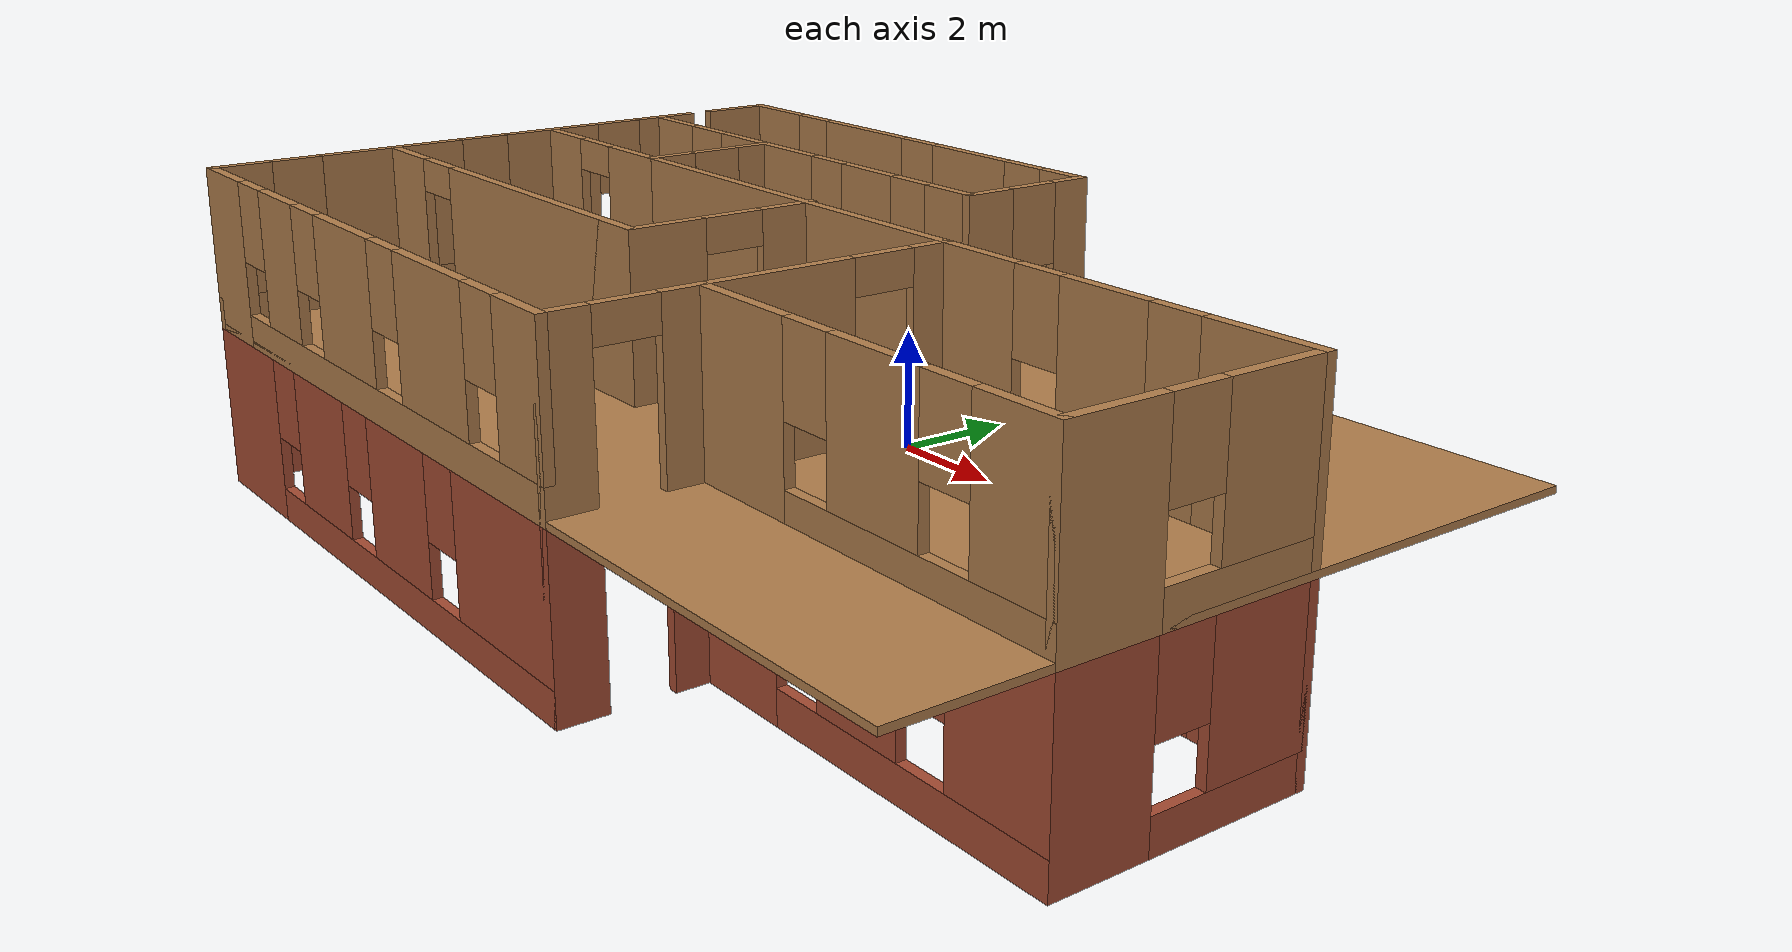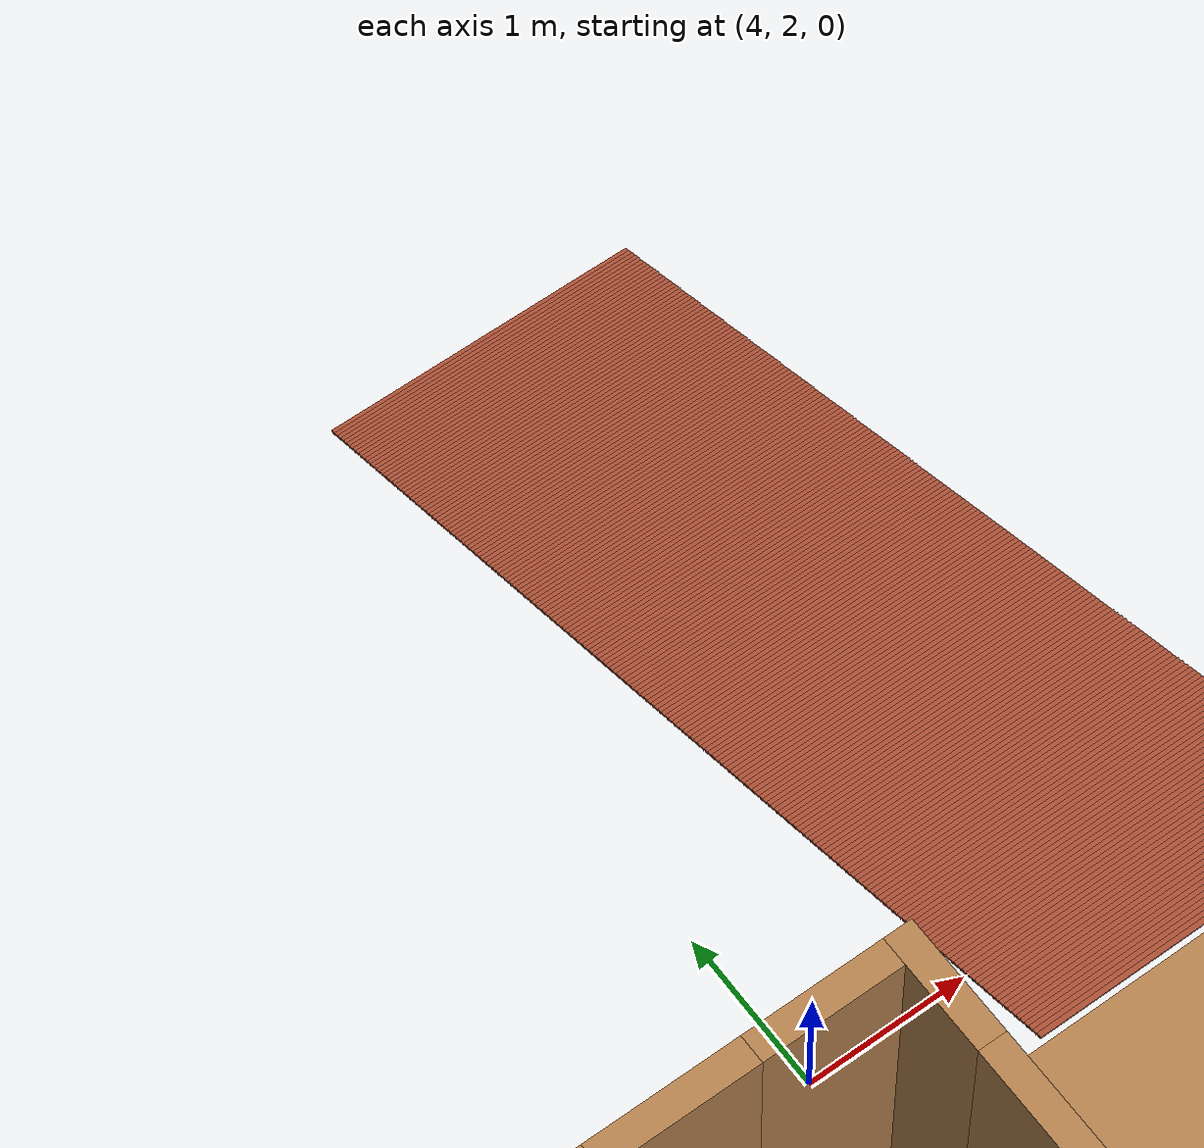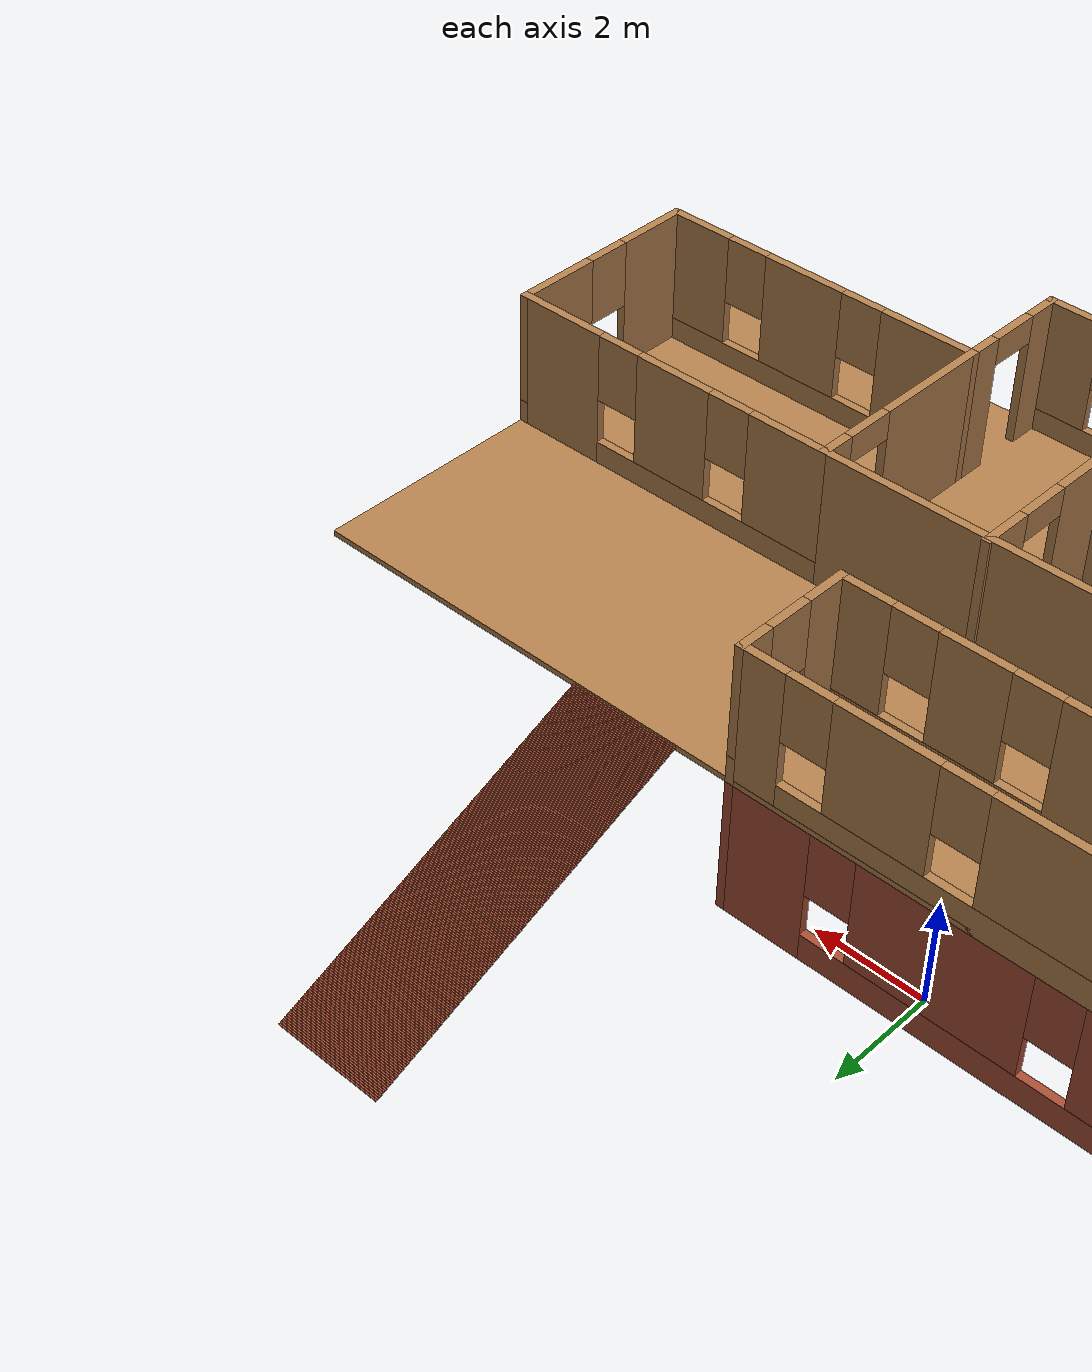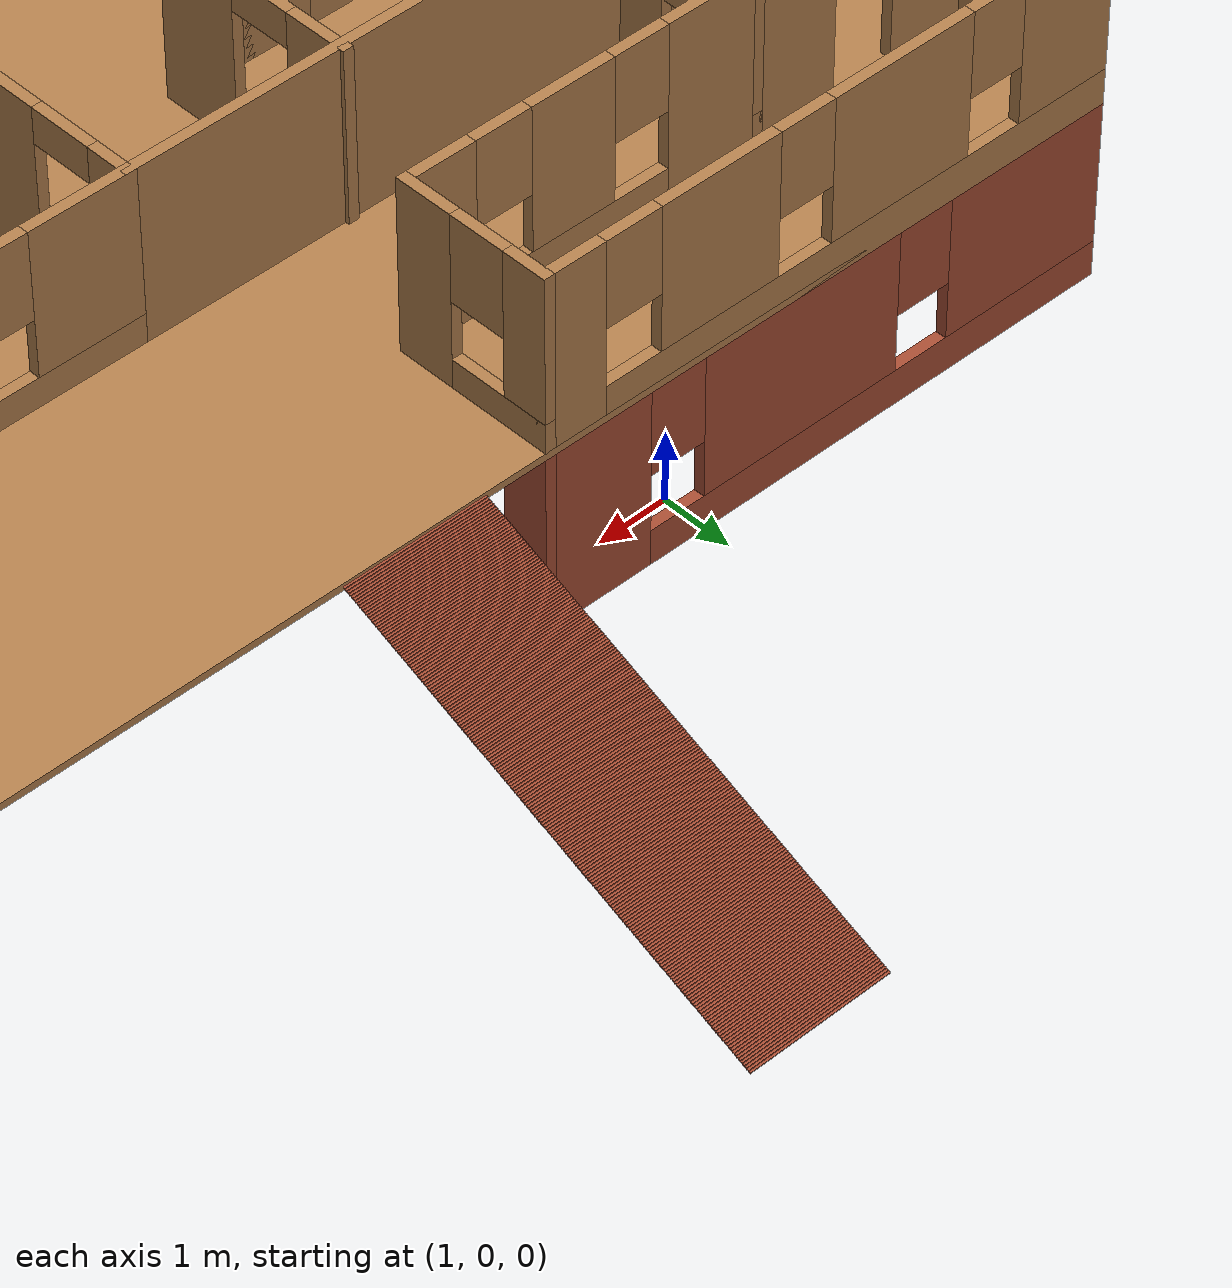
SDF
<?xml version='1.0'?>
<sdf version='1.7'>
  <model name='House'>
    <pose>3.17663 -1.38106 0 0 -0 0</pose>
    <link name='Floor_0'>
      <pose>0 -3.01679 2.5 0 -0 0</pose>
      <visual name='Floor_0_Visual_0'>
        <pose>0 0 0.05 0 -0 0</pose>
        <geometry>
          <box>
            <size>16.6 10.05 0.1</size>
          </box>
        </geometry>
        <material>
          <script>
            <uri>file://media/materials/scripts/gazebo.material</uri>
            <name>Gazebo/Wood</name>
          </script>
          <ambient>1 1 1 1</ambient>
        </material>
        <meta>
          <layer>1</layer>
        </meta>
      </visual>
      <collision name='Floor_0_Collision_0'>
        <geometry>
          <box>
            <size>16.6 10.05 0.1</size>
          </box>
        </geometry>
        <pose>0 0 0.05 0 -0 0</pose>
      </collision>
    </link>
    <link name='Stairs_4'>
      <visual name='Stairs_4_Visual_0'>
        <pose>2.07796 8.02679 0.0065 0 -0 0</pose>
        <geometry>
          <box>
            <size>2 0.03 0.013</size>
          </box>
        </geometry>
        <material>
          <script>
            <uri>file://media/materials/scripts/gazebo.material</uri>
            <name>Gazebo/Bricks</name>
          </script>
          <ambient>1 1 1 1</ambient>
        </material>
        <meta>
          <layer>1</layer>
        </meta>
      </visual>
      <collision name='Stairs_4_Collision_0'>
        <geometry>
          <box>
            <size>2 0.03 0.013</size>
          </box>
        </geometry>
        <pose>2.07796 8.02679 0.0065 0 -0 0</pose>
      </collision>
      <visual name='Stairs_4_Visual_1'>
        <pose>2.07796 7.99679 0.0195 0 -0 0</pose>
        <geometry>
          <box>
            <size>2 0.03 0.013</size>
          </box>
        </geometry>
        <material>
          <script>
            <uri>file://media/materials/scripts/gazebo.material</uri>
            <name>Gazebo/Bricks</name>
          </script>
          <ambient>1 1 1 1</ambient>
        </material>
        <meta>
          <layer>1</layer>
        </meta>
      </visual>
      <collision name='Stairs_4_Collision_1'>
        <geometry>
          <box>
            <size>2 0.03 0.013</size>
          </box>
        </geometry>
        <pose>2.07796 7.99679 0.0195 0 -0 0</pose>
      </collision>
      <visual name='Stairs_4_Visual_2'>
        <pose>2.07796 7.96679 0.0325 0 -0 0</pose>
        <geometry>
          <box>
            <size>2 0.03 0.013</size>
          </box>
        </geometry>
        <material>
          <script>
            <uri>file://media/materials/scripts/gazebo.material</uri>
            <name>Gazebo/Bricks</name>
          </script>
          <ambient>1 1 1 1</ambient>
        </material>
        <meta>
          <layer>1</layer>
        </meta>
      </visual>
      <collision name='Stairs_4_Collision_2'>
        <geometry>
          <box>
            <size>2 0.03 0.013</size>
          </box>
        </geometry>
        <pose>2.07796 7.96679 0.0325 0 -0 0</pose>
      </collision>
      <visual name='Stairs_4_Visual_3'>
        <pose>2.07796 7.93679 0.0455 0 -0 0</pose>
        <geometry>
          <box>
            <size>2 0.03 0.013</size>
          </box>
        </geometry>
        <material>
          <script>
            <uri>file://media/materials/scripts/gazebo.material</uri>
            <name>Gazebo/Bricks</name>
          </script>
          <ambient>1 1 1 1</ambient>
        </material>
        <meta>
          <layer>1</layer>
        </meta>
      </visual>
      <collision name='Stairs_4_Collision_3'>
        <geometry>
          <box>
            <size>2 0.03 0.013</size>
          </box>
        </geometry>
        <pose>2.07796 7.93679 0.0455 0 -0 0</pose>
      </collision>
      <visual name='Stairs_4_Visual_4'>
        <pose>2.07796 7.90679 0.0585 0 -0 0</pose>
        <geometry>
          <box>
            <size>2 0.03 0.013</size>
          </box>
        </geometry>
        <material>
          <script>
            <uri>file://media/materials/scripts/gazebo.material</uri>
            <name>Gazebo/Bricks</name>
          </script>
          <ambient>1 1 1 1</ambient>
        </material>
        <meta>
          <layer>1</layer>
        </meta>
      </visual>
      <collision name='Stairs_4_Collision_4'>
        <geometry>
          <box>
            <size>2 0.03 0.013</size>
          </box>
        </geometry>
        <pose>2.07796 7.90679 0.0585 0 -0 0</pose>
      </collision>
      <visual name='Stairs_4_Visual_5'>
        <pose>2.07796 7.87679 0.0715 0 -0 0</pose>
        <geometry>
          <box>
            <size>2 0.03 0.013</size>
          </box>
        </geometry>
        <material>
          <script>
            <uri>file://media/materials/scripts/gazebo.material</uri>
            <name>Gazebo/Bricks</name>
          </script>
          <ambient>1 1 1 1</ambient>
        </material>
        <meta>
          <layer>1</layer>
        </meta>
      </visual>
      <collision name='Stairs_4_Collision_5'>
        <geometry>
          <box>
            <size>2 0.03 0.013</size>
          </box>
        </geometry>
        <pose>2.07796 7.87679 0.0715 0 -0 0</pose>
      </collision>
      <visual name='Stairs_4_Visual_6'>
        <pose>2.07796 7.84679 0.0845 0 -0 0</pose>
        <geometry>
          <box>
            <size>2 0.03 0.013</size>
          </box>
        </geometry>
        <material>
          <script>
            <uri>file://media/materials/scripts/gazebo.material</uri>
            <name>Gazebo/Bricks</name>
          </script>
          <ambient>1 1 1 1</ambient>
        </material>
        <meta>
          <layer>1</layer>
        </meta>
      </visual>
      <collision name='Stairs_4_Collision_6'>
        <geometry>
          <box>
            <size>2 0.03 0.013</size>
          </box>
        </geometry>
        <pose>2.07796 7.84679 0.0845 0 -0 0</pose>
      </collision>
      <visual name='Stairs_4_Visual_7'>
        <pose>2.07796 7.81679 0.0975 0 -0 0</pose>
        <geometry>
          <box>
            <size>2 0.03 0.013</size>
          </box>
        </geometry>
        <material>
          <script>
            <uri>file://media/materials/scripts/gazebo.material</uri>
            <name>Gazebo/Bricks</name>
          </script>
          <ambient>1 1 1 1</ambient>
        </material>
        <meta>
          <layer>1</layer>
        </meta>
      </visual>
      <collision name='Stairs_4_Collision_7'>
        <geometry>
          <box>
            <size>2 0.03 0.013</size>
          </box>
        </geometry>
        <pose>2.07796 7.81679 0.0975 0 -0 0</pose>
      </collision>
      <visual name='Stairs_4_Visual_8'>
        <pose>2.07796 7.78679 0.1105 0 -0 0</pose>
        <geometry>
          <box>
            <size>2 0.03 0.013</size>
          </box>
        </geometry>
        <material>
          <script>
            <uri>file://media/materials/scripts/gazebo.material</uri>
            <name>Gazebo/Bricks</name>
          </script>
          <ambient>1 1 1 1</ambient>
        </material>
        <meta>
          <layer>1</layer>
        </meta>
      </visual>
      <collision name='Stairs_4_Collision_8'>
        <geometry>
          <box>
            <size>2 0.03 0.013</size>
          </box>
        </geometry>
        <pose>2.07796 7.78679 0.1105 0 -0 0</pose>
      </collision>
      <visual name='Stairs_4_Visual_9'>
        <pose>2.07796 7.75679 0.1235 0 -0 0</pose>
        <geometry>
          <box>
            <size>2 0.03 0.013</size>
          </box>
        </geometry>
        <material>
          <script>
            <uri>file://media/materials/scripts/gazebo.material</uri>
            <name>Gazebo/Bricks</name>
          </script>
          <ambient>1 1 1 1</ambient>
        </material>
        <meta>
          <layer>1</layer>
        </meta>
      </visual>
      <collision name='Stairs_4_Collision_9'>
        <geometry>
          <box>
            <size>2 0.03 0.013</size>
          </box>
        </geometry>
        <pose>2.07796 7.75679 0.1235 0 -0 0</pose>
      </collision>
      <visual name='Stairs_4_Visual_10'>
        <pose>2.07796 7.72679 0.1365 0 -0 0</pose>
        <geometry>
          <box>
            <size>2 0.03 0.013</size>
          </box>
        </geometry>
        <material>
          <script>
            <uri>file://media/materials/scripts/gazebo.material</uri>
            <name>Gazebo/Bricks</name>
          </script>
          <ambient>1 1 1 1</ambient>
        </material>
        <meta>
          <layer>1</layer>
        </meta>
      </visual>
      <collision name='Stairs_4_Collision_10'>
        <geometry>
          <box>
            <size>2 0.03 0.013</size>
          </box>
        </geometry>
        <pose>2.07796 7.72679 0.1365 0 -0 0</pose>
      </collision>
      <visual name='Stairs_4_Visual_11'>
        <pose>2.07796 7.69679 0.1495 0 -0 0</pose>
        <geometry>
          <box>
            <size>2 0.03 0.013</size>
          </box>
        </geometry>
        <material>
          <script>
            <uri>file://media/materials/scripts/gazebo.material</uri>
            <name>Gazebo/Bricks</name>
          </script>
          <ambient>1 1 1 1</ambient>
        </material>
        <meta>
          <layer>1</layer>
        </meta>
      </visual>
      <collision name='Stairs_4_Collision_11'>
        <geometry>
          <box>
            <size>2 0.03 0.013</size>
          </box>
        </geometry>
        <pose>2.07796 7.69679 0.1495 0 -0 0</pose>
      </collision>
      <visual name='Stairs_4_Visual_12'>
        <pose>2.07796 7.66679 0.1625 0 -0 0</pose>
        <geometry>
          <box>
            <size>2 0.03 0.013</size>
          </box>
        </geometry>
        <material>
          <script>
            <uri>file://media/materials/scripts/gazebo.material</uri>
            <name>Gazebo/Bricks</name>
          </script>
          <ambient>1 1 1 1</ambient>
        </material>
        <meta>
          <layer>1</layer>
        </meta>
      </visual>
      <collision name='Stairs_4_Collision_12'>
        <geometry>
          <box>
            <size>2 0.03 0.013</size>
          </box>
        </geometry>
        <pose>2.07796 7.66679 0.1625 0 -0 0</pose>
      </collision>
      <visual name='Stairs_4_Visual_13'>
        <pose>2.07796 7.63679 0.1755 0 -0 0</pose>
        <geometry>
          <box>
            <size>2 0.03 0.013</size>
          </box>
        </geometry>
        <material>
          <script>
            <uri>file://media/materials/scripts/gazebo.material</uri>
            <name>Gazebo/Bricks</name>
          </script>
          <ambient>1 1 1 1</ambient>
        </material>
        <meta>
          <layer>1</layer>
        </meta>
      </visual>
      <collision name='Stairs_4_Collision_13'>
        <geometry>
          <box>
            <size>2 0.03 0.013</size>
          </box>
        </geometry>
        <pose>2.07796 7.63679 0.1755 0 -0 0</pose>
      </collision>
      <visual name='Stairs_4_Visual_14'>
        <pose>2.07796 7.60679 0.1885 0 -0 0</pose>
        <geometry>
          <box>
            <size>2 0.03 0.013</size>
          </box>
        </geometry>
        <material>
          <script>
            <uri>file://media/materials/scripts/gazebo.material</uri>
            <name>Gazebo/Bricks</name>
          </script>
          <ambient>1 1 1 1</ambient>
        </material>
        <meta>
          <layer>1</layer>
        </meta>
      </visual>
      <collision name='Stairs_4_Collision_14'>
        <geometry>
          <box>
            <size>2 0.03 0.013</size>
          </box>
        </geometry>
        <pose>2.07796 7.60679 0.1885 0 -0 0</pose>
      </collision>
      <visual name='Stairs_4_Visual_15'>
        <pose>2.07796 7.57679 0.2015 0 -0 0</pose>
        <geometry>
          <box>
            <size>2 0.03 0.013</size>
          </box>
        </geometry>
        <material>
          <script>
            <uri>file://media/materials/scripts/gazebo.material</uri>
            <name>Gazebo/Bricks</name>
          </script>
          <ambient>1 1 1 1</ambient>
        </material>
        <meta>
          <layer>1</layer>
        </meta>
      </visual>
      <collision name='Stairs_4_Collision_15'>
        <geometry>
          <box>
            <size>2 0.03 0.013</size>
          </box>
        </geometry>
        <pose>2.07796 7.57679 0.2015 0 -0 0</pose>
      </collision>
      <visual name='Stairs_4_Visual_16'>
        <pose>2.07796 7.54679 0.2145 0 -0 0</pose>
        <geometry>
          <box>
            <size>2 0.03 0.013</size>
          </box>
        </geometry>
        <material>
          <script>
            <uri>file://media/materials/scripts/gazebo.material</uri>
            <name>Gazebo/Bricks</name>
          </script>
          <ambient>1 1 1 1</ambient>
        </material>
        <meta>
          <layer>1</layer>
        </meta>
      </visual>
      <collision name='Stairs_4_Collision_16'>
        <geometry>
          <box>
            <size>2 0.03 0.013</size>
          </box>
        </geometry>
        <pose>2.07796 7.54679 0.2145 0 -0 0</pose>
      </collision>
      <visual name='Stairs_4_Visual_17'>
        <pose>2.07796 7.51679 0.2275 0 -0 0</pose>
        <geometry>
          <box>
            <size>2 0.03 0.013</size>
          </box>
        </geometry>
        <material>
          <script>
            <uri>file://media/materials/scripts/gazebo.material</uri>
            <name>Gazebo/Bricks</name>
          </script>
          <ambient>1 1 1 1</ambient>
        </material>
        <meta>
          <layer>1</layer>
        </meta>
      </visual>
      <collision name='Stairs_4_Collision_17'>
        <geometry>
          <box>
            <size>2 0.03 0.013</size>
          </box>
        </geometry>
        <pose>2.07796 7.51679 0.2275 0 -0 0</pose>
      </collision>
      <visual name='Stairs_4_Visual_18'>
        <pose>2.07796 7.48679 0.2405 0 -0 0</pose>
        <geometry>
          <box>
            <size>2 0.03 0.013</size>
          </box>
        </geometry>
        <material>
          <script>
            <uri>file://media/materials/scripts/gazebo.material</uri>
            <name>Gazebo/Bricks</name>
          </script>
          <ambient>1 1 1 1</ambient>
        </material>
        <meta>
          <layer>1</layer>
        </meta>
      </visual>
      <collision name='Stairs_4_Collision_18'>
        <geometry>
          <box>
            <size>2 0.03 0.013</size>
          </box>
        </geometry>
        <pose>2.07796 7.48679 0.2405 0 -0 0</pose>
      </collision>
      <visual name='Stairs_4_Visual_19'>
        <pose>2.07796 7.45679 0.2535 0 -0 0</pose>
        <geometry>
          <box>
            <size>2 0.03 0.013</size>
          </box>
        </geometry>
        <material>
          <script>
            <uri>file://media/materials/scripts/gazebo.material</uri>
            <name>Gazebo/Bricks</name>
          </script>
          <ambient>1 1 1 1</ambient>
        </material>
        <meta>
          <layer>1</layer>
        </meta>
      </visual>
      <collision name='Stairs_4_Collision_19'>
        <geometry>
          <box>
            <size>2 0.03 0.013</size>
          </box>
        </geometry>
        <pose>2.07796 7.45679 0.2535 0 -0 0</pose>
      </collision>
      <visual name='Stairs_4_Visual_20'>
        <pose>2.07796 7.42679 0.2665 0 -0 0</pose>
        <geometry>
          <box>
            <size>2 0.03 0.013</size>
          </box>
        </geometry>
        <material>
          <script>
            <uri>file://media/materials/scripts/gazebo.material</uri>
            <name>Gazebo/Bricks</name>
          </script>
          <ambient>1 1 1 1</ambient>
        </material>
        <meta>
          <layer>1</layer>
        </meta>
      </visual>
      <collision name='Stairs_4_Collision_20'>
        <geometry>
          <box>
            <size>2 0.03 0.013</size>
          </box>
        </geometry>
        <pose>2.07796 7.42679 0.2665 0 -0 0</pose>
      </collision>
      <visual name='Stairs_4_Visual_21'>
        <pose>2.07796 7.39679 0.2795 0 -0 0</pose>
        <geometry>
          <box>
            <size>2 0.03 0.013</size>
          </box>
        </geometry>
        <material>
          <script>
            <uri>file://media/materials/scripts/gazebo.material</uri>
            <name>Gazebo/Bricks</name>
          </script>
          <ambient>1 1 1 1</ambient>
        </material>
        <meta>
          <layer>1</layer>
        </meta>
      </visual>
      <collision name='Stairs_4_Collision_21'>
        <geometry>
          <box>
            <size>2 0.03 0.013</size>
          </box>
        </geometry>
        <pose>2.07796 7.39679 0.2795 0 -0 0</pose>
      </collision>
      <visual name='Stairs_4_Visual_22'>
        <pose>2.07796 7.36679 0.2925 0 -0 0</pose>
        <geometry>
          <box>
            <size>2 0.03 0.013</size>
          </box>
        </geometry>
        <material>
          <script>
            <uri>file://media/materials/scripts/gazebo.material</uri>
            <name>Gazebo/Bricks</name>
          </script>
          <ambient>1 1 1 1</ambient>
        </material>
        <meta>
          <layer>1</layer>
        </meta>
      </visual>
      <collision name='Stairs_4_Collision_22'>
        <geometry>
          <box>
            <size>2 0.03 0.013</size>
          </box>
        </geometry>
        <pose>2.07796 7.36679 0.2925 0 -0 0</pose>
      </collision>
      <visual name='Stairs_4_Visual_23'>
        <pose>2.07796 7.33679 0.3055 0 -0 0</pose>
        <geometry>
          <box>
            <size>2 0.03 0.013</size>
          </box>
        </geometry>
        <material>
          <script>
            <uri>file://media/materials/scripts/gazebo.material</uri>
            <name>Gazebo/Bricks</name>
          </script>
          <ambient>1 1 1 1</ambient>
        </material>
        <meta>
          <layer>1</layer>
        </meta>
      </visual>
      <collision name='Stairs_4_Collision_23'>
        <geometry>
          <box>
            <size>2 0.03 0.013</size>
          </box>
        </geometry>
        <pose>2.07796 7.33679 0.3055 0 -0 0</pose>
      </collision>
      <visual name='Stairs_4_Visual_24'>
        <pose>2.07796 7.30679 0.3185 0 -0 0</pose>
        <geometry>
          <box>
            <size>2 0.03 0.013</size>
          </box>
        </geometry>
        <material>
          <script>
            <uri>file://media/materials/scripts/gazebo.material</uri>
            <name>Gazebo/Bricks</name>
          </script>
          <ambient>1 1 1 1</ambient>
        </material>
        <meta>
          <layer>1</layer>
        </meta>
      </visual>
      <collision name='Stairs_4_Collision_24'>
        <geometry>
          <box>
            <size>2 0.03 0.013</size>
          </box>
        </geometry>
        <pose>2.07796 7.30679 0.3185 0 -0 0</pose>
      </collision>
      <visual name='Stairs_4_Visual_25'>
        <pose>2.07796 7.27679 0.3315 0 -0 0</pose>
        <geometry>
          <box>
            <size>2 0.03 0.013</size>
          </box>
        </geometry>
        <material>
          <script>
            <uri>file://media/materials/scripts/gazebo.material</uri>
            <name>Gazebo/Bricks</name>
          </script>
          <ambient>1 1 1 1</ambient>
        </material>
        <meta>
          <layer>1</layer>
        </meta>
      </visual>
      <collision name='Stairs_4_Collision_25'>
        <geometry>
          <box>
            <size>2 0.03 0.013</size>
          </box>
        </geometry>
        <pose>2.07796 7.27679 0.3315 0 -0 0</pose>
      </collision>
      <visual name='Stairs_4_Visual_26'>
        <pose>2.07796 7.24679 0.3445 0 -0 0</pose>
        <geometry>
          <box>
            <size>2 0.03 0.013</size>
          </box>
        </geometry>
        <material>
          <script>
            <uri>file://media/materials/scripts/gazebo.material</uri>
            <name>Gazebo/Bricks</name>
          </script>
          <ambient>1 1 1 1</ambient>
        </material>
        <meta>
          <layer>1</layer>
        </meta>
      </visual>
      <collision name='Stairs_4_Collision_26'>
        <geometry>
          <box>
            <size>2 0.03 0.013</size>
          </box>
        </geometry>
        <pose>2.07796 7.24679 0.3445 0 -0 0</pose>
      </collision>
      <visual name='Stairs_4_Visual_27'>
        <pose>2.07796 7.21679 0.3575 0 -0 0</pose>
        <geometry>
          <box>
            <size>2 0.03 0.013</size>
          </box>
        </geometry>
        <material>
          <script>
            <uri>file://media/materials/scripts/gazebo.material</uri>
            <name>Gazebo/Bricks</name>
          </script>
          <ambient>1 1 1 1</ambient>
        </material>
        <meta>
          <layer>1</layer>
        </meta>
      </visual>
      <collision name='Stairs_4_Collision_27'>
        <geometry>
          <box>
            <size>2 0.03 0.013</size>
          </box>
        </geometry>
        <pose>2.07796 7.21679 0.3575 0 -0 0</pose>
      </collision>
      <visual name='Stairs_4_Visual_28'>
        <pose>2.07796 7.18679 0.3705 0 -0 0</pose>
        <geometry>
          <box>
            <size>2 0.03 0.013</size>
          </box>
        </geometry>
        <material>
          <script>
            <uri>file://media/materials/scripts/gazebo.material</uri>
            <name>Gazebo/Bricks</name>
          </script>
          <ambient>1 1 1 1</ambient>
        </material>
        <meta>
          <layer>1</layer>
        </meta>
      </visual>
      <collision name='Stairs_4_Collision_28'>
        <geometry>
          <box>
            <size>2 0.03 0.013</size>
          </box>
        </geometry>
        <pose>2.07796 7.18679 0.3705 0 -0 0</pose>
      </collision>
      <visual name='Stairs_4_Visual_29'>
        <pose>2.07796 7.15679 0.3835 0 -0 0</pose>
        <geometry>
          <box>
            <size>2 0.03 0.013</size>
          </box>
        </geometry>
        <material>
          <script>
            <uri>file://media/materials/scripts/gazebo.material</uri>
            <name>Gazebo/Bricks</name>
          </script>
          <ambient>1 1 1 1</ambient>
        </material>
        <meta>
          <layer>1</layer>
        </meta>
      </visual>
      <collision name='Stairs_4_Collision_29'>
        <geometry>
          <box>
            <size>2 0.03 0.013</size>
          </box>
        </geometry>
        <pose>2.07796 7.15679 0.3835 0 -0 0</pose>
      </collision>
      <visual name='Stairs_4_Visual_30'>
        <pose>2.07796 7.12679 0.3965 0 -0 0</pose>
        <geometry>
          <box>
            <size>2 0.03 0.013</size>
          </box>
        </geometry>
        <material>
          <script>
            <uri>file://media/materials/scripts/gazebo.material</uri>
            <name>Gazebo/Bricks</name>
          </script>
          <ambient>1 1 1 1</ambient>
        </material>
        <meta>
          <layer>1</layer>
        </meta>
      </visual>
      <collision name='Stairs_4_Collision_30'>
        <geometry>
          <box>
            <size>2 0.03 0.013</size>
          </box>
        </geometry>
        <pose>2.07796 7.12679 0.3965 0 -0 0</pose>
      </collision>
      <visual name='Stairs_4_Visual_31'>
        <pose>2.07796 7.09679 0.4095 0 -0 0</pose>
        <geometry>
          <box>
            <size>2 0.03 0.013</size>
          </box>
        </geometry>
        <material>
          <script>
            <uri>file://media/materials/scripts/gazebo.material</uri>
            <name>Gazebo/Bricks</name>
          </script>
          <ambient>1 1 1 1</ambient>
        </material>
        <meta>
          <layer>1</layer>
        </meta>
      </visual>
      <collision name='Stairs_4_Collision_31'>
        <geometry>
          <box>
            <size>2 0.03 0.013</size>
          </box>
        </geometry>
        <pose>2.07796 7.09679 0.4095 0 -0 0</pose>
      </collision>
      <visual name='Stairs_4_Visual_32'>
        <pose>2.07796 7.06679 0.4225 0 -0 0</pose>
        <geometry>
          <box>
            <size>2 0.03 0.013</size>
          </box>
        </geometry>
        <material>
          <script>
            <uri>file://media/materials/scripts/gazebo.material</uri>
            <name>Gazebo/Bricks</name>
          </script>
          <ambient>1 1 1 1</ambient>
        </material>
        <meta>
          <layer>1</layer>
        </meta>
      </visual>
      <collision name='Stairs_4_Collision_32'>
        <geometry>
          <box>
            <size>2 0.03 0.013</size>
          </box>
        </geometry>
        <pose>2.07796 7.06679 0.4225 0 -0 0</pose>
      </collision>
      <visual name='Stairs_4_Visual_33'>
        <pose>2.07796 7.03679 0.4355 0 -0 0</pose>
        <geometry>
          <box>
            <size>2 0.03 0.013</size>
          </box>
        </geometry>
        <material>
          <script>
            <uri>file://media/materials/scripts/gazebo.material</uri>
            <name>Gazebo/Bricks</name>
          </script>
          <ambient>1 1 1 1</ambient>
        </material>
        <meta>
          <layer>1</layer>
        </meta>
      </visual>
      <collision name='Stairs_4_Collision_33'>
        <geometry>
          <box>
            <size>2 0.03 0.013</size>
          </box>
        </geometry>
        <pose>2.07796 7.03679 0.4355 0 -0 0</pose>
      </collision>
      <visual name='Stairs_4_Visual_34'>
        <pose>2.07796 7.00679 0.4485 0 -0 0</pose>
        <geometry>
          <box>
            <size>2 0.03 0.013</size>
          </box>
        </geometry>
        <material>
          <script>
            <uri>file://media/materials/scripts/gazebo.material</uri>
            <name>Gazebo/Bricks</name>
          </script>
          <ambient>1 1 1 1</ambient>
        </material>
        <meta>
          <layer>1</layer>
        </meta>
      </visual>
      <collision name='Stairs_4_Collision_34'>
        <geometry>
          <box>
            <size>2 0.03 0.013</size>
          </box>
        </geometry>
        <pose>2.07796 7.00679 0.4485 0 -0 0</pose>
      </collision>
      <visual name='Stairs_4_Visual_35'>
        <pose>2.07796 6.97679 0.4615 0 -0 0</pose>
        <geometry>
          <box>
            <size>2 0.03 0.013</size>
          </box>
        </geometry>
        <material>
          <script>
            <uri>file://media/materials/scripts/gazebo.material</uri>
            <name>Gazebo/Bricks</name>
          </script>
          <ambient>1 1 1 1</ambient>
        </material>
        <meta>
          <layer>1</layer>
        </meta>
      </visual>
      <collision name='Stairs_4_Collision_35'>
        <geometry>
          <box>
            <size>2 0.03 0.013</size>
          </box>
        </geometry>
        <pose>2.07796 6.97679 0.4615 0 -0 0</pose>
      </collision>
      <visual name='Stairs_4_Visual_36'>
        <pose>2.07796 6.94679 0.4745 0 -0 0</pose>
        <geometry>
          <box>
            <size>2 0.03 0.013</size>
          </box>
        </geometry>
        <material>
          <script>
            <uri>file://media/materials/scripts/gazebo.material</uri>
            <name>Gazebo/Bricks</name>
          </script>
          <ambient>1 1 1 1</ambient>
        </material>
        <meta>
          <layer>1</layer>
        </meta>
      </visual>
      <collision name='Stairs_4_Collision_36'>
        <geometry>
          <box>
            <size>2 0.03 0.013</size>
          </box>
        </geometry>
        <pose>2.07796 6.94679 0.4745 0 -0 0</pose>
      </collision>
      <visual name='Stairs_4_Visual_37'>
        <pose>2.07796 6.91679 0.4875 0 -0 0</pose>
        <geometry>
          <box>
            <size>2 0.03 0.013</size>
          </box>
        </geometry>
        <material>
          <script>
            <uri>file://media/materials/scripts/gazebo.material</uri>
            <name>Gazebo/Bricks</name>
          </script>
          <ambient>1 1 1 1</ambient>
        </material>
        <meta>
          <layer>1</layer>
        </meta>
      </visual>
      <collision name='Stairs_4_Collision_37'>
        <geometry>
          <box>
            <size>2 0.03 0.013</size>
          </box>
        </geometry>
        <pose>2.07796 6.91679 0.4875 0 -0 0</pose>
      </collision>
      <visual name='Stairs_4_Visual_38'>
        <pose>2.07796 6.88679 0.5005 0 -0 0</pose>
        <geometry>
          <box>
            <size>2 0.03 0.013</size>
          </box>
        </geometry>
        <material>
          <script>
            <uri>file://media/materials/scripts/gazebo.material</uri>
            <name>Gazebo/Bricks</name>
          </script>
          <ambient>1 1 1 1</ambient>
        </material>
        <meta>
          <layer>1</layer>
        </meta>
      </visual>
      <collision name='Stairs_4_Collision_38'>
        <geometry>
          <box>
            <size>2 0.03 0.013</size>
          </box>
        </geometry>
        <pose>2.07796 6.88679 0.5005 0 -0 0</pose>
      </collision>
      <visual name='Stairs_4_Visual_39'>
        <pose>2.07796 6.85679 0.5135 0 -0 0</pose>
        <geometry>
          <box>
            <size>2 0.03 0.013</size>
          </box>
        </geometry>
        <material>
          <script>
            <uri>file://media/materials/scripts/gazebo.material</uri>
            <name>Gazebo/Bricks</name>
          </script>
          <ambient>1 1 1 1</ambient>
        </material>
        <meta>
          <layer>1</layer>
        </meta>
      </visual>
      <collision name='Stairs_4_Collision_39'>
        <geometry>
          <box>
            <size>2 0.03 0.013</size>
          </box>
        </geometry>
        <pose>2.07796 6.85679 0.5135 0 -0 0</pose>
      </collision>
      <visual name='Stairs_4_Visual_40'>
        <pose>2.07796 6.82679 0.5265 0 -0 0</pose>
        <geometry>
          <box>
            <size>2 0.03 0.013</size>
          </box>
        </geometry>
        <material>
          <script>
            <uri>file://media/materials/scripts/gazebo.material</uri>
            <name>Gazebo/Bricks</name>
          </script>
          <ambient>1 1 1 1</ambient>
        </material>
        <meta>
          <layer>1</layer>
        </meta>
      </visual>
      <collision name='Stairs_4_Collision_40'>
        <geometry>
          <box>
            <size>2 0.03 0.013</size>
          </box>
        </geometry>
        <pose>2.07796 6.82679 0.5265 0 -0 0</pose>
      </collision>
      <visual name='Stairs_4_Visual_41'>
        <pose>2.07796 6.79679 0.5395 0 -0 0</pose>
        <geometry>
          <box>
            <size>2 0.03 0.013</size>
          </box>
        </geometry>
        <material>
          <script>
            <uri>file://media/materials/scripts/gazebo.material</uri>
            <name>Gazebo/Bricks</name>
          </script>
          <ambient>1 1 1 1</ambient>
        </material>
        <meta>
          <layer>1</layer>
        </meta>
      </visual>
      <collision name='Stairs_4_Collision_41'>
        <geometry>
          <box>
            <size>2 0.03 0.013</size>
          </box>
        </geometry>
        <pose>2.07796 6.79679 0.5395 0 -0 0</pose>
      </collision>
      <visual name='Stairs_4_Visual_42'>
        <pose>2.07796 6.76679 0.5525 0 -0 0</pose>
        <geometry>
          <box>
            <size>2 0.03 0.013</size>
          </box>
        </geometry>
        <material>
          <script>
            <uri>file://media/materials/scripts/gazebo.material</uri>
            <name>Gazebo/Bricks</name>
          </script>
          <ambient>1 1 1 1</ambient>
        </material>
        <meta>
          <layer>1</layer>
        </meta>
      </visual>
      <collision name='Stairs_4_Collision_42'>
        <geometry>
          <box>
            <size>2 0.03 0.013</size>
          </box>
        </geometry>
        <pose>2.07796 6.76679 0.5525 0 -0 0</pose>
      </collision>
      <visual name='Stairs_4_Visual_43'>
        <pose>2.07796 6.73679 0.5655 0 -0 0</pose>
        <geometry>
          <box>
            <size>2 0.03 0.013</size>
          </box>
        </geometry>
        <material>
          <script>
            <uri>file://media/materials/scripts/gazebo.material</uri>
            <name>Gazebo/Bricks</name>
          </script>
          <ambient>1 1 1 1</ambient>
        </material>
        <meta>
          <layer>1</layer>
        </meta>
      </visual>
      <collision name='Stairs_4_Collision_43'>
        <geometry>
          <box>
            <size>2 0.03 0.013</size>
          </box>
        </geometry>
        <pose>2.07796 6.73679 0.5655 0 -0 0</pose>
      </collision>
      <visual name='Stairs_4_Visual_44'>
        <pose>2.07796 6.70679 0.5785 0 -0 0</pose>
        <geometry>
          <box>
            <size>2 0.03 0.013</size>
          </box>
        </geometry>
        <material>
          <script>
            <uri>file://media/materials/scripts/gazebo.material</uri>
            <name>Gazebo/Bricks</name>
          </script>
          <ambient>1 1 1 1</ambient>
        </material>
        <meta>
          <layer>1</layer>
        </meta>
      </visual>
      <collision name='Stairs_4_Collision_44'>
        <geometry>
          <box>
            <size>2 0.03 0.013</size>
          </box>
        </geometry>
        <pose>2.07796 6.70679 0.5785 0 -0 0</pose>
      </collision>
      <visual name='Stairs_4_Visual_45'>
        <pose>2.07796 6.67679 0.5915 0 -0 0</pose>
        <geometry>
          <box>
            <size>2 0.03 0.013</size>
          </box>
        </geometry>
        <material>
          <script>
            <uri>file://media/materials/scripts/gazebo.material</uri>
            <name>Gazebo/Bricks</name>
          </script>
          <ambient>1 1 1 1</ambient>
        </material>
        <meta>
          <layer>1</layer>
        </meta>
      </visual>
      <collision name='Stairs_4_Collision_45'>
        <geometry>
          <box>
            <size>2 0.03 0.013</size>
          </box>
        </geometry>
        <pose>2.07796 6.67679 0.5915 0 -0 0</pose>
      </collision>
      <visual name='Stairs_4_Visual_46'>
        <pose>2.07796 6.64679 0.6045 0 -0 0</pose>
        <geometry>
          <box>
            <size>2 0.03 0.013</size>
          </box>
        </geometry>
        <material>
          <script>
            <uri>file://media/materials/scripts/gazebo.material</uri>
            <name>Gazebo/Bricks</name>
          </script>
          <ambient>1 1 1 1</ambient>
        </material>
        <meta>
          <layer>1</layer>
        </meta>
      </visual>
      <collision name='Stairs_4_Collision_46'>
        <geometry>
          <box>
            <size>2 0.03 0.013</size>
          </box>
        </geometry>
        <pose>2.07796 6.64679 0.6045 0 -0 0</pose>
      </collision>
      <visual name='Stairs_4_Visual_47'>
        <pose>2.07796 6.61679 0.6175 0 -0 0</pose>
        <geometry>
          <box>
            <size>2 0.03 0.013</size>
          </box>
        </geometry>
        <material>
          <script>
            <uri>file://media/materials/scripts/gazebo.material</uri>
            <name>Gazebo/Bricks</name>
          </script>
          <ambient>1 1 1 1</ambient>
        </material>
        <meta>
          <layer>1</layer>
        </meta>
      </visual>
      <collision name='Stairs_4_Collision_47'>
        <geometry>
          <box>
            <size>2 0.03 0.013</size>
          </box>
        </geometry>
        <pose>2.07796 6.61679 0.6175 0 -0 0</pose>
      </collision>
      <visual name='Stairs_4_Visual_48'>
        <pose>2.07796 6.58679 0.6305 0 -0 0</pose>
        <geometry>
          <box>
            <size>2 0.03 0.013</size>
          </box>
        </geometry>
        <material>
          <script>
            <uri>file://media/materials/scripts/gazebo.material</uri>
            <name>Gazebo/Bricks</name>
          </script>
          <ambient>1 1 1 1</ambient>
        </material>
        <meta>
          <layer>1</layer>
        </meta>
      </visual>
      <collision name='Stairs_4_Collision_48'>
        <geometry>
          <box>
            <size>2 0.03 0.013</size>
          </box>
        </geometry>
        <pose>2.07796 6.58679 0.6305 0 -0 0</pose>
      </collision>
      <visual name='Stairs_4_Visual_49'>
        <pose>2.07796 6.55679 0.6435 0 -0 0</pose>
        <geometry>
          <box>
            <size>2 0.03 0.013</size>
          </box>
        </geometry>
        <material>
          <script>
            <uri>file://media/materials/scripts/gazebo.material</uri>
            <name>Gazebo/Bricks</name>
          </script>
          <ambient>1 1 1 1</ambient>
        </material>
        <meta>
          <layer>1</layer>
        </meta>
      </visual>
      <collision name='Stairs_4_Collision_49'>
        <geometry>
          <box>
            <size>2 0.03 0.013</size>
          </box>
        </geometry>
        <pose>2.07796 6.55679 0.6435 0 -0 0</pose>
      </collision>
      <visual name='Stairs_4_Visual_50'>
        <pose>2.07796 6.52679 0.6565 0 -0 0</pose>
        <geometry>
          <box>
            <size>2 0.03 0.013</size>
          </box>
        </geometry>
        <material>
          <script>
            <uri>file://media/materials/scripts/gazebo.material</uri>
            <name>Gazebo/Bricks</name>
          </script>
          <ambient>1 1 1 1</ambient>
        </material>
        <meta>
          <layer>1</layer>
        </meta>
      </visual>
      <collision name='Stairs_4_Collision_50'>
        <geometry>
          <box>
            <size>2 0.03 0.013</size>
          </box>
        </geometry>
        <pose>2.07796 6.52679 0.6565 0 -0 0</pose>
      </collision>
      <visual name='Stairs_4_Visual_51'>
        <pose>2.07796 6.49679 0.6695 0 -0 0</pose>
        <geometry>
          <box>
            <size>2 0.03 0.013</size>
          </box>
        </geometry>
        <material>
          <script>
            <uri>file://media/materials/scripts/gazebo.material</uri>
            <name>Gazebo/Bricks</name>
          </script>
          <ambient>1 1 1 1</ambient>
        </material>
        <meta>
          <layer>1</layer>
        </meta>
      </visual>
      <collision name='Stairs_4_Collision_51'>
        <geometry>
          <box>
            <size>2 0.03 0.013</size>
          </box>
        </geometry>
        <pose>2.07796 6.49679 0.6695 0 -0 0</pose>
      </collision>
      <visual name='Stairs_4_Visual_52'>
        <pose>2.07796 6.46679 0.6825 0 -0 0</pose>
        <geometry>
          <box>
            <size>2 0.03 0.013</size>
          </box>
        </geometry>
        <material>
          <script>
            <uri>file://media/materials/scripts/gazebo.material</uri>
            <name>Gazebo/Bricks</name>
          </script>
          <ambient>1 1 1 1</ambient>
        </material>
        <meta>
          <layer>1</layer>
        </meta>
      </visual>
      <collision name='Stairs_4_Collision_52'>
        <geometry>
          <box>
            <size>2 0.03 0.013</size>
          </box>
        </geometry>
        <pose>2.07796 6.46679 0.6825 0 -0 0</pose>
      </collision>
      <visual name='Stairs_4_Visual_53'>
        <pose>2.07796 6.43679 0.6955 0 -0 0</pose>
        <geometry>
          <box>
            <size>2 0.03 0.013</size>
          </box>
        </geometry>
        <material>
          <script>
            <uri>file://media/materials/scripts/gazebo.material</uri>
            <name>Gazebo/Bricks</name>
          </script>
          <ambient>1 1 1 1</ambient>
        </material>
        <meta>
          <layer>1</layer>
        </meta>
      </visual>
      <collision name='Stairs_4_Collision_53'>
        <geometry>
          <box>
            <size>2 0.03 0.013</size>
          </box>
        </geometry>
        <pose>2.07796 6.43679 0.6955 0 -0 0</pose>
      </collision>
      <visual name='Stairs_4_Visual_54'>
        <pose>2.07796 6.40679 0.7085 0 -0 0</pose>
        <geometry>
          <box>
            <size>2 0.03 0.013</size>
          </box>
        </geometry>
        <material>
          <script>
            <uri>file://media/materials/scripts/gazebo.material</uri>
            <name>Gazebo/Bricks</name>
          </script>
          <ambient>1 1 1 1</ambient>
        </material>
        <meta>
          <layer>1</layer>
        </meta>
      </visual>
      <collision name='Stairs_4_Collision_54'>
        <geometry>
          <box>
            <size>2 0.03 0.013</size>
          </box>
        </geometry>
        <pose>2.07796 6.40679 0.7085 0 -0 0</pose>
      </collision>
      <visual name='Stairs_4_Visual_55'>
        <pose>2.07796 6.37679 0.7215 0 -0 0</pose>
        <geometry>
          <box>
            <size>2 0.03 0.013</size>
          </box>
        </geometry>
        <material>
          <script>
            <uri>file://media/materials/scripts/gazebo.material</uri>
            <name>Gazebo/Bricks</name>
          </script>
          <ambient>1 1 1 1</ambient>
        </material>
        <meta>
          <layer>1</layer>
        </meta>
      </visual>
      <collision name='Stairs_4_Collision_55'>
        <geometry>
          <box>
            <size>2 0.03 0.013</size>
          </box>
        </geometry>
        <pose>2.07796 6.37679 0.7215 0 -0 0</pose>
      </collision>
      <visual name='Stairs_4_Visual_56'>
        <pose>2.07796 6.34679 0.7345 0 -0 0</pose>
        <geometry>
          <box>
            <size>2 0.03 0.013</size>
          </box>
        </geometry>
        <material>
          <script>
            <uri>file://media/materials/scripts/gazebo.material</uri>
            <name>Gazebo/Bricks</name>
          </script>
          <ambient>1 1 1 1</ambient>
        </material>
        <meta>
          <layer>1</layer>
        </meta>
      </visual>
      <collision name='Stairs_4_Collision_56'>
        <geometry>
          <box>
            <size>2 0.03 0.013</size>
          </box>
        </geometry>
        <pose>2.07796 6.34679 0.7345 0 -0 0</pose>
      </collision>
      <visual name='Stairs_4_Visual_57'>
        <pose>2.07796 6.31679 0.7475 0 -0 0</pose>
        <geometry>
          <box>
            <size>2 0.03 0.013</size>
          </box>
        </geometry>
        <material>
          <script>
            <uri>file://media/materials/scripts/gazebo.material</uri>
            <name>Gazebo/Bricks</name>
          </script>
          <ambient>1 1 1 1</ambient>
        </material>
        <meta>
          <layer>1</layer>
        </meta>
      </visual>
      <collision name='Stairs_4_Collision_57'>
        <geometry>
          <box>
            <size>2 0.03 0.013</size>
          </box>
        </geometry>
        <pose>2.07796 6.31679 0.7475 0 -0 0</pose>
      </collision>
      <visual name='Stairs_4_Visual_58'>
        <pose>2.07796 6.28679 0.7605 0 -0 0</pose>
        <geometry>
          <box>
            <size>2 0.03 0.013</size>
          </box>
        </geometry>
        <material>
          <script>
            <uri>file://media/materials/scripts/gazebo.material</uri>
            <name>Gazebo/Bricks</name>
          </script>
          <ambient>1 1 1 1</ambient>
        </material>
        <meta>
          <layer>1</layer>
        </meta>
      </visual>
      <collision name='Stairs_4_Collision_58'>
        <geometry>
          <box>
            <size>2 0.03 0.013</size>
          </box>
        </geometry>
        <pose>2.07796 6.28679 0.7605 0 -0 0</pose>
      </collision>
      <visual name='Stairs_4_Visual_59'>
        <pose>2.07796 6.25679 0.7735 0 -0 0</pose>
        <geometry>
          <box>
            <size>2 0.03 0.013</size>
          </box>
        </geometry>
        <material>
          <script>
            <uri>file://media/materials/scripts/gazebo.material</uri>
            <name>Gazebo/Bricks</name>
          </script>
          <ambient>1 1 1 1</ambient>
        </material>
        <meta>
          <layer>1</layer>
        </meta>
      </visual>
      <collision name='Stairs_4_Collision_59'>
        <geometry>
          <box>
            <size>2 0.03 0.013</size>
          </box>
        </geometry>
        <pose>2.07796 6.25679 0.7735 0 -0 0</pose>
      </collision>
      <visual name='Stairs_4_Visual_60'>
        <pose>2.07796 6.22679 0.7865 0 -0 0</pose>
        <geometry>
          <box>
            <size>2 0.03 0.013</size>
          </box>
        </geometry>
        <material>
          <script>
            <uri>file://media/materials/scripts/gazebo.material</uri>
            <name>Gazebo/Bricks</name>
          </script>
          <ambient>1 1 1 1</ambient>
        </material>
        <meta>
          <layer>1</layer>
        </meta>
      </visual>
      <collision name='Stairs_4_Collision_60'>
        <geometry>
          <box>
            <size>2 0.03 0.013</size>
          </box>
        </geometry>
        <pose>2.07796 6.22679 0.7865 0 -0 0</pose>
      </collision>
      <visual name='Stairs_4_Visual_61'>
        <pose>2.07796 6.19679 0.7995 0 -0 0</pose>
        <geometry>
          <box>
            <size>2 0.03 0.013</size>
          </box>
        </geometry>
        <material>
          <script>
            <uri>file://media/materials/scripts/gazebo.material</uri>
            <name>Gazebo/Bricks</name>
          </script>
          <ambient>1 1 1 1</ambient>
        </material>
        <meta>
          <layer>1</layer>
        </meta>
      </visual>
      <collision name='Stairs_4_Collision_61'>
        <geometry>
          <box>
            <size>2 0.03 0.013</size>
          </box>
        </geometry>
        <pose>2.07796 6.19679 0.7995 0 -0 0</pose>
      </collision>
      <visual name='Stairs_4_Visual_62'>
        <pose>2.07796 6.16679 0.8125 0 -0 0</pose>
        <geometry>
          <box>
            <size>2 0.03 0.013</size>
          </box>
        </geometry>
        <material>
          <script>
            <uri>file://media/materials/scripts/gazebo.material</uri>
            <name>Gazebo/Bricks</name>
          </script>
          <ambient>1 1 1 1</ambient>
        </material>
        <meta>
          <layer>1</layer>
        </meta>
      </visual>
      <collision name='Stairs_4_Collision_62'>
        <geometry>
          <box>
            <size>2 0.03 0.013</size>
          </box>
        </geometry>
        <pose>2.07796 6.16679 0.8125 0 -0 0</pose>
      </collision>
      <visual name='Stairs_4_Visual_63'>
        <pose>2.07796 6.13679 0.8255 0 -0 0</pose>
        <geometry>
          <box>
            <size>2 0.03 0.013</size>
          </box>
        </geometry>
        <material>
          <script>
            <uri>file://media/materials/scripts/gazebo.material</uri>
            <name>Gazebo/Bricks</name>
          </script>
          <ambient>1 1 1 1</ambient>
        </material>
        <meta>
          <layer>1</layer>
        </meta>
      </visual>
      <collision name='Stairs_4_Collision_63'>
        <geometry>
          <box>
            <size>2 0.03 0.013</size>
          </box>
        </geometry>
        <pose>2.07796 6.13679 0.8255 0 -0 0</pose>
      </collision>
      <visual name='Stairs_4_Visual_64'>
        <pose>2.07796 6.10679 0.8385 0 -0 0</pose>
        <geometry>
          <box>
            <size>2 0.03 0.013</size>
          </box>
        </geometry>
        <material>
          <script>
            <uri>file://media/materials/scripts/gazebo.material</uri>
            <name>Gazebo/Bricks</name>
          </script>
          <ambient>1 1 1 1</ambient>
        </material>
        <meta>
          <layer>1</layer>
        </meta>
      </visual>
      <collision name='Stairs_4_Collision_64'>
        <geometry>
          <box>
            <size>2 0.03 0.013</size>
          </box>
        </geometry>
        <pose>2.07796 6.10679 0.8385 0 -0 0</pose>
      </collision>
      <visual name='Stairs_4_Visual_65'>
        <pose>2.07796 6.07679 0.8515 0 -0 0</pose>
        <geometry>
          <box>
            <size>2 0.03 0.013</size>
          </box>
        </geometry>
        <material>
          <script>
            <uri>file://media/materials/scripts/gazebo.material</uri>
            <name>Gazebo/Bricks</name>
          </script>
          <ambient>1 1 1 1</ambient>
        </material>
        <meta>
          <layer>1</layer>
        </meta>
      </visual>
      <collision name='Stairs_4_Collision_65'>
        <geometry>
          <box>
            <size>2 0.03 0.013</size>
          </box>
        </geometry>
        <pose>2.07796 6.07679 0.8515 0 -0 0</pose>
      </collision>
      <visual name='Stairs_4_Visual_66'>
        <pose>2.07796 6.04679 0.8645 0 -0 0</pose>
        <geometry>
          <box>
            <size>2 0.03 0.013</size>
          </box>
        </geometry>
        <material>
          <script>
            <uri>file://media/materials/scripts/gazebo.material</uri>
            <name>Gazebo/Bricks</name>
          </script>
          <ambient>1 1 1 1</ambient>
        </material>
        <meta>
          <layer>1</layer>
        </meta>
      </visual>
      <collision name='Stairs_4_Collision_66'>
        <geometry>
          <box>
            <size>2 0.03 0.013</size>
          </box>
        </geometry>
        <pose>2.07796 6.04679 0.8645 0 -0 0</pose>
      </collision>
      <visual name='Stairs_4_Visual_67'>
        <pose>2.07796 6.01679 0.8775 0 -0 0</pose>
        <geometry>
          <box>
            <size>2 0.03 0.013</size>
          </box>
        </geometry>
        <material>
          <script>
            <uri>file://media/materials/scripts/gazebo.material</uri>
            <name>Gazebo/Bricks</name>
          </script>
          <ambient>1 1 1 1</ambient>
        </material>
        <meta>
          <layer>1</layer>
        </meta>
      </visual>
      <collision name='Stairs_4_Collision_67'>
        <geometry>
          <box>
            <size>2 0.03 0.013</size>
          </box>
        </geometry>
        <pose>2.07796 6.01679 0.8775 0 -0 0</pose>
      </collision>
      <visual name='Stairs_4_Visual_68'>
        <pose>2.07796 5.98679 0.8905 0 -0 0</pose>
        <geometry>
          <box>
            <size>2 0.03 0.013</size>
          </box>
        </geometry>
        <material>
          <script>
            <uri>file://media/materials/scripts/gazebo.material</uri>
            <name>Gazebo/Bricks</name>
          </script>
          <ambient>1 1 1 1</ambient>
        </material>
        <meta>
          <layer>1</layer>
        </meta>
      </visual>
      <collision name='Stairs_4_Collision_68'>
        <geometry>
          <box>
            <size>2 0.03 0.013</size>
          </box>
        </geometry>
        <pose>2.07796 5.98679 0.8905 0 -0 0</pose>
      </collision>
      <visual name='Stairs_4_Visual_69'>
        <pose>2.07796 5.95679 0.9035 0 -0 0</pose>
        <geometry>
          <box>
            <size>2 0.03 0.013</size>
          </box>
        </geometry>
        <material>
          <script>
            <uri>file://media/materials/scripts/gazebo.material</uri>
            <name>Gazebo/Bricks</name>
          </script>
          <ambient>1 1 1 1</ambient>
        </material>
        <meta>
          <layer>1</layer>
        </meta>
      </visual>
      <collision name='Stairs_4_Collision_69'>
        <geometry>
          <box>
            <size>2 0.03 0.013</size>
          </box>
        </geometry>
        <pose>2.07796 5.95679 0.9035 0 -0 0</pose>
      </collision>
      <visual name='Stairs_4_Visual_70'>
        <pose>2.07796 5.92679 0.9165 0 -0 0</pose>
        <geometry>
          <box>
            <size>2 0.03 0.013</size>
          </box>
        </geometry>
        <material>
          <script>
            <uri>file://media/materials/scripts/gazebo.material</uri>
            <name>Gazebo/Bricks</name>
          </script>
          <ambient>1 1 1 1</ambient>
        </material>
        <meta>
          <layer>1</layer>
        </meta>
      </visual>
      <collision name='Stairs_4_Collision_70'>
        <geometry>
          <box>
            <size>2 0.03 0.013</size>
          </box>
        </geometry>
        <pose>2.07796 5.92679 0.9165 0 -0 0</pose>
      </collision>
      <visual name='Stairs_4_Visual_71'>
        <pose>2.07796 5.89679 0.9295 0 -0 0</pose>
        <geometry>
          <box>
            <size>2 0.03 0.013</size>
          </box>
        </geometry>
        <material>
          <script>
            <uri>file://media/materials/scripts/gazebo.material</uri>
            <name>Gazebo/Bricks</name>
          </script>
          <ambient>1 1 1 1</ambient>
        </material>
        <meta>
          <layer>1</layer>
        </meta>
      </visual>
      <collision name='Stairs_4_Collision_71'>
        <geometry>
          <box>
            <size>2 0.03 0.013</size>
          </box>
        </geometry>
        <pose>2.07796 5.89679 0.9295 0 -0 0</pose>
      </collision>
      <visual name='Stairs_4_Visual_72'>
        <pose>2.07796 5.86679 0.9425 0 -0 0</pose>
        <geometry>
          <box>
            <size>2 0.03 0.013</size>
          </box>
        </geometry>
        <material>
          <script>
            <uri>file://media/materials/scripts/gazebo.material</uri>
            <name>Gazebo/Bricks</name>
          </script>
          <ambient>1 1 1 1</ambient>
        </material>
        <meta>
          <layer>1</layer>
        </meta>
      </visual>
      <collision name='Stairs_4_Collision_72'>
        <geometry>
          <box>
            <size>2 0.03 0.013</size>
          </box>
        </geometry>
        <pose>2.07796 5.86679 0.9425 0 -0 0</pose>
      </collision>
      <visual name='Stairs_4_Visual_73'>
        <pose>2.07796 5.83679 0.9555 0 -0 0</pose>
        <geometry>
          <box>
            <size>2 0.03 0.013</size>
          </box>
        </geometry>
        <material>
          <script>
            <uri>file://media/materials/scripts/gazebo.material</uri>
            <name>Gazebo/Bricks</name>
          </script>
          <ambient>1 1 1 1</ambient>
        </material>
        <meta>
          <layer>1</layer>
        </meta>
      </visual>
      <collision name='Stairs_4_Collision_73'>
        <geometry>
          <box>
            <size>2 0.03 0.013</size>
          </box>
        </geometry>
        <pose>2.07796 5.83679 0.9555 0 -0 0</pose>
      </collision>
      <visual name='Stairs_4_Visual_74'>
        <pose>2.07796 5.80679 0.9685 0 -0 0</pose>
        <geometry>
          <box>
            <size>2 0.03 0.013</size>
          </box>
        </geometry>
        <material>
          <script>
            <uri>file://media/materials/scripts/gazebo.material</uri>
            <name>Gazebo/Bricks</name>
          </script>
          <ambient>1 1 1 1</ambient>
        </material>
        <meta>
          <layer>1</layer>
        </meta>
      </visual>
      <collision name='Stairs_4_Collision_74'>
        <geometry>
          <box>
            <size>2 0.03 0.013</size>
          </box>
        </geometry>
        <pose>2.07796 5.80679 0.9685 0 -0 0</pose>
      </collision>
      <visual name='Stairs_4_Visual_75'>
        <pose>2.07796 5.77679 0.9815 0 -0 0</pose>
        <geometry>
          <box>
            <size>2 0.03 0.013</size>
          </box>
        </geometry>
        <material>
          <script>
            <uri>file://media/materials/scripts/gazebo.material</uri>
            <name>Gazebo/Bricks</name>
          </script>
          <ambient>1 1 1 1</ambient>
        </material>
        <meta>
          <layer>1</layer>
        </meta>
      </visual>
      <collision name='Stairs_4_Collision_75'>
        <geometry>
          <box>
            <size>2 0.03 0.013</size>
          </box>
        </geometry>
        <pose>2.07796 5.77679 0.9815 0 -0 0</pose>
      </collision>
      <visual name='Stairs_4_Visual_76'>
        <pose>2.07796 5.74679 0.9945 0 -0 0</pose>
        <geometry>
          <box>
            <size>2 0.03 0.013</size>
          </box>
        </geometry>
        <material>
          <script>
            <uri>file://media/materials/scripts/gazebo.material</uri>
            <name>Gazebo/Bricks</name>
          </script>
          <ambient>1 1 1 1</ambient>
        </material>
        <meta>
          <layer>1</layer>
        </meta>
      </visual>
      <collision name='Stairs_4_Collision_76'>
        <geometry>
          <box>
            <size>2 0.03 0.013</size>
          </box>
        </geometry>
        <pose>2.07796 5.74679 0.9945 0 -0 0</pose>
      </collision>
      <visual name='Stairs_4_Visual_77'>
        <pose>2.07796 5.71679 1.0075 0 -0 0</pose>
        <geometry>
          <box>
            <size>2 0.03 0.013</size>
          </box>
        </geometry>
        <material>
          <script>
            <uri>file://media/materials/scripts/gazebo.material</uri>
            <name>Gazebo/Bricks</name>
          </script>
          <ambient>1 1 1 1</ambient>
        </material>
        <meta>
          <layer>1</layer>
        </meta>
      </visual>
      <collision name='Stairs_4_Collision_77'>
        <geometry>
          <box>
            <size>2 0.03 0.013</size>
          </box>
        </geometry>
        <pose>2.07796 5.71679 1.0075 0 -0 0</pose>
      </collision>
      <visual name='Stairs_4_Visual_78'>
        <pose>2.07796 5.68679 1.0205 0 -0 0</pose>
        <geometry>
          <box>
            <size>2 0.03 0.013</size>
          </box>
        </geometry>
        <material>
          <script>
            <uri>file://media/materials/scripts/gazebo.material</uri>
            <name>Gazebo/Bricks</name>
          </script>
          <ambient>1 1 1 1</ambient>
        </material>
        <meta>
          <layer>1</layer>
        </meta>
      </visual>
      <collision name='Stairs_4_Collision_78'>
        <geometry>
          <box>
            <size>2 0.03 0.013</size>
          </box>
        </geometry>
        <pose>2.07796 5.68679 1.0205 0 -0 0</pose>
      </collision>
      <visual name='Stairs_4_Visual_79'>
        <pose>2.07796 5.65679 1.0335 0 -0 0</pose>
        <geometry>
          <box>
            <size>2 0.03 0.013</size>
          </box>
        </geometry>
        <material>
          <script>
            <uri>file://media/materials/scripts/gazebo.material</uri>
            <name>Gazebo/Bricks</name>
          </script>
          <ambient>1 1 1 1</ambient>
        </material>
        <meta>
          <layer>1</layer>
        </meta>
      </visual>
      <collision name='Stairs_4_Collision_79'>
        <geometry>
          <box>
            <size>2 0.03 0.013</size>
          </box>
        </geometry>
        <pose>2.07796 5.65679 1.0335 0 -0 0</pose>
      </collision>
      <visual name='Stairs_4_Visual_80'>
        <pose>2.07796 5.62679 1.0465 0 -0 0</pose>
        <geometry>
          <box>
            <size>2 0.03 0.013</size>
          </box>
        </geometry>
        <material>
          <script>
            <uri>file://media/materials/scripts/gazebo.material</uri>
            <name>Gazebo/Bricks</name>
          </script>
          <ambient>1 1 1 1</ambient>
        </material>
        <meta>
          <layer>1</layer>
        </meta>
      </visual>
      <collision name='Stairs_4_Collision_80'>
        <geometry>
          <box>
            <size>2 0.03 0.013</size>
          </box>
        </geometry>
        <pose>2.07796 5.62679 1.0465 0 -0 0</pose>
      </collision>
      <visual name='Stairs_4_Visual_81'>
        <pose>2.07796 5.59679 1.0595 0 -0 0</pose>
        <geometry>
          <box>
            <size>2 0.03 0.013</size>
          </box>
        </geometry>
        <material>
          <script>
            <uri>file://media/materials/scripts/gazebo.material</uri>
            <name>Gazebo/Bricks</name>
          </script>
          <ambient>1 1 1 1</ambient>
        </material>
        <meta>
          <layer>1</layer>
        </meta>
      </visual>
      <collision name='Stairs_4_Collision_81'>
        <geometry>
          <box>
            <size>2 0.03 0.013</size>
          </box>
        </geometry>
        <pose>2.07796 5.59679 1.0595 0 -0 0</pose>
      </collision>
      <visual name='Stairs_4_Visual_82'>
        <pose>2.07796 5.56679 1.0725 0 -0 0</pose>
        <geometry>
          <box>
            <size>2 0.03 0.013</size>
          </box>
        </geometry>
        <material>
          <script>
            <uri>file://media/materials/scripts/gazebo.material</uri>
            <name>Gazebo/Bricks</name>
          </script>
          <ambient>1 1 1 1</ambient>
        </material>
        <meta>
          <layer>1</layer>
        </meta>
      </visual>
      <collision name='Stairs_4_Collision_82'>
        <geometry>
          <box>
            <size>2 0.03 0.013</size>
          </box>
        </geometry>
        <pose>2.07796 5.56679 1.0725 0 -0 0</pose>
      </collision>
      <visual name='Stairs_4_Visual_83'>
        <pose>2.07796 5.53679 1.0855 0 -0 0</pose>
        <geometry>
          <box>
            <size>2 0.03 0.013</size>
          </box>
        </geometry>
        <material>
          <script>
            <uri>file://media/materials/scripts/gazebo.material</uri>
            <name>Gazebo/Bricks</name>
          </script>
          <ambient>1 1 1 1</ambient>
        </material>
        <meta>
          <layer>1</layer>
        </meta>
      </visual>
      <collision name='Stairs_4_Collision_83'>
        <geometry>
          <box>
            <size>2 0.03 0.013</size>
          </box>
        </geometry>
        <pose>2.07796 5.53679 1.0855 0 -0 0</pose>
      </collision>
      <visual name='Stairs_4_Visual_84'>
        <pose>2.07796 5.50679 1.0985 0 -0 0</pose>
        <geometry>
          <box>
            <size>2 0.03 0.013</size>
          </box>
        </geometry>
        <material>
          <script>
            <uri>file://media/materials/scripts/gazebo.material</uri>
            <name>Gazebo/Bricks</name>
          </script>
          <ambient>1 1 1 1</ambient>
        </material>
        <meta>
          <layer>1</layer>
        </meta>
      </visual>
      <collision name='Stairs_4_Collision_84'>
        <geometry>
          <box>
            <size>2 0.03 0.013</size>
          </box>
        </geometry>
        <pose>2.07796 5.50679 1.0985 0 -0 0</pose>
      </collision>
      <visual name='Stairs_4_Visual_85'>
        <pose>2.07796 5.47679 1.1115 0 -0 0</pose>
        <geometry>
          <box>
            <size>2 0.03 0.013</size>
          </box>
        </geometry>
        <material>
          <script>
            <uri>file://media/materials/scripts/gazebo.material</uri>
            <name>Gazebo/Bricks</name>
          </script>
          <ambient>1 1 1 1</ambient>
        </material>
        <meta>
          <layer>1</layer>
        </meta>
      </visual>
      <collision name='Stairs_4_Collision_85'>
        <geometry>
          <box>
            <size>2 0.03 0.013</size>
          </box>
        </geometry>
        <pose>2.07796 5.47679 1.1115 0 -0 0</pose>
      </collision>
      <visual name='Stairs_4_Visual_86'>
        <pose>2.07796 5.44679 1.1245 0 -0 0</pose>
        <geometry>
          <box>
            <size>2 0.03 0.013</size>
          </box>
        </geometry>
        <material>
          <script>
            <uri>file://media/materials/scripts/gazebo.material</uri>
            <name>Gazebo/Bricks</name>
          </script>
          <ambient>1 1 1 1</ambient>
        </material>
        <meta>
          <layer>1</layer>
        </meta>
      </visual>
      <collision name='Stairs_4_Collision_86'>
        <geometry>
          <box>
            <size>2 0.03 0.013</size>
          </box>
        </geometry>
        <pose>2.07796 5.44679 1.1245 0 -0 0</pose>
      </collision>
      <visual name='Stairs_4_Visual_87'>
        <pose>2.07796 5.41679 1.1375 0 -0 0</pose>
        <geometry>
          <box>
            <size>2 0.03 0.013</size>
          </box>
        </geometry>
        <material>
          <script>
            <uri>file://media/materials/scripts/gazebo.material</uri>
            <name>Gazebo/Bricks</name>
          </script>
          <ambient>1 1 1 1</ambient>
        </material>
        <meta>
          <layer>1</layer>
        </meta>
      </visual>
      <collision name='Stairs_4_Collision_87'>
        <geometry>
          <box>
            <size>2 0.03 0.013</size>
          </box>
        </geometry>
        <pose>2.07796 5.41679 1.1375 0 -0 0</pose>
      </collision>
      <visual name='Stairs_4_Visual_88'>
        <pose>2.07796 5.38679 1.1505 0 -0 0</pose>
        <geometry>
          <box>
            <size>2 0.03 0.013</size>
          </box>
        </geometry>
        <material>
          <script>
            <uri>file://media/materials/scripts/gazebo.material</uri>
            <name>Gazebo/Bricks</name>
          </script>
          <ambient>1 1 1 1</ambient>
        </material>
        <meta>
          <layer>1</layer>
        </meta>
      </visual>
      <collision name='Stairs_4_Collision_88'>
        <geometry>
          <box>
            <size>2 0.03 0.013</size>
          </box>
        </geometry>
        <pose>2.07796 5.38679 1.1505 0 -0 0</pose>
      </collision>
      <visual name='Stairs_4_Visual_89'>
        <pose>2.07796 5.35679 1.1635 0 -0 0</pose>
        <geometry>
          <box>
            <size>2 0.03 0.013</size>
          </box>
        </geometry>
        <material>
          <script>
            <uri>file://media/materials/scripts/gazebo.material</uri>
            <name>Gazebo/Bricks</name>
          </script>
          <ambient>1 1 1 1</ambient>
        </material>
        <meta>
          <layer>1</layer>
        </meta>
      </visual>
      <collision name='Stairs_4_Collision_89'>
        <geometry>
          <box>
            <size>2 0.03 0.013</size>
          </box>
        </geometry>
        <pose>2.07796 5.35679 1.1635 0 -0 0</pose>
      </collision>
      <visual name='Stairs_4_Visual_90'>
        <pose>2.07796 5.32679 1.1765 0 -0 0</pose>
        <geometry>
          <box>
            <size>2 0.03 0.013</size>
          </box>
        </geometry>
        <material>
          <script>
            <uri>file://media/materials/scripts/gazebo.material</uri>
            <name>Gazebo/Bricks</name>
          </script>
          <ambient>1 1 1 1</ambient>
        </material>
        <meta>
          <layer>1</layer>
        </meta>
      </visual>
      <collision name='Stairs_4_Collision_90'>
        <geometry>
          <box>
            <size>2 0.03 0.013</size>
          </box>
        </geometry>
        <pose>2.07796 5.32679 1.1765 0 -0 0</pose>
      </collision>
      <visual name='Stairs_4_Visual_91'>
        <pose>2.07796 5.29679 1.1895 0 -0 0</pose>
        <geometry>
          <box>
            <size>2 0.03 0.013</size>
          </box>
        </geometry>
        <material>
          <script>
            <uri>file://media/materials/scripts/gazebo.material</uri>
            <name>Gazebo/Bricks</name>
          </script>
          <ambient>1 1 1 1</ambient>
        </material>
        <meta>
          <layer>1</layer>
        </meta>
      </visual>
      <collision name='Stairs_4_Collision_91'>
        <geometry>
          <box>
            <size>2 0.03 0.013</size>
          </box>
        </geometry>
        <pose>2.07796 5.29679 1.1895 0 -0 0</pose>
      </collision>
      <visual name='Stairs_4_Visual_92'>
        <pose>2.07796 5.26679 1.2025 0 -0 0</pose>
        <geometry>
          <box>
            <size>2 0.03 0.013</size>
          </box>
        </geometry>
        <material>
          <script>
            <uri>file://media/materials/scripts/gazebo.material</uri>
            <name>Gazebo/Bricks</name>
          </script>
          <ambient>1 1 1 1</ambient>
        </material>
        <meta>
          <layer>1</layer>
        </meta>
      </visual>
      <collision name='Stairs_4_Collision_92'>
        <geometry>
          <box>
            <size>2 0.03 0.013</size>
          </box>
        </geometry>
        <pose>2.07796 5.26679 1.2025 0 -0 0</pose>
      </collision>
      <visual name='Stairs_4_Visual_93'>
        <pose>2.07796 5.23679 1.2155 0 -0 0</pose>
        <geometry>
          <box>
            <size>2 0.03 0.013</size>
          </box>
        </geometry>
        <material>
          <script>
            <uri>file://media/materials/scripts/gazebo.material</uri>
            <name>Gazebo/Bricks</name>
          </script>
          <ambient>1 1 1 1</ambient>
        </material>
        <meta>
          <layer>1</layer>
        </meta>
      </visual>
      <collision name='Stairs_4_Collision_93'>
        <geometry>
          <box>
            <size>2 0.03 0.013</size>
          </box>
        </geometry>
        <pose>2.07796 5.23679 1.2155 0 -0 0</pose>
      </collision>
      <visual name='Stairs_4_Visual_94'>
        <pose>2.07796 5.20679 1.2285 0 -0 0</pose>
        <geometry>
          <box>
            <size>2 0.03 0.013</size>
          </box>
        </geometry>
        <material>
          <script>
            <uri>file://media/materials/scripts/gazebo.material</uri>
            <name>Gazebo/Bricks</name>
          </script>
          <ambient>1 1 1 1</ambient>
        </material>
        <meta>
          <layer>1</layer>
        </meta>
      </visual>
      <collision name='Stairs_4_Collision_94'>
        <geometry>
          <box>
            <size>2 0.03 0.013</size>
          </box>
        </geometry>
        <pose>2.07796 5.20679 1.2285 0 -0 0</pose>
      </collision>
      <visual name='Stairs_4_Visual_95'>
        <pose>2.07796 5.17679 1.2415 0 -0 0</pose>
        <geometry>
          <box>
            <size>2 0.03 0.013</size>
          </box>
        </geometry>
        <material>
          <script>
            <uri>file://media/materials/scripts/gazebo.material</uri>
            <name>Gazebo/Bricks</name>
          </script>
          <ambient>1 1 1 1</ambient>
        </material>
        <meta>
          <layer>1</layer>
        </meta>
      </visual>
      <collision name='Stairs_4_Collision_95'>
        <geometry>
          <box>
            <size>2 0.03 0.013</size>
          </box>
        </geometry>
        <pose>2.07796 5.17679 1.2415 0 -0 0</pose>
      </collision>
      <visual name='Stairs_4_Visual_96'>
        <pose>2.07796 5.14679 1.2545 0 -0 0</pose>
        <geometry>
          <box>
            <size>2 0.03 0.013</size>
          </box>
        </geometry>
        <material>
          <script>
            <uri>file://media/materials/scripts/gazebo.material</uri>
            <name>Gazebo/Bricks</name>
          </script>
          <ambient>1 1 1 1</ambient>
        </material>
        <meta>
          <layer>1</layer>
        </meta>
      </visual>
      <collision name='Stairs_4_Collision_96'>
        <geometry>
          <box>
            <size>2 0.03 0.013</size>
          </box>
        </geometry>
        <pose>2.07796 5.14679 1.2545 0 -0 0</pose>
      </collision>
      <visual name='Stairs_4_Visual_97'>
        <pose>2.07796 5.11679 1.2675 0 -0 0</pose>
        <geometry>
          <box>
            <size>2 0.03 0.013</size>
          </box>
        </geometry>
        <material>
          <script>
            <uri>file://media/materials/scripts/gazebo.material</uri>
            <name>Gazebo/Bricks</name>
          </script>
          <ambient>1 1 1 1</ambient>
        </material>
        <meta>
          <layer>1</layer>
        </meta>
      </visual>
      <collision name='Stairs_4_Collision_97'>
        <geometry>
          <box>
            <size>2 0.03 0.013</size>
          </box>
        </geometry>
        <pose>2.07796 5.11679 1.2675 0 -0 0</pose>
      </collision>
      <visual name='Stairs_4_Visual_98'>
        <pose>2.07796 5.08679 1.2805 0 -0 0</pose>
        <geometry>
          <box>
            <size>2 0.03 0.013</size>
          </box>
        </geometry>
        <material>
          <script>
            <uri>file://media/materials/scripts/gazebo.material</uri>
            <name>Gazebo/Bricks</name>
          </script>
          <ambient>1 1 1 1</ambient>
        </material>
        <meta>
          <layer>1</layer>
        </meta>
      </visual>
      <collision name='Stairs_4_Collision_98'>
        <geometry>
          <box>
            <size>2 0.03 0.013</size>
          </box>
        </geometry>
        <pose>2.07796 5.08679 1.2805 0 -0 0</pose>
      </collision>
      <visual name='Stairs_4_Visual_99'>
        <pose>2.07796 5.05679 1.2935 0 -0 0</pose>
        <geometry>
          <box>
            <size>2 0.03 0.013</size>
          </box>
        </geometry>
        <material>
          <script>
            <uri>file://media/materials/scripts/gazebo.material</uri>
            <name>Gazebo/Bricks</name>
          </script>
          <ambient>1 1 1 1</ambient>
        </material>
        <meta>
          <layer>1</layer>
        </meta>
      </visual>
      <collision name='Stairs_4_Collision_99'>
        <geometry>
          <box>
            <size>2 0.03 0.013</size>
          </box>
        </geometry>
        <pose>2.07796 5.05679 1.2935 0 -0 0</pose>
      </collision>
      <visual name='Stairs_4_Visual_100'>
        <pose>2.07796 5.02679 1.3065 0 -0 0</pose>
        <geometry>
          <box>
            <size>2 0.03 0.013</size>
          </box>
        </geometry>
        <material>
          <script>
            <uri>file://media/materials/scripts/gazebo.material</uri>
            <name>Gazebo/Bricks</name>
          </script>
          <ambient>1 1 1 1</ambient>
        </material>
        <meta>
          <layer>1</layer>
        </meta>
      </visual>
      <collision name='Stairs_4_Collision_100'>
        <geometry>
          <box>
            <size>2 0.03 0.013</size>
          </box>
        </geometry>
        <pose>2.07796 5.02679 1.3065 0 -0 0</pose>
      </collision>
      <visual name='Stairs_4_Visual_101'>
        <pose>2.07796 4.99679 1.3195 0 -0 0</pose>
        <geometry>
          <box>
            <size>2 0.03 0.013</size>
          </box>
        </geometry>
        <material>
          <script>
            <uri>file://media/materials/scripts/gazebo.material</uri>
            <name>Gazebo/Bricks</name>
          </script>
          <ambient>1 1 1 1</ambient>
        </material>
        <meta>
          <layer>1</layer>
        </meta>
      </visual>
      <collision name='Stairs_4_Collision_101'>
        <geometry>
          <box>
            <size>2 0.03 0.013</size>
          </box>
        </geometry>
        <pose>2.07796 4.99679 1.3195 0 -0 0</pose>
      </collision>
      <visual name='Stairs_4_Visual_102'>
        <pose>2.07796 4.96679 1.3325 0 -0 0</pose>
        <geometry>
          <box>
            <size>2 0.03 0.013</size>
          </box>
        </geometry>
        <material>
          <script>
            <uri>file://media/materials/scripts/gazebo.material</uri>
            <name>Gazebo/Bricks</name>
          </script>
          <ambient>1 1 1 1</ambient>
        </material>
        <meta>
          <layer>1</layer>
        </meta>
      </visual>
      <collision name='Stairs_4_Collision_102'>
        <geometry>
          <box>
            <size>2 0.03 0.013</size>
          </box>
        </geometry>
        <pose>2.07796 4.96679 1.3325 0 -0 0</pose>
      </collision>
      <visual name='Stairs_4_Visual_103'>
        <pose>2.07796 4.93679 1.3455 0 -0 0</pose>
        <geometry>
          <box>
            <size>2 0.03 0.013</size>
          </box>
        </geometry>
        <material>
          <script>
            <uri>file://media/materials/scripts/gazebo.material</uri>
            <name>Gazebo/Bricks</name>
          </script>
          <ambient>1 1 1 1</ambient>
        </material>
        <meta>
          <layer>1</layer>
        </meta>
      </visual>
      <collision name='Stairs_4_Collision_103'>
        <geometry>
          <box>
            <size>2 0.03 0.013</size>
          </box>
        </geometry>
        <pose>2.07796 4.93679 1.3455 0 -0 0</pose>
      </collision>
      <visual name='Stairs_4_Visual_104'>
        <pose>2.07796 4.90679 1.3585 0 -0 0</pose>
        <geometry>
          <box>
            <size>2 0.03 0.013</size>
          </box>
        </geometry>
        <material>
          <script>
            <uri>file://media/materials/scripts/gazebo.material</uri>
            <name>Gazebo/Bricks</name>
          </script>
          <ambient>1 1 1 1</ambient>
        </material>
        <meta>
          <layer>1</layer>
        </meta>
      </visual>
      <collision name='Stairs_4_Collision_104'>
        <geometry>
          <box>
            <size>2 0.03 0.013</size>
          </box>
        </geometry>
        <pose>2.07796 4.90679 1.3585 0 -0 0</pose>
      </collision>
      <visual name='Stairs_4_Visual_105'>
        <pose>2.07796 4.87679 1.3715 0 -0 0</pose>
        <geometry>
          <box>
            <size>2 0.03 0.013</size>
          </box>
        </geometry>
        <material>
          <script>
            <uri>file://media/materials/scripts/gazebo.material</uri>
            <name>Gazebo/Bricks</name>
          </script>
          <ambient>1 1 1 1</ambient>
        </material>
        <meta>
          <layer>1</layer>
        </meta>
      </visual>
      <collision name='Stairs_4_Collision_105'>
        <geometry>
          <box>
            <size>2 0.03 0.013</size>
          </box>
        </geometry>
        <pose>2.07796 4.87679 1.3715 0 -0 0</pose>
      </collision>
      <visual name='Stairs_4_Visual_106'>
        <pose>2.07796 4.84679 1.3845 0 -0 0</pose>
        <geometry>
          <box>
            <size>2 0.03 0.013</size>
          </box>
        </geometry>
        <material>
          <script>
            <uri>file://media/materials/scripts/gazebo.material</uri>
            <name>Gazebo/Bricks</name>
          </script>
          <ambient>1 1 1 1</ambient>
        </material>
        <meta>
          <layer>1</layer>
        </meta>
      </visual>
      <collision name='Stairs_4_Collision_106'>
        <geometry>
          <box>
            <size>2 0.03 0.013</size>
          </box>
        </geometry>
        <pose>2.07796 4.84679 1.3845 0 -0 0</pose>
      </collision>
      <visual name='Stairs_4_Visual_107'>
        <pose>2.07796 4.81679 1.3975 0 -0 0</pose>
        <geometry>
          <box>
            <size>2 0.03 0.013</size>
          </box>
        </geometry>
        <material>
          <script>
            <uri>file://media/materials/scripts/gazebo.material</uri>
            <name>Gazebo/Bricks</name>
          </script>
          <ambient>1 1 1 1</ambient>
        </material>
        <meta>
          <layer>1</layer>
        </meta>
      </visual>
      <collision name='Stairs_4_Collision_107'>
        <geometry>
          <box>
            <size>2 0.03 0.013</size>
          </box>
        </geometry>
        <pose>2.07796 4.81679 1.3975 0 -0 0</pose>
      </collision>
      <visual name='Stairs_4_Visual_108'>
        <pose>2.07796 4.78679 1.4105 0 -0 0</pose>
        <geometry>
          <box>
            <size>2 0.03 0.013</size>
          </box>
        </geometry>
        <material>
          <script>
            <uri>file://media/materials/scripts/gazebo.material</uri>
            <name>Gazebo/Bricks</name>
          </script>
          <ambient>1 1 1 1</ambient>
        </material>
        <meta>
          <layer>1</layer>
        </meta>
      </visual>
      <collision name='Stairs_4_Collision_108'>
        <geometry>
          <box>
            <size>2 0.03 0.013</size>
          </box>
        </geometry>
        <pose>2.07796 4.78679 1.4105 0 -0 0</pose>
      </collision>
      <visual name='Stairs_4_Visual_109'>
        <pose>2.07796 4.75679 1.4235 0 -0 0</pose>
        <geometry>
          <box>
            <size>2 0.03 0.013</size>
          </box>
        </geometry>
        <material>
          <script>
            <uri>file://media/materials/scripts/gazebo.material</uri>
            <name>Gazebo/Bricks</name>
          </script>
          <ambient>1 1 1 1</ambient>
        </material>
        <meta>
          <layer>1</layer>
        </meta>
      </visual>
      <collision name='Stairs_4_Collision_109'>
        <geometry>
          <box>
            <size>2 0.03 0.013</size>
          </box>
        </geometry>
        <pose>2.07796 4.75679 1.4235 0 -0 0</pose>
      </collision>
      <visual name='Stairs_4_Visual_110'>
        <pose>2.07796 4.72679 1.4365 0 -0 0</pose>
        <geometry>
          <box>
            <size>2 0.03 0.013</size>
          </box>
        </geometry>
        <material>
          <script>
            <uri>file://media/materials/scripts/gazebo.material</uri>
            <name>Gazebo/Bricks</name>
          </script>
          <ambient>1 1 1 1</ambient>
        </material>
        <meta>
          <layer>1</layer>
        </meta>
      </visual>
      <collision name='Stairs_4_Collision_110'>
        <geometry>
          <box>
            <size>2 0.03 0.013</size>
          </box>
        </geometry>
        <pose>2.07796 4.72679 1.4365 0 -0 0</pose>
      </collision>
      <visual name='Stairs_4_Visual_111'>
        <pose>2.07796 4.69679 1.4495 0 -0 0</pose>
        <geometry>
          <box>
            <size>2 0.03 0.013</size>
          </box>
        </geometry>
        <material>
          <script>
            <uri>file://media/materials/scripts/gazebo.material</uri>
            <name>Gazebo/Bricks</name>
          </script>
          <ambient>1 1 1 1</ambient>
        </material>
        <meta>
          <layer>1</layer>
        </meta>
      </visual>
      <collision name='Stairs_4_Collision_111'>
        <geometry>
          <box>
            <size>2 0.03 0.013</size>
          </box>
        </geometry>
        <pose>2.07796 4.69679 1.4495 0 -0 0</pose>
      </collision>
      <visual name='Stairs_4_Visual_112'>
        <pose>2.07796 4.66679 1.4625 0 -0 0</pose>
        <geometry>
          <box>
            <size>2 0.03 0.013</size>
          </box>
        </geometry>
        <material>
          <script>
            <uri>file://media/materials/scripts/gazebo.material</uri>
            <name>Gazebo/Bricks</name>
          </script>
          <ambient>1 1 1 1</ambient>
        </material>
        <meta>
          <layer>1</layer>
        </meta>
      </visual>
      <collision name='Stairs_4_Collision_112'>
        <geometry>
          <box>
            <size>2 0.03 0.013</size>
          </box>
        </geometry>
        <pose>2.07796 4.66679 1.4625 0 -0 0</pose>
      </collision>
      <visual name='Stairs_4_Visual_113'>
        <pose>2.07796 4.63679 1.4755 0 -0 0</pose>
        <geometry>
          <box>
            <size>2 0.03 0.013</size>
          </box>
        </geometry>
        <material>
          <script>
            <uri>file://media/materials/scripts/gazebo.material</uri>
            <name>Gazebo/Bricks</name>
          </script>
          <ambient>1 1 1 1</ambient>
        </material>
        <meta>
          <layer>1</layer>
        </meta>
      </visual>
      <collision name='Stairs_4_Collision_113'>
        <geometry>
          <box>
            <size>2 0.03 0.013</size>
          </box>
        </geometry>
        <pose>2.07796 4.63679 1.4755 0 -0 0</pose>
      </collision>
      <visual name='Stairs_4_Visual_114'>
        <pose>2.07796 4.60679 1.4885 0 -0 0</pose>
        <geometry>
          <box>
            <size>2 0.03 0.013</size>
          </box>
        </geometry>
        <material>
          <script>
            <uri>file://media/materials/scripts/gazebo.material</uri>
            <name>Gazebo/Bricks</name>
          </script>
          <ambient>1 1 1 1</ambient>
        </material>
        <meta>
          <layer>1</layer>
        </meta>
      </visual>
      <collision name='Stairs_4_Collision_114'>
        <geometry>
          <box>
            <size>2 0.03 0.013</size>
          </box>
        </geometry>
        <pose>2.07796 4.60679 1.4885 0 -0 0</pose>
      </collision>
      <visual name='Stairs_4_Visual_115'>
        <pose>2.07796 4.57679 1.5015 0 -0 0</pose>
        <geometry>
          <box>
            <size>2 0.03 0.013</size>
          </box>
        </geometry>
        <material>
          <script>
            <uri>file://media/materials/scripts/gazebo.material</uri>
            <name>Gazebo/Bricks</name>
          </script>
          <ambient>1 1 1 1</ambient>
        </material>
        <meta>
          <layer>1</layer>
        </meta>
      </visual>
      <collision name='Stairs_4_Collision_115'>
        <geometry>
          <box>
            <size>2 0.03 0.013</size>
          </box>
        </geometry>
        <pose>2.07796 4.57679 1.5015 0 -0 0</pose>
      </collision>
      <visual name='Stairs_4_Visual_116'>
        <pose>2.07796 4.54679 1.5145 0 -0 0</pose>
        <geometry>
          <box>
            <size>2 0.03 0.013</size>
          </box>
        </geometry>
        <material>
          <script>
            <uri>file://media/materials/scripts/gazebo.material</uri>
            <name>Gazebo/Bricks</name>
          </script>
          <ambient>1 1 1 1</ambient>
        </material>
        <meta>
          <layer>1</layer>
        </meta>
      </visual>
      <collision name='Stairs_4_Collision_116'>
        <geometry>
          <box>
            <size>2 0.03 0.013</size>
          </box>
        </geometry>
        <pose>2.07796 4.54679 1.5145 0 -0 0</pose>
      </collision>
      <visual name='Stairs_4_Visual_117'>
        <pose>2.07796 4.51679 1.5275 0 -0 0</pose>
        <geometry>
          <box>
            <size>2 0.03 0.013</size>
          </box>
        </geometry>
        <material>
          <script>
            <uri>file://media/materials/scripts/gazebo.material</uri>
            <name>Gazebo/Bricks</name>
          </script>
          <ambient>1 1 1 1</ambient>
        </material>
        <meta>
          <layer>1</layer>
        </meta>
      </visual>
      <collision name='Stairs_4_Collision_117'>
        <geometry>
          <box>
            <size>2 0.03 0.013</size>
          </box>
        </geometry>
        <pose>2.07796 4.51679 1.5275 0 -0 0</pose>
      </collision>
      <visual name='Stairs_4_Visual_118'>
        <pose>2.07796 4.48679 1.5405 0 -0 0</pose>
        <geometry>
          <box>
            <size>2 0.03 0.013</size>
          </box>
        </geometry>
        <material>
          <script>
            <uri>file://media/materials/scripts/gazebo.material</uri>
            <name>Gazebo/Bricks</name>
          </script>
          <ambient>1 1 1 1</ambient>
        </material>
        <meta>
          <layer>1</layer>
        </meta>
      </visual>
      <collision name='Stairs_4_Collision_118'>
        <geometry>
          <box>
            <size>2 0.03 0.013</size>
          </box>
        </geometry>
        <pose>2.07796 4.48679 1.5405 0 -0 0</pose>
      </collision>
      <visual name='Stairs_4_Visual_119'>
        <pose>2.07796 4.45679 1.5535 0 -0 0</pose>
        <geometry>
          <box>
            <size>2 0.03 0.013</size>
          </box>
        </geometry>
        <material>
          <script>
            <uri>file://media/materials/scripts/gazebo.material</uri>
            <name>Gazebo/Bricks</name>
          </script>
          <ambient>1 1 1 1</ambient>
        </material>
        <meta>
          <layer>1</layer>
        </meta>
      </visual>
      <collision name='Stairs_4_Collision_119'>
        <geometry>
          <box>
            <size>2 0.03 0.013</size>
          </box>
        </geometry>
        <pose>2.07796 4.45679 1.5535 0 -0 0</pose>
      </collision>
      <visual name='Stairs_4_Visual_120'>
        <pose>2.07796 4.42679 1.5665 0 -0 0</pose>
        <geometry>
          <box>
            <size>2 0.03 0.013</size>
          </box>
        </geometry>
        <material>
          <script>
            <uri>file://media/materials/scripts/gazebo.material</uri>
            <name>Gazebo/Bricks</name>
          </script>
          <ambient>1 1 1 1</ambient>
        </material>
        <meta>
          <layer>1</layer>
        </meta>
      </visual>
      <collision name='Stairs_4_Collision_120'>
        <geometry>
          <box>
            <size>2 0.03 0.013</size>
          </box>
        </geometry>
        <pose>2.07796 4.42679 1.5665 0 -0 0</pose>
      </collision>
      <visual name='Stairs_4_Visual_121'>
        <pose>2.07796 4.39679 1.5795 0 -0 0</pose>
        <geometry>
          <box>
            <size>2 0.03 0.013</size>
          </box>
        </geometry>
        <material>
          <script>
            <uri>file://media/materials/scripts/gazebo.material</uri>
            <name>Gazebo/Bricks</name>
          </script>
          <ambient>1 1 1 1</ambient>
        </material>
        <meta>
          <layer>1</layer>
        </meta>
      </visual>
      <collision name='Stairs_4_Collision_121'>
        <geometry>
          <box>
            <size>2 0.03 0.013</size>
          </box>
        </geometry>
        <pose>2.07796 4.39679 1.5795 0 -0 0</pose>
      </collision>
      <visual name='Stairs_4_Visual_122'>
        <pose>2.07796 4.36679 1.5925 0 -0 0</pose>
        <geometry>
          <box>
            <size>2 0.03 0.013</size>
          </box>
        </geometry>
        <material>
          <script>
            <uri>file://media/materials/scripts/gazebo.material</uri>
            <name>Gazebo/Bricks</name>
          </script>
          <ambient>1 1 1 1</ambient>
        </material>
        <meta>
          <layer>1</layer>
        </meta>
      </visual>
      <collision name='Stairs_4_Collision_122'>
        <geometry>
          <box>
            <size>2 0.03 0.013</size>
          </box>
        </geometry>
        <pose>2.07796 4.36679 1.5925 0 -0 0</pose>
      </collision>
      <visual name='Stairs_4_Visual_123'>
        <pose>2.07796 4.33679 1.6055 0 -0 0</pose>
        <geometry>
          <box>
            <size>2 0.03 0.013</size>
          </box>
        </geometry>
        <material>
          <script>
            <uri>file://media/materials/scripts/gazebo.material</uri>
            <name>Gazebo/Bricks</name>
          </script>
          <ambient>1 1 1 1</ambient>
        </material>
        <meta>
          <layer>1</layer>
        </meta>
      </visual>
      <collision name='Stairs_4_Collision_123'>
        <geometry>
          <box>
            <size>2 0.03 0.013</size>
          </box>
        </geometry>
        <pose>2.07796 4.33679 1.6055 0 -0 0</pose>
      </collision>
      <visual name='Stairs_4_Visual_124'>
        <pose>2.07796 4.30679 1.6185 0 -0 0</pose>
        <geometry>
          <box>
            <size>2 0.03 0.013</size>
          </box>
        </geometry>
        <material>
          <script>
            <uri>file://media/materials/scripts/gazebo.material</uri>
            <name>Gazebo/Bricks</name>
          </script>
          <ambient>1 1 1 1</ambient>
        </material>
        <meta>
          <layer>1</layer>
        </meta>
      </visual>
      <collision name='Stairs_4_Collision_124'>
        <geometry>
          <box>
            <size>2 0.03 0.013</size>
          </box>
        </geometry>
        <pose>2.07796 4.30679 1.6185 0 -0 0</pose>
      </collision>
      <visual name='Stairs_4_Visual_125'>
        <pose>2.07796 4.27679 1.6315 0 -0 0</pose>
        <geometry>
          <box>
            <size>2 0.03 0.013</size>
          </box>
        </geometry>
        <material>
          <script>
            <uri>file://media/materials/scripts/gazebo.material</uri>
            <name>Gazebo/Bricks</name>
          </script>
          <ambient>1 1 1 1</ambient>
        </material>
        <meta>
          <layer>1</layer>
        </meta>
      </visual>
      <collision name='Stairs_4_Collision_125'>
        <geometry>
          <box>
            <size>2 0.03 0.013</size>
          </box>
        </geometry>
        <pose>2.07796 4.27679 1.6315 0 -0 0</pose>
      </collision>
      <visual name='Stairs_4_Visual_126'>
        <pose>2.07796 4.24679 1.6445 0 -0 0</pose>
        <geometry>
          <box>
            <size>2 0.03 0.013</size>
          </box>
        </geometry>
        <material>
          <script>
            <uri>file://media/materials/scripts/gazebo.material</uri>
            <name>Gazebo/Bricks</name>
          </script>
          <ambient>1 1 1 1</ambient>
        </material>
        <meta>
          <layer>1</layer>
        </meta>
      </visual>
      <collision name='Stairs_4_Collision_126'>
        <geometry>
          <box>
            <size>2 0.03 0.013</size>
          </box>
        </geometry>
        <pose>2.07796 4.24679 1.6445 0 -0 0</pose>
      </collision>
      <visual name='Stairs_4_Visual_127'>
        <pose>2.07796 4.21679 1.6575 0 -0 0</pose>
        <geometry>
          <box>
            <size>2 0.03 0.013</size>
          </box>
        </geometry>
        <material>
          <script>
            <uri>file://media/materials/scripts/gazebo.material</uri>
            <name>Gazebo/Bricks</name>
          </script>
          <ambient>1 1 1 1</ambient>
        </material>
        <meta>
          <layer>1</layer>
        </meta>
      </visual>
      <collision name='Stairs_4_Collision_127'>
        <geometry>
          <box>
            <size>2 0.03 0.013</size>
          </box>
        </geometry>
        <pose>2.07796 4.21679 1.6575 0 -0 0</pose>
      </collision>
      <visual name='Stairs_4_Visual_128'>
        <pose>2.07796 4.18679 1.6705 0 -0 0</pose>
        <geometry>
          <box>
            <size>2 0.03 0.013</size>
          </box>
        </geometry>
        <material>
          <script>
            <uri>file://media/materials/scripts/gazebo.material</uri>
            <name>Gazebo/Bricks</name>
          </script>
          <ambient>1 1 1 1</ambient>
        </material>
        <meta>
          <layer>1</layer>
        </meta>
      </visual>
      <collision name='Stairs_4_Collision_128'>
        <geometry>
          <box>
            <size>2 0.03 0.013</size>
          </box>
        </geometry>
        <pose>2.07796 4.18679 1.6705 0 -0 0</pose>
      </collision>
      <visual name='Stairs_4_Visual_129'>
        <pose>2.07796 4.15679 1.6835 0 -0 0</pose>
        <geometry>
          <box>
            <size>2 0.03 0.013</size>
          </box>
        </geometry>
        <material>
          <script>
            <uri>file://media/materials/scripts/gazebo.material</uri>
            <name>Gazebo/Bricks</name>
          </script>
          <ambient>1 1 1 1</ambient>
        </material>
        <meta>
          <layer>1</layer>
        </meta>
      </visual>
      <collision name='Stairs_4_Collision_129'>
        <geometry>
          <box>
            <size>2 0.03 0.013</size>
          </box>
        </geometry>
        <pose>2.07796 4.15679 1.6835 0 -0 0</pose>
      </collision>
      <visual name='Stairs_4_Visual_130'>
        <pose>2.07796 4.12679 1.6965 0 -0 0</pose>
        <geometry>
          <box>
            <size>2 0.03 0.013</size>
          </box>
        </geometry>
        <material>
          <script>
            <uri>file://media/materials/scripts/gazebo.material</uri>
            <name>Gazebo/Bricks</name>
          </script>
          <ambient>1 1 1 1</ambient>
        </material>
        <meta>
          <layer>1</layer>
        </meta>
      </visual>
      <collision name='Stairs_4_Collision_130'>
        <geometry>
          <box>
            <size>2 0.03 0.013</size>
          </box>
        </geometry>
        <pose>2.07796 4.12679 1.6965 0 -0 0</pose>
      </collision>
      <visual name='Stairs_4_Visual_131'>
        <pose>2.07796 4.09679 1.7095 0 -0 0</pose>
        <geometry>
          <box>
            <size>2 0.03 0.013</size>
          </box>
        </geometry>
        <material>
          <script>
            <uri>file://media/materials/scripts/gazebo.material</uri>
            <name>Gazebo/Bricks</name>
          </script>
          <ambient>1 1 1 1</ambient>
        </material>
        <meta>
          <layer>1</layer>
        </meta>
      </visual>
      <collision name='Stairs_4_Collision_131'>
        <geometry>
          <box>
            <size>2 0.03 0.013</size>
          </box>
        </geometry>
        <pose>2.07796 4.09679 1.7095 0 -0 0</pose>
      </collision>
      <visual name='Stairs_4_Visual_132'>
        <pose>2.07796 4.06679 1.7225 0 -0 0</pose>
        <geometry>
          <box>
            <size>2 0.03 0.013</size>
          </box>
        </geometry>
        <material>
          <script>
            <uri>file://media/materials/scripts/gazebo.material</uri>
            <name>Gazebo/Bricks</name>
          </script>
          <ambient>1 1 1 1</ambient>
        </material>
        <meta>
          <layer>1</layer>
        </meta>
      </visual>
      <collision name='Stairs_4_Collision_132'>
        <geometry>
          <box>
            <size>2 0.03 0.013</size>
          </box>
        </geometry>
        <pose>2.07796 4.06679 1.7225 0 -0 0</pose>
      </collision>
      <visual name='Stairs_4_Visual_133'>
        <pose>2.07796 4.03679 1.7355 0 -0 0</pose>
        <geometry>
          <box>
            <size>2 0.03 0.013</size>
          </box>
        </geometry>
        <material>
          <script>
            <uri>file://media/materials/scripts/gazebo.material</uri>
            <name>Gazebo/Bricks</name>
          </script>
          <ambient>1 1 1 1</ambient>
        </material>
        <meta>
          <layer>1</layer>
        </meta>
      </visual>
      <collision name='Stairs_4_Collision_133'>
        <geometry>
          <box>
            <size>2 0.03 0.013</size>
          </box>
        </geometry>
        <pose>2.07796 4.03679 1.7355 0 -0 0</pose>
      </collision>
      <visual name='Stairs_4_Visual_134'>
        <pose>2.07796 4.00679 1.7485 0 -0 0</pose>
        <geometry>
          <box>
            <size>2 0.03 0.013</size>
          </box>
        </geometry>
        <material>
          <script>
            <uri>file://media/materials/scripts/gazebo.material</uri>
            <name>Gazebo/Bricks</name>
          </script>
          <ambient>1 1 1 1</ambient>
        </material>
        <meta>
          <layer>1</layer>
        </meta>
      </visual>
      <collision name='Stairs_4_Collision_134'>
        <geometry>
          <box>
            <size>2 0.03 0.013</size>
          </box>
        </geometry>
        <pose>2.07796 4.00679 1.7485 0 -0 0</pose>
      </collision>
      <visual name='Stairs_4_Visual_135'>
        <pose>2.07796 3.97679 1.7615 0 -0 0</pose>
        <geometry>
          <box>
            <size>2 0.03 0.013</size>
          </box>
        </geometry>
        <material>
          <script>
            <uri>file://media/materials/scripts/gazebo.material</uri>
            <name>Gazebo/Bricks</name>
          </script>
          <ambient>1 1 1 1</ambient>
        </material>
        <meta>
          <layer>1</layer>
        </meta>
      </visual>
      <collision name='Stairs_4_Collision_135'>
        <geometry>
          <box>
            <size>2 0.03 0.013</size>
          </box>
        </geometry>
        <pose>2.07796 3.97679 1.7615 0 -0 0</pose>
      </collision>
      <visual name='Stairs_4_Visual_136'>
        <pose>2.07796 3.94679 1.7745 0 -0 0</pose>
        <geometry>
          <box>
            <size>2 0.03 0.013</size>
          </box>
        </geometry>
        <material>
          <script>
            <uri>file://media/materials/scripts/gazebo.material</uri>
            <name>Gazebo/Bricks</name>
          </script>
          <ambient>1 1 1 1</ambient>
        </material>
        <meta>
          <layer>1</layer>
        </meta>
      </visual>
      <collision name='Stairs_4_Collision_136'>
        <geometry>
          <box>
            <size>2 0.03 0.013</size>
          </box>
        </geometry>
        <pose>2.07796 3.94679 1.7745 0 -0 0</pose>
      </collision>
      <visual name='Stairs_4_Visual_137'>
        <pose>2.07796 3.91679 1.7875 0 -0 0</pose>
        <geometry>
          <box>
            <size>2 0.03 0.013</size>
          </box>
        </geometry>
        <material>
          <script>
            <uri>file://media/materials/scripts/gazebo.material</uri>
            <name>Gazebo/Bricks</name>
          </script>
          <ambient>1 1 1 1</ambient>
        </material>
        <meta>
          <layer>1</layer>
        </meta>
      </visual>
      <collision name='Stairs_4_Collision_137'>
        <geometry>
          <box>
            <size>2 0.03 0.013</size>
          </box>
        </geometry>
        <pose>2.07796 3.91679 1.7875 0 -0 0</pose>
      </collision>
      <visual name='Stairs_4_Visual_138'>
        <pose>2.07796 3.88679 1.8005 0 -0 0</pose>
        <geometry>
          <box>
            <size>2 0.03 0.013</size>
          </box>
        </geometry>
        <material>
          <script>
            <uri>file://media/materials/scripts/gazebo.material</uri>
            <name>Gazebo/Bricks</name>
          </script>
          <ambient>1 1 1 1</ambient>
        </material>
        <meta>
          <layer>1</layer>
        </meta>
      </visual>
      <collision name='Stairs_4_Collision_138'>
        <geometry>
          <box>
            <size>2 0.03 0.013</size>
          </box>
        </geometry>
        <pose>2.07796 3.88679 1.8005 0 -0 0</pose>
      </collision>
      <visual name='Stairs_4_Visual_139'>
        <pose>2.07796 3.85679 1.8135 0 -0 0</pose>
        <geometry>
          <box>
            <size>2 0.03 0.013</size>
          </box>
        </geometry>
        <material>
          <script>
            <uri>file://media/materials/scripts/gazebo.material</uri>
            <name>Gazebo/Bricks</name>
          </script>
          <ambient>1 1 1 1</ambient>
        </material>
        <meta>
          <layer>1</layer>
        </meta>
      </visual>
      <collision name='Stairs_4_Collision_139'>
        <geometry>
          <box>
            <size>2 0.03 0.013</size>
          </box>
        </geometry>
        <pose>2.07796 3.85679 1.8135 0 -0 0</pose>
      </collision>
      <visual name='Stairs_4_Visual_140'>
        <pose>2.07796 3.82679 1.8265 0 -0 0</pose>
        <geometry>
          <box>
            <size>2 0.03 0.013</size>
          </box>
        </geometry>
        <material>
          <script>
            <uri>file://media/materials/scripts/gazebo.material</uri>
            <name>Gazebo/Bricks</name>
          </script>
          <ambient>1 1 1 1</ambient>
        </material>
        <meta>
          <layer>1</layer>
        </meta>
      </visual>
      <collision name='Stairs_4_Collision_140'>
        <geometry>
          <box>
            <size>2 0.03 0.013</size>
          </box>
        </geometry>
        <pose>2.07796 3.82679 1.8265 0 -0 0</pose>
      </collision>
      <visual name='Stairs_4_Visual_141'>
        <pose>2.07796 3.79679 1.8395 0 -0 0</pose>
        <geometry>
          <box>
            <size>2 0.03 0.013</size>
          </box>
        </geometry>
        <material>
          <script>
            <uri>file://media/materials/scripts/gazebo.material</uri>
            <name>Gazebo/Bricks</name>
          </script>
          <ambient>1 1 1 1</ambient>
        </material>
        <meta>
          <layer>1</layer>
        </meta>
      </visual>
      <collision name='Stairs_4_Collision_141'>
        <geometry>
          <box>
            <size>2 0.03 0.013</size>
          </box>
        </geometry>
        <pose>2.07796 3.79679 1.8395 0 -0 0</pose>
      </collision>
      <visual name='Stairs_4_Visual_142'>
        <pose>2.07796 3.76679 1.8525 0 -0 0</pose>
        <geometry>
          <box>
            <size>2 0.03 0.013</size>
          </box>
        </geometry>
        <material>
          <script>
            <uri>file://media/materials/scripts/gazebo.material</uri>
            <name>Gazebo/Bricks</name>
          </script>
          <ambient>1 1 1 1</ambient>
        </material>
        <meta>
          <layer>1</layer>
        </meta>
      </visual>
      <collision name='Stairs_4_Collision_142'>
        <geometry>
          <box>
            <size>2 0.03 0.013</size>
          </box>
        </geometry>
        <pose>2.07796 3.76679 1.8525 0 -0 0</pose>
      </collision>
      <visual name='Stairs_4_Visual_143'>
        <pose>2.07796 3.73679 1.8655 0 -0 0</pose>
        <geometry>
          <box>
            <size>2 0.03 0.013</size>
          </box>
        </geometry>
        <material>
          <script>
            <uri>file://media/materials/scripts/gazebo.material</uri>
            <name>Gazebo/Bricks</name>
          </script>
          <ambient>1 1 1 1</ambient>
        </material>
        <meta>
          <layer>1</layer>
        </meta>
      </visual>
      <collision name='Stairs_4_Collision_143'>
        <geometry>
          <box>
            <size>2 0.03 0.013</size>
          </box>
        </geometry>
        <pose>2.07796 3.73679 1.8655 0 -0 0</pose>
      </collision>
      <visual name='Stairs_4_Visual_144'>
        <pose>2.07796 3.70679 1.8785 0 -0 0</pose>
        <geometry>
          <box>
            <size>2 0.03 0.013</size>
          </box>
        </geometry>
        <material>
          <script>
            <uri>file://media/materials/scripts/gazebo.material</uri>
            <name>Gazebo/Bricks</name>
          </script>
          <ambient>1 1 1 1</ambient>
        </material>
        <meta>
          <layer>1</layer>
        </meta>
      </visual>
      <collision name='Stairs_4_Collision_144'>
        <geometry>
          <box>
            <size>2 0.03 0.013</size>
          </box>
        </geometry>
        <pose>2.07796 3.70679 1.8785 0 -0 0</pose>
      </collision>
      <visual name='Stairs_4_Visual_145'>
        <pose>2.07796 3.67679 1.8915 0 -0 0</pose>
        <geometry>
          <box>
            <size>2 0.03 0.013</size>
          </box>
        </geometry>
        <material>
          <script>
            <uri>file://media/materials/scripts/gazebo.material</uri>
            <name>Gazebo/Bricks</name>
          </script>
          <ambient>1 1 1 1</ambient>
        </material>
        <meta>
          <layer>1</layer>
        </meta>
      </visual>
      <collision name='Stairs_4_Collision_145'>
        <geometry>
          <box>
            <size>2 0.03 0.013</size>
          </box>
        </geometry>
        <pose>2.07796 3.67679 1.8915 0 -0 0</pose>
      </collision>
      <visual name='Stairs_4_Visual_146'>
        <pose>2.07796 3.64679 1.9045 0 -0 0</pose>
        <geometry>
          <box>
            <size>2 0.03 0.013</size>
          </box>
        </geometry>
        <material>
          <script>
            <uri>file://media/materials/scripts/gazebo.material</uri>
            <name>Gazebo/Bricks</name>
          </script>
          <ambient>1 1 1 1</ambient>
        </material>
        <meta>
          <layer>1</layer>
        </meta>
      </visual>
      <collision name='Stairs_4_Collision_146'>
        <geometry>
          <box>
            <size>2 0.03 0.013</size>
          </box>
        </geometry>
        <pose>2.07796 3.64679 1.9045 0 -0 0</pose>
      </collision>
      <visual name='Stairs_4_Visual_147'>
        <pose>2.07796 3.61679 1.9175 0 -0 0</pose>
        <geometry>
          <box>
            <size>2 0.03 0.013</size>
          </box>
        </geometry>
        <material>
          <script>
            <uri>file://media/materials/scripts/gazebo.material</uri>
            <name>Gazebo/Bricks</name>
          </script>
          <ambient>1 1 1 1</ambient>
        </material>
        <meta>
          <layer>1</layer>
        </meta>
      </visual>
      <collision name='Stairs_4_Collision_147'>
        <geometry>
          <box>
            <size>2 0.03 0.013</size>
          </box>
        </geometry>
        <pose>2.07796 3.61679 1.9175 0 -0 0</pose>
      </collision>
      <visual name='Stairs_4_Visual_148'>
        <pose>2.07796 3.58679 1.9305 0 -0 0</pose>
        <geometry>
          <box>
            <size>2 0.03 0.013</size>
          </box>
        </geometry>
        <material>
          <script>
            <uri>file://media/materials/scripts/gazebo.material</uri>
            <name>Gazebo/Bricks</name>
          </script>
          <ambient>1 1 1 1</ambient>
        </material>
        <meta>
          <layer>1</layer>
        </meta>
      </visual>
      <collision name='Stairs_4_Collision_148'>
        <geometry>
          <box>
            <size>2 0.03 0.013</size>
          </box>
        </geometry>
        <pose>2.07796 3.58679 1.9305 0 -0 0</pose>
      </collision>
      <visual name='Stairs_4_Visual_149'>
        <pose>2.07796 3.55679 1.9435 0 -0 0</pose>
        <geometry>
          <box>
            <size>2 0.03 0.013</size>
          </box>
        </geometry>
        <material>
          <script>
            <uri>file://media/materials/scripts/gazebo.material</uri>
            <name>Gazebo/Bricks</name>
          </script>
          <ambient>1 1 1 1</ambient>
        </material>
        <meta>
          <layer>1</layer>
        </meta>
      </visual>
      <collision name='Stairs_4_Collision_149'>
        <geometry>
          <box>
            <size>2 0.03 0.013</size>
          </box>
        </geometry>
        <pose>2.07796 3.55679 1.9435 0 -0 0</pose>
      </collision>
      <visual name='Stairs_4_Visual_150'>
        <pose>2.07796 3.52679 1.9565 0 -0 0</pose>
        <geometry>
          <box>
            <size>2 0.03 0.013</size>
          </box>
        </geometry>
        <material>
          <script>
            <uri>file://media/materials/scripts/gazebo.material</uri>
            <name>Gazebo/Bricks</name>
          </script>
          <ambient>1 1 1 1</ambient>
        </material>
        <meta>
          <layer>1</layer>
        </meta>
      </visual>
      <collision name='Stairs_4_Collision_150'>
        <geometry>
          <box>
            <size>2 0.03 0.013</size>
          </box>
        </geometry>
        <pose>2.07796 3.52679 1.9565 0 -0 0</pose>
      </collision>
      <visual name='Stairs_4_Visual_151'>
        <pose>2.07796 3.49679 1.9695 0 -0 0</pose>
        <geometry>
          <box>
            <size>2 0.03 0.013</size>
          </box>
        </geometry>
        <material>
          <script>
            <uri>file://media/materials/scripts/gazebo.material</uri>
            <name>Gazebo/Bricks</name>
          </script>
          <ambient>1 1 1 1</ambient>
        </material>
        <meta>
          <layer>1</layer>
        </meta>
      </visual>
      <collision name='Stairs_4_Collision_151'>
        <geometry>
          <box>
            <size>2 0.03 0.013</size>
          </box>
        </geometry>
        <pose>2.07796 3.49679 1.9695 0 -0 0</pose>
      </collision>
      <visual name='Stairs_4_Visual_152'>
        <pose>2.07796 3.46679 1.9825 0 -0 0</pose>
        <geometry>
          <box>
            <size>2 0.03 0.013</size>
          </box>
        </geometry>
        <material>
          <script>
            <uri>file://media/materials/scripts/gazebo.material</uri>
            <name>Gazebo/Bricks</name>
          </script>
          <ambient>1 1 1 1</ambient>
        </material>
        <meta>
          <layer>1</layer>
        </meta>
      </visual>
      <collision name='Stairs_4_Collision_152'>
        <geometry>
          <box>
            <size>2 0.03 0.013</size>
          </box>
        </geometry>
        <pose>2.07796 3.46679 1.9825 0 -0 0</pose>
      </collision>
      <visual name='Stairs_4_Visual_153'>
        <pose>2.07796 3.43679 1.9955 0 -0 0</pose>
        <geometry>
          <box>
            <size>2 0.03 0.013</size>
          </box>
        </geometry>
        <material>
          <script>
            <uri>file://media/materials/scripts/gazebo.material</uri>
            <name>Gazebo/Bricks</name>
          </script>
          <ambient>1 1 1 1</ambient>
        </material>
        <meta>
          <layer>1</layer>
        </meta>
      </visual>
      <collision name='Stairs_4_Collision_153'>
        <geometry>
          <box>
            <size>2 0.03 0.013</size>
          </box>
        </geometry>
        <pose>2.07796 3.43679 1.9955 0 -0 0</pose>
      </collision>
      <visual name='Stairs_4_Visual_154'>
        <pose>2.07796 3.40679 2.0085 0 -0 0</pose>
        <geometry>
          <box>
            <size>2 0.03 0.013</size>
          </box>
        </geometry>
        <material>
          <script>
            <uri>file://media/materials/scripts/gazebo.material</uri>
            <name>Gazebo/Bricks</name>
          </script>
          <ambient>1 1 1 1</ambient>
        </material>
        <meta>
          <layer>1</layer>
        </meta>
      </visual>
      <collision name='Stairs_4_Collision_154'>
        <geometry>
          <box>
            <size>2 0.03 0.013</size>
          </box>
        </geometry>
        <pose>2.07796 3.40679 2.0085 0 -0 0</pose>
      </collision>
      <visual name='Stairs_4_Visual_155'>
        <pose>2.07796 3.37679 2.0215 0 -0 0</pose>
        <geometry>
          <box>
            <size>2 0.03 0.013</size>
          </box>
        </geometry>
        <material>
          <script>
            <uri>file://media/materials/scripts/gazebo.material</uri>
            <name>Gazebo/Bricks</name>
          </script>
          <ambient>1 1 1 1</ambient>
        </material>
        <meta>
          <layer>1</layer>
        </meta>
      </visual>
      <collision name='Stairs_4_Collision_155'>
        <geometry>
          <box>
            <size>2 0.03 0.013</size>
          </box>
        </geometry>
        <pose>2.07796 3.37679 2.0215 0 -0 0</pose>
      </collision>
      <visual name='Stairs_4_Visual_156'>
        <pose>2.07796 3.34679 2.0345 0 -0 0</pose>
        <geometry>
          <box>
            <size>2 0.03 0.013</size>
          </box>
        </geometry>
        <material>
          <script>
            <uri>file://media/materials/scripts/gazebo.material</uri>
            <name>Gazebo/Bricks</name>
          </script>
          <ambient>1 1 1 1</ambient>
        </material>
        <meta>
          <layer>1</layer>
        </meta>
      </visual>
      <collision name='Stairs_4_Collision_156'>
        <geometry>
          <box>
            <size>2 0.03 0.013</size>
          </box>
        </geometry>
        <pose>2.07796 3.34679 2.0345 0 -0 0</pose>
      </collision>
      <visual name='Stairs_4_Visual_157'>
        <pose>2.07796 3.31679 2.0475 0 -0 0</pose>
        <geometry>
          <box>
            <size>2 0.03 0.013</size>
          </box>
        </geometry>
        <material>
          <script>
            <uri>file://media/materials/scripts/gazebo.material</uri>
            <name>Gazebo/Bricks</name>
          </script>
          <ambient>1 1 1 1</ambient>
        </material>
        <meta>
          <layer>1</layer>
        </meta>
      </visual>
      <collision name='Stairs_4_Collision_157'>
        <geometry>
          <box>
            <size>2 0.03 0.013</size>
          </box>
        </geometry>
        <pose>2.07796 3.31679 2.0475 0 -0 0</pose>
      </collision>
      <visual name='Stairs_4_Visual_158'>
        <pose>2.07796 3.28679 2.0605 0 -0 0</pose>
        <geometry>
          <box>
            <size>2 0.03 0.013</size>
          </box>
        </geometry>
        <material>
          <script>
            <uri>file://media/materials/scripts/gazebo.material</uri>
            <name>Gazebo/Bricks</name>
          </script>
          <ambient>1 1 1 1</ambient>
        </material>
        <meta>
          <layer>1</layer>
        </meta>
      </visual>
      <collision name='Stairs_4_Collision_158'>
        <geometry>
          <box>
            <size>2 0.03 0.013</size>
          </box>
        </geometry>
        <pose>2.07796 3.28679 2.0605 0 -0 0</pose>
      </collision>
      <visual name='Stairs_4_Visual_159'>
        <pose>2.07796 3.25679 2.0735 0 -0 0</pose>
        <geometry>
          <box>
            <size>2 0.03 0.013</size>
          </box>
        </geometry>
        <material>
          <script>
            <uri>file://media/materials/scripts/gazebo.material</uri>
            <name>Gazebo/Bricks</name>
          </script>
          <ambient>1 1 1 1</ambient>
        </material>
        <meta>
          <layer>1</layer>
        </meta>
      </visual>
      <collision name='Stairs_4_Collision_159'>
        <geometry>
          <box>
            <size>2 0.03 0.013</size>
          </box>
        </geometry>
        <pose>2.07796 3.25679 2.0735 0 -0 0</pose>
      </collision>
      <visual name='Stairs_4_Visual_160'>
        <pose>2.07796 3.22679 2.0865 0 -0 0</pose>
        <geometry>
          <box>
            <size>2 0.03 0.013</size>
          </box>
        </geometry>
        <material>
          <script>
            <uri>file://media/materials/scripts/gazebo.material</uri>
            <name>Gazebo/Bricks</name>
          </script>
          <ambient>1 1 1 1</ambient>
        </material>
        <meta>
          <layer>1</layer>
        </meta>
      </visual>
      <collision name='Stairs_4_Collision_160'>
        <geometry>
          <box>
            <size>2 0.03 0.013</size>
          </box>
        </geometry>
        <pose>2.07796 3.22679 2.0865 0 -0 0</pose>
      </collision>
      <visual name='Stairs_4_Visual_161'>
        <pose>2.07796 3.19679 2.0995 0 -0 0</pose>
        <geometry>
          <box>
            <size>2 0.03 0.013</size>
          </box>
        </geometry>
        <material>
          <script>
            <uri>file://media/materials/scripts/gazebo.material</uri>
            <name>Gazebo/Bricks</name>
          </script>
          <ambient>1 1 1 1</ambient>
        </material>
        <meta>
          <layer>1</layer>
        </meta>
      </visual>
      <collision name='Stairs_4_Collision_161'>
        <geometry>
          <box>
            <size>2 0.03 0.013</size>
          </box>
        </geometry>
        <pose>2.07796 3.19679 2.0995 0 -0 0</pose>
      </collision>
      <visual name='Stairs_4_Visual_162'>
        <pose>2.07796 3.16679 2.1125 0 -0 0</pose>
        <geometry>
          <box>
            <size>2 0.03 0.013</size>
          </box>
        </geometry>
        <material>
          <script>
            <uri>file://media/materials/scripts/gazebo.material</uri>
            <name>Gazebo/Bricks</name>
          </script>
          <ambient>1 1 1 1</ambient>
        </material>
        <meta>
          <layer>1</layer>
        </meta>
      </visual>
      <collision name='Stairs_4_Collision_162'>
        <geometry>
          <box>
            <size>2 0.03 0.013</size>
          </box>
        </geometry>
        <pose>2.07796 3.16679 2.1125 0 -0 0</pose>
      </collision>
      <visual name='Stairs_4_Visual_163'>
        <pose>2.07796 3.13679 2.1255 0 -0 0</pose>
        <geometry>
          <box>
            <size>2 0.03 0.013</size>
          </box>
        </geometry>
        <material>
          <script>
            <uri>file://media/materials/scripts/gazebo.material</uri>
            <name>Gazebo/Bricks</name>
          </script>
          <ambient>1 1 1 1</ambient>
        </material>
        <meta>
          <layer>1</layer>
        </meta>
      </visual>
      <collision name='Stairs_4_Collision_163'>
        <geometry>
          <box>
            <size>2 0.03 0.013</size>
          </box>
        </geometry>
        <pose>2.07796 3.13679 2.1255 0 -0 0</pose>
      </collision>
      <visual name='Stairs_4_Visual_164'>
        <pose>2.07796 3.10679 2.1385 0 -0 0</pose>
        <geometry>
          <box>
            <size>2 0.03 0.013</size>
          </box>
        </geometry>
        <material>
          <script>
            <uri>file://media/materials/scripts/gazebo.material</uri>
            <name>Gazebo/Bricks</name>
          </script>
          <ambient>1 1 1 1</ambient>
        </material>
        <meta>
          <layer>1</layer>
        </meta>
      </visual>
      <collision name='Stairs_4_Collision_164'>
        <geometry>
          <box>
            <size>2 0.03 0.013</size>
          </box>
        </geometry>
        <pose>2.07796 3.10679 2.1385 0 -0 0</pose>
      </collision>
      <visual name='Stairs_4_Visual_165'>
        <pose>2.07796 3.07679 2.1515 0 -0 0</pose>
        <geometry>
          <box>
            <size>2 0.03 0.013</size>
          </box>
        </geometry>
        <material>
          <script>
            <uri>file://media/materials/scripts/gazebo.material</uri>
            <name>Gazebo/Bricks</name>
          </script>
          <ambient>1 1 1 1</ambient>
        </material>
        <meta>
          <layer>1</layer>
        </meta>
      </visual>
      <collision name='Stairs_4_Collision_165'>
        <geometry>
          <box>
            <size>2 0.03 0.013</size>
          </box>
        </geometry>
        <pose>2.07796 3.07679 2.1515 0 -0 0</pose>
      </collision>
      <visual name='Stairs_4_Visual_166'>
        <pose>2.07796 3.04679 2.1645 0 -0 0</pose>
        <geometry>
          <box>
            <size>2 0.03 0.013</size>
          </box>
        </geometry>
        <material>
          <script>
            <uri>file://media/materials/scripts/gazebo.material</uri>
            <name>Gazebo/Bricks</name>
          </script>
          <ambient>1 1 1 1</ambient>
        </material>
        <meta>
          <layer>1</layer>
        </meta>
      </visual>
      <collision name='Stairs_4_Collision_166'>
        <geometry>
          <box>
            <size>2 0.03 0.013</size>
          </box>
        </geometry>
        <pose>2.07796 3.04679 2.1645 0 -0 0</pose>
      </collision>
      <visual name='Stairs_4_Visual_167'>
        <pose>2.07796 3.01679 2.1775 0 -0 0</pose>
        <geometry>
          <box>
            <size>2 0.03 0.013</size>
          </box>
        </geometry>
        <material>
          <script>
            <uri>file://media/materials/scripts/gazebo.material</uri>
            <name>Gazebo/Bricks</name>
          </script>
          <ambient>1 1 1 1</ambient>
        </material>
        <meta>
          <layer>1</layer>
        </meta>
      </visual>
      <collision name='Stairs_4_Collision_167'>
        <geometry>
          <box>
            <size>2 0.03 0.013</size>
          </box>
        </geometry>
        <pose>2.07796 3.01679 2.1775 0 -0 0</pose>
      </collision>
      <visual name='Stairs_4_Visual_168'>
        <pose>2.07796 2.98679 2.1905 0 -0 0</pose>
        <geometry>
          <box>
            <size>2 0.03 0.013</size>
          </box>
        </geometry>
        <material>
          <script>
            <uri>file://media/materials/scripts/gazebo.material</uri>
            <name>Gazebo/Bricks</name>
          </script>
          <ambient>1 1 1 1</ambient>
        </material>
        <meta>
          <layer>1</layer>
        </meta>
      </visual>
      <collision name='Stairs_4_Collision_168'>
        <geometry>
          <box>
            <size>2 0.03 0.013</size>
          </box>
        </geometry>
        <pose>2.07796 2.98679 2.1905 0 -0 0</pose>
      </collision>
      <visual name='Stairs_4_Visual_169'>
        <pose>2.07796 2.95679 2.2035 0 -0 0</pose>
        <geometry>
          <box>
            <size>2 0.03 0.013</size>
          </box>
        </geometry>
        <material>
          <script>
            <uri>file://media/materials/scripts/gazebo.material</uri>
            <name>Gazebo/Bricks</name>
          </script>
          <ambient>1 1 1 1</ambient>
        </material>
        <meta>
          <layer>1</layer>
        </meta>
      </visual>
      <collision name='Stairs_4_Collision_169'>
        <geometry>
          <box>
            <size>2 0.03 0.013</size>
          </box>
        </geometry>
        <pose>2.07796 2.95679 2.2035 0 -0 0</pose>
      </collision>
      <visual name='Stairs_4_Visual_170'>
        <pose>2.07796 2.92679 2.2165 0 -0 0</pose>
        <geometry>
          <box>
            <size>2 0.03 0.013</size>
          </box>
        </geometry>
        <material>
          <script>
            <uri>file://media/materials/scripts/gazebo.material</uri>
            <name>Gazebo/Bricks</name>
          </script>
          <ambient>1 1 1 1</ambient>
        </material>
        <meta>
          <layer>1</layer>
        </meta>
      </visual>
      <collision name='Stairs_4_Collision_170'>
        <geometry>
          <box>
            <size>2 0.03 0.013</size>
          </box>
        </geometry>
        <pose>2.07796 2.92679 2.2165 0 -0 0</pose>
      </collision>
      <visual name='Stairs_4_Visual_171'>
        <pose>2.07796 2.89679 2.2295 0 -0 0</pose>
        <geometry>
          <box>
            <size>2 0.03 0.013</size>
          </box>
        </geometry>
        <material>
          <script>
            <uri>file://media/materials/scripts/gazebo.material</uri>
            <name>Gazebo/Bricks</name>
          </script>
          <ambient>1 1 1 1</ambient>
        </material>
        <meta>
          <layer>1</layer>
        </meta>
      </visual>
      <collision name='Stairs_4_Collision_171'>
        <geometry>
          <box>
            <size>2 0.03 0.013</size>
          </box>
        </geometry>
        <pose>2.07796 2.89679 2.2295 0 -0 0</pose>
      </collision>
      <visual name='Stairs_4_Visual_172'>
        <pose>2.07796 2.86679 2.2425 0 -0 0</pose>
        <geometry>
          <box>
            <size>2 0.03 0.013</size>
          </box>
        </geometry>
        <material>
          <script>
            <uri>file://media/materials/scripts/gazebo.material</uri>
            <name>Gazebo/Bricks</name>
          </script>
          <ambient>1 1 1 1</ambient>
        </material>
        <meta>
          <layer>1</layer>
        </meta>
      </visual>
      <collision name='Stairs_4_Collision_172'>
        <geometry>
          <box>
            <size>2 0.03 0.013</size>
          </box>
        </geometry>
        <pose>2.07796 2.86679 2.2425 0 -0 0</pose>
      </collision>
      <visual name='Stairs_4_Visual_173'>
        <pose>2.07796 2.83679 2.2555 0 -0 0</pose>
        <geometry>
          <box>
            <size>2 0.03 0.013</size>
          </box>
        </geometry>
        <material>
          <script>
            <uri>file://media/materials/scripts/gazebo.material</uri>
            <name>Gazebo/Bricks</name>
          </script>
          <ambient>1 1 1 1</ambient>
        </material>
        <meta>
          <layer>1</layer>
        </meta>
      </visual>
      <collision name='Stairs_4_Collision_173'>
        <geometry>
          <box>
            <size>2 0.03 0.013</size>
          </box>
        </geometry>
        <pose>2.07796 2.83679 2.2555 0 -0 0</pose>
      </collision>
      <visual name='Stairs_4_Visual_174'>
        <pose>2.07796 2.80679 2.2685 0 -0 0</pose>
        <geometry>
          <box>
            <size>2 0.03 0.013</size>
          </box>
        </geometry>
        <material>
          <script>
            <uri>file://media/materials/scripts/gazebo.material</uri>
            <name>Gazebo/Bricks</name>
          </script>
          <ambient>1 1 1 1</ambient>
        </material>
        <meta>
          <layer>1</layer>
        </meta>
      </visual>
      <collision name='Stairs_4_Collision_174'>
        <geometry>
          <box>
            <size>2 0.03 0.013</size>
          </box>
        </geometry>
        <pose>2.07796 2.80679 2.2685 0 -0 0</pose>
      </collision>
      <visual name='Stairs_4_Visual_175'>
        <pose>2.07796 2.77679 2.2815 0 -0 0</pose>
        <geometry>
          <box>
            <size>2 0.03 0.013</size>
          </box>
        </geometry>
        <material>
          <script>
            <uri>file://media/materials/scripts/gazebo.material</uri>
            <name>Gazebo/Bricks</name>
          </script>
          <ambient>1 1 1 1</ambient>
        </material>
        <meta>
          <layer>1</layer>
        </meta>
      </visual>
      <collision name='Stairs_4_Collision_175'>
        <geometry>
          <box>
            <size>2 0.03 0.013</size>
          </box>
        </geometry>
        <pose>2.07796 2.77679 2.2815 0 -0 0</pose>
      </collision>
      <visual name='Stairs_4_Visual_176'>
        <pose>2.07796 2.74679 2.2945 0 -0 0</pose>
        <geometry>
          <box>
            <size>2 0.03 0.013</size>
          </box>
        </geometry>
        <material>
          <script>
            <uri>file://media/materials/scripts/gazebo.material</uri>
            <name>Gazebo/Bricks</name>
          </script>
          <ambient>1 1 1 1</ambient>
        </material>
        <meta>
          <layer>1</layer>
        </meta>
      </visual>
      <collision name='Stairs_4_Collision_176'>
        <geometry>
          <box>
            <size>2 0.03 0.013</size>
          </box>
        </geometry>
        <pose>2.07796 2.74679 2.2945 0 -0 0</pose>
      </collision>
      <visual name='Stairs_4_Visual_177'>
        <pose>2.07796 2.71679 2.3075 0 -0 0</pose>
        <geometry>
          <box>
            <size>2 0.03 0.013</size>
          </box>
        </geometry>
        <material>
          <script>
            <uri>file://media/materials/scripts/gazebo.material</uri>
            <name>Gazebo/Bricks</name>
          </script>
          <ambient>1 1 1 1</ambient>
        </material>
        <meta>
          <layer>1</layer>
        </meta>
      </visual>
      <collision name='Stairs_4_Collision_177'>
        <geometry>
          <box>
            <size>2 0.03 0.013</size>
          </box>
        </geometry>
        <pose>2.07796 2.71679 2.3075 0 -0 0</pose>
      </collision>
      <visual name='Stairs_4_Visual_178'>
        <pose>2.07796 2.68679 2.3205 0 -0 0</pose>
        <geometry>
          <box>
            <size>2 0.03 0.013</size>
          </box>
        </geometry>
        <material>
          <script>
            <uri>file://media/materials/scripts/gazebo.material</uri>
            <name>Gazebo/Bricks</name>
          </script>
          <ambient>1 1 1 1</ambient>
        </material>
        <meta>
          <layer>1</layer>
        </meta>
      </visual>
      <collision name='Stairs_4_Collision_178'>
        <geometry>
          <box>
            <size>2 0.03 0.013</size>
          </box>
        </geometry>
        <pose>2.07796 2.68679 2.3205 0 -0 0</pose>
      </collision>
      <visual name='Stairs_4_Visual_179'>
        <pose>2.07796 2.65679 2.3335 0 -0 0</pose>
        <geometry>
          <box>
            <size>2 0.03 0.013</size>
          </box>
        </geometry>
        <material>
          <script>
            <uri>file://media/materials/scripts/gazebo.material</uri>
            <name>Gazebo/Bricks</name>
          </script>
          <ambient>1 1 1 1</ambient>
        </material>
        <meta>
          <layer>1</layer>
        </meta>
      </visual>
      <collision name='Stairs_4_Collision_179'>
        <geometry>
          <box>
            <size>2 0.03 0.013</size>
          </box>
        </geometry>
        <pose>2.07796 2.65679 2.3335 0 -0 0</pose>
      </collision>
      <visual name='Stairs_4_Visual_180'>
        <pose>2.07796 2.62679 2.3465 0 -0 0</pose>
        <geometry>
          <box>
            <size>2 0.03 0.013</size>
          </box>
        </geometry>
        <material>
          <script>
            <uri>file://media/materials/scripts/gazebo.material</uri>
            <name>Gazebo/Bricks</name>
          </script>
          <ambient>1 1 1 1</ambient>
        </material>
        <meta>
          <layer>1</layer>
        </meta>
      </visual>
      <collision name='Stairs_4_Collision_180'>
        <geometry>
          <box>
            <size>2 0.03 0.013</size>
          </box>
        </geometry>
        <pose>2.07796 2.62679 2.3465 0 -0 0</pose>
      </collision>
      <visual name='Stairs_4_Visual_181'>
        <pose>2.07796 2.59679 2.3595 0 -0 0</pose>
        <geometry>
          <box>
            <size>2 0.03 0.013</size>
          </box>
        </geometry>
        <material>
          <script>
            <uri>file://media/materials/scripts/gazebo.material</uri>
            <name>Gazebo/Bricks</name>
          </script>
          <ambient>1 1 1 1</ambient>
        </material>
        <meta>
          <layer>1</layer>
        </meta>
      </visual>
      <collision name='Stairs_4_Collision_181'>
        <geometry>
          <box>
            <size>2 0.03 0.013</size>
          </box>
        </geometry>
        <pose>2.07796 2.59679 2.3595 0 -0 0</pose>
      </collision>
      <visual name='Stairs_4_Visual_182'>
        <pose>2.07796 2.56679 2.3725 0 -0 0</pose>
        <geometry>
          <box>
            <size>2 0.03 0.013</size>
          </box>
        </geometry>
        <material>
          <script>
            <uri>file://media/materials/scripts/gazebo.material</uri>
            <name>Gazebo/Bricks</name>
          </script>
          <ambient>1 1 1 1</ambient>
        </material>
        <meta>
          <layer>1</layer>
        </meta>
      </visual>
      <collision name='Stairs_4_Collision_182'>
        <geometry>
          <box>
            <size>2 0.03 0.013</size>
          </box>
        </geometry>
        <pose>2.07796 2.56679 2.3725 0 -0 0</pose>
      </collision>
      <visual name='Stairs_4_Visual_183'>
        <pose>2.07796 2.53679 2.3855 0 -0 0</pose>
        <geometry>
          <box>
            <size>2 0.03 0.013</size>
          </box>
        </geometry>
        <material>
          <script>
            <uri>file://media/materials/scripts/gazebo.material</uri>
            <name>Gazebo/Bricks</name>
          </script>
          <ambient>1 1 1 1</ambient>
        </material>
        <meta>
          <layer>1</layer>
        </meta>
      </visual>
      <collision name='Stairs_4_Collision_183'>
        <geometry>
          <box>
            <size>2 0.03 0.013</size>
          </box>
        </geometry>
        <pose>2.07796 2.53679 2.3855 0 -0 0</pose>
      </collision>
      <visual name='Stairs_4_Visual_184'>
        <pose>2.07796 2.50679 2.3985 0 -0 0</pose>
        <geometry>
          <box>
            <size>2 0.03 0.013</size>
          </box>
        </geometry>
        <material>
          <script>
            <uri>file://media/materials/scripts/gazebo.material</uri>
            <name>Gazebo/Bricks</name>
          </script>
          <ambient>1 1 1 1</ambient>
        </material>
        <meta>
          <layer>1</layer>
        </meta>
      </visual>
      <collision name='Stairs_4_Collision_184'>
        <geometry>
          <box>
            <size>2 0.03 0.013</size>
          </box>
        </geometry>
        <pose>2.07796 2.50679 2.3985 0 -0 0</pose>
      </collision>
      <visual name='Stairs_4_Visual_185'>
        <pose>2.07796 2.47679 2.4115 0 -0 0</pose>
        <geometry>
          <box>
            <size>2 0.03 0.013</size>
          </box>
        </geometry>
        <material>
          <script>
            <uri>file://media/materials/scripts/gazebo.material</uri>
            <name>Gazebo/Bricks</name>
          </script>
          <ambient>1 1 1 1</ambient>
        </material>
        <meta>
          <layer>1</layer>
        </meta>
      </visual>
      <collision name='Stairs_4_Collision_185'>
        <geometry>
          <box>
            <size>2 0.03 0.013</size>
          </box>
        </geometry>
        <pose>2.07796 2.47679 2.4115 0 -0 0</pose>
      </collision>
      <visual name='Stairs_4_Visual_186'>
        <pose>2.07796 2.44679 2.4245 0 -0 0</pose>
        <geometry>
          <box>
            <size>2 0.03 0.013</size>
          </box>
        </geometry>
        <material>
          <script>
            <uri>file://media/materials/scripts/gazebo.material</uri>
            <name>Gazebo/Bricks</name>
          </script>
          <ambient>1 1 1 1</ambient>
        </material>
        <meta>
          <layer>1</layer>
        </meta>
      </visual>
      <collision name='Stairs_4_Collision_186'>
        <geometry>
          <box>
            <size>2 0.03 0.013</size>
          </box>
        </geometry>
        <pose>2.07796 2.44679 2.4245 0 -0 0</pose>
      </collision>
      <visual name='Stairs_4_Visual_187'>
        <pose>2.07796 2.41679 2.4375 0 -0 0</pose>
        <geometry>
          <box>
            <size>2 0.03 0.013</size>
          </box>
        </geometry>
        <material>
          <script>
            <uri>file://media/materials/scripts/gazebo.material</uri>
            <name>Gazebo/Bricks</name>
          </script>
          <ambient>1 1 1 1</ambient>
        </material>
        <meta>
          <layer>1</layer>
        </meta>
      </visual>
      <collision name='Stairs_4_Collision_187'>
        <geometry>
          <box>
            <size>2 0.03 0.013</size>
          </box>
        </geometry>
        <pose>2.07796 2.41679 2.4375 0 -0 0</pose>
      </collision>
      <visual name='Stairs_4_Visual_188'>
        <pose>2.07796 2.38679 2.4505 0 -0 0</pose>
        <geometry>
          <box>
            <size>2 0.03 0.013</size>
          </box>
        </geometry>
        <material>
          <script>
            <uri>file://media/materials/scripts/gazebo.material</uri>
            <name>Gazebo/Bricks</name>
          </script>
          <ambient>1 1 1 1</ambient>
        </material>
        <meta>
          <layer>1</layer>
        </meta>
      </visual>
      <collision name='Stairs_4_Collision_188'>
        <geometry>
          <box>
            <size>2 0.03 0.013</size>
          </box>
        </geometry>
        <pose>2.07796 2.38679 2.4505 0 -0 0</pose>
      </collision>
      <visual name='Stairs_4_Visual_189'>
        <pose>2.07796 2.35679 2.4635 0 -0 0</pose>
        <geometry>
          <box>
            <size>2 0.03 0.013</size>
          </box>
        </geometry>
        <material>
          <script>
            <uri>file://media/materials/scripts/gazebo.material</uri>
            <name>Gazebo/Bricks</name>
          </script>
          <ambient>1 1 1 1</ambient>
        </material>
        <meta>
          <layer>1</layer>
        </meta>
      </visual>
      <collision name='Stairs_4_Collision_189'>
        <geometry>
          <box>
            <size>2 0.03 0.013</size>
          </box>
        </geometry>
        <pose>2.07796 2.35679 2.4635 0 -0 0</pose>
      </collision>
      <visual name='Stairs_4_Visual_190'>
        <pose>2.07796 2.32679 2.4765 0 -0 0</pose>
        <geometry>
          <box>
            <size>2 0.03 0.013</size>
          </box>
        </geometry>
        <material>
          <script>
            <uri>file://media/materials/scripts/gazebo.material</uri>
            <name>Gazebo/Bricks</name>
          </script>
          <ambient>1 1 1 1</ambient>
        </material>
        <meta>
          <layer>1</layer>
        </meta>
      </visual>
      <collision name='Stairs_4_Collision_190'>
        <geometry>
          <box>
            <size>2 0.03 0.013</size>
          </box>
        </geometry>
        <pose>2.07796 2.32679 2.4765 0 -0 0</pose>
      </collision>
      <visual name='Stairs_4_Visual_191'>
        <pose>2.07796 2.29679 2.4895 0 -0 0</pose>
        <geometry>
          <box>
            <size>2 0.03 0.013</size>
          </box>
        </geometry>
        <material>
          <script>
            <uri>file://media/materials/scripts/gazebo.material</uri>
            <name>Gazebo/Bricks</name>
          </script>
          <ambient>1 1 1 1</ambient>
        </material>
        <meta>
          <layer>1</layer>
        </meta>
      </visual>
      <collision name='Stairs_4_Collision_191'>
        <geometry>
          <box>
            <size>2 0.03 0.013</size>
          </box>
        </geometry>
        <pose>2.07796 2.29679 2.4895 0 -0 0</pose>
      </collision>
      <visual name='Stairs_4_Visual_192'>
        <pose>2.07796 2.26679 2.5025 0 -0 0</pose>
        <geometry>
          <box>
            <size>2 0.03 0.013</size>
          </box>
        </geometry>
        <material>
          <script>
            <uri>file://media/materials/scripts/gazebo.material</uri>
            <name>Gazebo/Bricks</name>
          </script>
          <ambient>1 1 1 1</ambient>
        </material>
        <meta>
          <layer>1</layer>
        </meta>
      </visual>
      <collision name='Stairs_4_Collision_192'>
        <geometry>
          <box>
            <size>2 0.03 0.013</size>
          </box>
        </geometry>
        <pose>2.07796 2.26679 2.5025 0 -0 0</pose>
      </collision>
      <visual name='Stairs_4_Visual_193'>
        <pose>2.07796 2.23679 2.5155 0 -0 0</pose>
        <geometry>
          <box>
            <size>2 0.03 0.013</size>
          </box>
        </geometry>
        <material>
          <script>
            <uri>file://media/materials/scripts/gazebo.material</uri>
            <name>Gazebo/Bricks</name>
          </script>
          <ambient>1 1 1 1</ambient>
        </material>
        <meta>
          <layer>1</layer>
        </meta>
      </visual>
      <collision name='Stairs_4_Collision_193'>
        <geometry>
          <box>
            <size>2 0.03 0.013</size>
          </box>
        </geometry>
        <pose>2.07796 2.23679 2.5155 0 -0 0</pose>
      </collision>
      <visual name='Stairs_4_Visual_194'>
        <pose>2.07796 2.20679 2.5285 0 -0 0</pose>
        <geometry>
          <box>
            <size>2 0.03 0.013</size>
          </box>
        </geometry>
        <material>
          <script>
            <uri>file://media/materials/scripts/gazebo.material</uri>
            <name>Gazebo/Bricks</name>
          </script>
          <ambient>1 1 1 1</ambient>
        </material>
        <meta>
          <layer>1</layer>
        </meta>
      </visual>
      <collision name='Stairs_4_Collision_194'>
        <geometry>
          <box>
            <size>2 0.03 0.013</size>
          </box>
        </geometry>
        <pose>2.07796 2.20679 2.5285 0 -0 0</pose>
      </collision>
      <visual name='Stairs_4_Visual_195'>
        <pose>2.07796 2.17679 2.5415 0 -0 0</pose>
        <geometry>
          <box>
            <size>2 0.03 0.013</size>
          </box>
        </geometry>
        <material>
          <script>
            <uri>file://media/materials/scripts/gazebo.material</uri>
            <name>Gazebo/Bricks</name>
          </script>
          <ambient>1 1 1 1</ambient>
        </material>
        <meta>
          <layer>1</layer>
        </meta>
      </visual>
      <collision name='Stairs_4_Collision_195'>
        <geometry>
          <box>
            <size>2 0.03 0.013</size>
          </box>
        </geometry>
        <pose>2.07796 2.17679 2.5415 0 -0 0</pose>
      </collision>
      <visual name='Stairs_4_Visual_196'>
        <pose>2.07796 2.14679 2.5545 0 -0 0</pose>
        <geometry>
          <box>
            <size>2 0.03 0.013</size>
          </box>
        </geometry>
        <material>
          <script>
            <uri>file://media/materials/scripts/gazebo.material</uri>
            <name>Gazebo/Bricks</name>
          </script>
          <ambient>1 1 1 1</ambient>
        </material>
        <meta>
          <layer>1</layer>
        </meta>
      </visual>
      <collision name='Stairs_4_Collision_196'>
        <geometry>
          <box>
            <size>2 0.03 0.013</size>
          </box>
        </geometry>
        <pose>2.07796 2.14679 2.5545 0 -0 0</pose>
      </collision>
      <visual name='Stairs_4_Visual_197'>
        <pose>2.07796 2.11679 2.5675 0 -0 0</pose>
        <geometry>
          <box>
            <size>2 0.03 0.013</size>
          </box>
        </geometry>
        <material>
          <script>
            <uri>file://media/materials/scripts/gazebo.material</uri>
            <name>Gazebo/Bricks</name>
          </script>
          <ambient>1 1 1 1</ambient>
        </material>
        <meta>
          <layer>1</layer>
        </meta>
      </visual>
      <collision name='Stairs_4_Collision_197'>
        <geometry>
          <box>
            <size>2 0.03 0.013</size>
          </box>
        </geometry>
        <pose>2.07796 2.11679 2.5675 0 -0 0</pose>
      </collision>
      <visual name='Stairs_4_Visual_198'>
        <pose>2.07796 2.08679 2.5805 0 -0 0</pose>
        <geometry>
          <box>
            <size>2 0.03 0.013</size>
          </box>
        </geometry>
        <material>
          <script>
            <uri>file://media/materials/scripts/gazebo.material</uri>
            <name>Gazebo/Bricks</name>
          </script>
          <ambient>1 1 1 1</ambient>
        </material>
        <meta>
          <layer>1</layer>
        </meta>
      </visual>
      <collision name='Stairs_4_Collision_198'>
        <geometry>
          <box>
            <size>2 0.03 0.013</size>
          </box>
        </geometry>
        <pose>2.07796 2.08679 2.5805 0 -0 0</pose>
      </collision>
      <visual name='Stairs_4_Visual_199'>
        <pose>2.07796 2.05679 2.5935 0 -0 0</pose>
        <geometry>
          <box>
            <size>2 0.03 0.013</size>
          </box>
        </geometry>
        <material>
          <script>
            <uri>file://media/materials/scripts/gazebo.material</uri>
            <name>Gazebo/Bricks</name>
          </script>
          <ambient>1 1 1 1</ambient>
        </material>
        <meta>
          <layer>1</layer>
        </meta>
      </visual>
      <collision name='Stairs_4_Collision_199'>
        <geometry>
          <box>
            <size>2 0.03 0.013</size>
          </box>
        </geometry>
        <pose>2.07796 2.05679 2.5935 0 -0 0</pose>
      </collision>
    </link>
    <link name='Wall_10'>
      <pose>-2.425 -0.166792 0 0 -0 0</pose>
      <visual name='Wall_10_Visual_0'>
        <pose>-1.18064 0 1.25 0 -0 0</pose>
        <geometry>
          <box>
            <size>2.88872 0.15 2.5</size>
          </box>
        </geometry>
        <material>
          <script>
            <uri>file://media/materials/scripts/gazebo.material</uri>
            <name>Gazebo/Bricks</name>
          </script>
          <ambient>0.921569 0.807843 0.615686 1</ambient>
        </material>
        <meta>
          <layer>0</layer>
        </meta>
      </visual>
      <collision name='Wall_10_Collision_0'>
        <geometry>
          <box>
            <size>2.88872 0.15 2.5</size>
          </box>
        </geometry>
        <pose>-1.18064 0 1.25 0 -0 0</pose>
      </collision>
      <visual name='Wall_10_Visual_1'>
        <pose>1.44436 0 0.25 0 -0 0</pose>
        <geometry>
          <box>
            <size>2.36128 0.15 0.5</size>
          </box>
        </geometry>
        <material>
          <script>
            <uri>file://media/materials/scripts/gazebo.material</uri>
            <name>Gazebo/Bricks</name>
          </script>
          <ambient>0.921569 0.807843 0.615686 1</ambient>
        </material>
        <meta>
          <layer>0</layer>
        </meta>
      </visual>
      <collision name='Wall_10_Collision_1'>
        <geometry>
          <box>
            <size>2.36128 0.15 0.5</size>
          </box>
        </geometry>
        <pose>1.44436 0 0.25 0 -0 0</pose>
      </collision>
      <visual name='Wall_10_Visual_2'>
        <pose>1.84436 0 1.5 0 -0 0</pose>
        <geometry>
          <box>
            <size>1.56128 0.15 2</size>
          </box>
        </geometry>
        <material>
          <script>
            <uri>file://media/materials/scripts/gazebo.material</uri>
            <name>Gazebo/Bricks</name>
          </script>
          <ambient>0.921569 0.807843 0.615686 1</ambient>
        </material>
        <meta>
          <layer>0</layer>
        </meta>
      </visual>
      <collision name='Wall_10_Collision_2'>
        <geometry>
          <box>
            <size>1.56128 0.15 2</size>
          </box>
        </geometry>
        <pose>1.84436 0 1.5 0 -0 0</pose>
      </collision>
      <visual name='Wall_10_Visual_3'>
        <pose>0.663719 0 1.9 0 -0 0</pose>
        <geometry>
          <box>
            <size>0.8 0.15 1.2</size>
          </box>
        </geometry>
        <material>
          <script>
            <uri>file://media/materials/scripts/gazebo.material</uri>
            <name>Gazebo/Bricks</name>
          </script>
          <ambient>0.921569 0.807843 0.615686 1</ambient>
        </material>
        <meta>
          <layer>0</layer>
        </meta>
      </visual>
      <collision name='Wall_10_Collision_3'>
        <geometry>
          <box>
            <size>0.8 0.15 1.2</size>
          </box>
        </geometry>
        <pose>0.663719 0 1.9 0 -0 0</pose>
      </collision>
    </link>
    <link name='Wall_11'>
      <pose>0.125 0.883208 0 0 -0 1.5708</pose>
      <visual name='Wall_11_Visual_0'>
        <pose>-0.772291 0 1.25 0 -0 0</pose>
        <geometry>
          <box>
            <size>0.705418 0.15 2.5</size>
          </box>
        </geometry>
        <material>
          <script>
            <uri>file://media/materials/scripts/gazebo.material</uri>
            <name>Gazebo/Bricks</name>
          </script>
          <ambient>1 1 1 1</ambient>
        </material>
        <meta>
          <layer>0</layer>
        </meta>
      </visual>
      <collision name='Wall_11_Collision_0'>
        <geometry>
          <box>
            <size>0.705418 0.15 2.5</size>
          </box>
        </geometry>
        <pose>-0.772291 0 1.25 0 -0 0</pose>
      </collision>
      <visual name='Wall_11_Visual_1'>
        <pose>0.802709 0 1.25 0 -0 0</pose>
        <geometry>
          <box>
            <size>0.644582 0.15 2.5</size>
          </box>
        </geometry>
        <material>
          <script>
            <uri>file://media/materials/scripts/gazebo.material</uri>
            <name>Gazebo/Bricks</name>
          </script>
          <ambient>1 1 1 1</ambient>
        </material>
        <meta>
          <layer>0</layer>
        </meta>
      </visual>
      <collision name='Wall_11_Collision_1'>
        <geometry>
          <box>
            <size>0.644582 0.15 2.5</size>
          </box>
        </geometry>
        <pose>0.802709 0 1.25 0 -0 0</pose>
      </collision>
      <visual name='Wall_11_Visual_2'>
        <pose>0.030418 0 2.25 0 -0 0</pose>
        <geometry>
          <box>
            <size>0.9 0.15 0.5</size>
          </box>
        </geometry>
        <material>
          <script>
            <uri>file://media/materials/scripts/gazebo.material</uri>
            <name>Gazebo/Bricks</name>
          </script>
          <ambient>1 1 1 1</ambient>
        </material>
        <meta>
          <layer>0</layer>
        </meta>
      </visual>
      <collision name='Wall_11_Collision_2'>
        <geometry>
          <box>
            <size>0.9 0.15 0.5</size>
          </box>
        </geometry>
        <pose>0.030418 0 2.25 0 -0 0</pose>
      </collision>
    </link>
    <link name='Wall_12'>
      <pose>-4.05 1.93321 0 0 -0 3.14159</pose>
      <visual name='Wall_12_Visual_0'>
        <pose>-3.47696 0 1.25 0 -0 0</pose>
        <geometry>
          <box>
            <size>1.54607 0.15 2.5</size>
          </box>
        </geometry>
        <material>
          <script>
            <uri>file://media/materials/scripts/gazebo.material</uri>
            <name>Gazebo/Bricks</name>
          </script>
          <ambient>1 0.764706 0.305882 1</ambient>
        </material>
        <meta>
          <layer>0</layer>
        </meta>
      </visual>
      <collision name='Wall_12_Collision_0'>
        <geometry>
          <box>
            <size>1.54607 0.15 2.5</size>
          </box>
        </geometry>
        <pose>-3.47696 0 1.25 0 -0 0</pose>
      </collision>
      <visual name='Wall_12_Visual_1'>
        <pose>0.773036 0 0.25 0 -0 0</pose>
        <geometry>
          <box>
            <size>6.95393 0.15 0.5</size>
          </box>
        </geometry>
        <material>
          <script>
            <uri>file://media/materials/scripts/gazebo.material</uri>
            <name>Gazebo/Bricks</name>
          </script>
          <ambient>1 0.764706 0.305882 1</ambient>
        </material>
        <meta>
          <layer>0</layer>
        </meta>
      </visual>
      <collision name='Wall_12_Collision_1'>
        <geometry>
          <box>
            <size>6.95393 0.15 0.5</size>
          </box>
        </geometry>
        <pose>0.773036 0 0.25 0 -0 0</pose>
      </collision>
      <visual name='Wall_12_Visual_2'>
        <pose>-0.425647 0 1.5 0 -0 0</pose>
        <geometry>
          <box>
            <size>2.95656 0.15 2</size>
          </box>
        </geometry>
        <material>
          <script>
            <uri>file://media/materials/scripts/gazebo.material</uri>
            <name>Gazebo/Bricks</name>
          </script>
          <ambient>1 0.764706 0.305882 1</ambient>
        </material>
        <meta>
          <layer>0</layer>
        </meta>
      </visual>
      <collision name='Wall_12_Collision_2'>
        <geometry>
          <box>
            <size>2.95656 0.15 2</size>
          </box>
        </geometry>
        <pose>-0.425647 0 1.5 0 -0 0</pose>
      </collision>
      <visual name='Wall_12_Visual_3'>
        <pose>3.05132 0 1.5 0 -0 0</pose>
        <geometry>
          <box>
            <size>2.39737 0.15 2</size>
          </box>
        </geometry>
        <material>
          <script>
            <uri>file://media/materials/scripts/gazebo.material</uri>
            <name>Gazebo/Bricks</name>
          </script>
          <ambient>1 0.764706 0.305882 1</ambient>
        </material>
        <meta>
          <layer>0</layer>
        </meta>
      </visual>
      <collision name='Wall_12_Collision_3'>
        <geometry>
          <box>
            <size>2.39737 0.15 2</size>
          </box>
        </geometry>
        <pose>3.05132 0 1.5 0 -0 0</pose>
      </collision>
      <visual name='Wall_12_Visual_4'>
        <pose>-2.30393 0 1.9 0 -0 0</pose>
        <geometry>
          <box>
            <size>0.8 0.15 1.2</size>
          </box>
        </geometry>
        <material>
          <script>
            <uri>file://media/materials/scripts/gazebo.material</uri>
            <name>Gazebo/Bricks</name>
          </script>
          <ambient>1 0.764706 0.305882 1</ambient>
        </material>
        <meta>
          <layer>0</layer>
        </meta>
      </visual>
      <collision name='Wall_12_Collision_4'>
        <geometry>
          <box>
            <size>0.8 0.15 1.2</size>
          </box>
        </geometry>
        <pose>-2.30393 0 1.9 0 -0 0</pose>
      </collision>
      <visual name='Wall_12_Visual_5'>
        <pose>1.45263 0 1.9 0 -0 0</pose>
        <geometry>
          <box>
            <size>0.8 0.15 1.2</size>
          </box>
        </geometry>
        <material>
          <script>
            <uri>file://media/materials/scripts/gazebo.material</uri>
            <name>Gazebo/Bricks</name>
          </script>
          <ambient>1 0.764706 0.305882 1</ambient>
        </material>
        <meta>
          <layer>0</layer>
        </meta>
      </visual>
      <collision name='Wall_12_Collision_5'>
        <geometry>
          <box>
            <size>0.8 0.15 1.2</size>
          </box>
        </geometry>
        <pose>1.45263 0 1.9 0 -0 0</pose>
      </collision>
    </link>
    <link name='Wall_13'>
      <pose>-8.225 1.40821 0 0 -0 -1.5708</pose>
      <visual name='Wall_13_Visual_0'>
        <pose>-0.298335 0 1.25 0 -0 0</pose>
        <geometry>
          <box>
            <size>0.60333 0.15 2.5</size>
          </box>
        </geometry>
        <material>
          <script>
            <uri>file://media/materials/scripts/gazebo.material</uri>
            <name>Gazebo/Bricks</name>
          </script>
          <ambient>1 1 1 1</ambient>
        </material>
        <meta>
          <layer>0</layer>
        </meta>
      </visual>
      <collision name='Wall_13_Collision_0'>
        <geometry>
          <box>
            <size>0.60333 0.15 2.5</size>
          </box>
        </geometry>
        <pose>-0.298335 0 1.25 0 -0 0</pose>
      </collision>
      <visual name='Wall_13_Visual_1'>
        <pose>0.301665 0 0.25 0 -0 0</pose>
        <geometry>
          <box>
            <size>0.59667 0.15 0.5</size>
          </box>
        </geometry>
        <material>
          <script>
            <uri>file://media/materials/scripts/gazebo.material</uri>
            <name>Gazebo/Bricks</name>
          </script>
          <ambient>1 1 1 1</ambient>
        </material>
        <meta>
          <layer>0</layer>
        </meta>
      </visual>
      <collision name='Wall_13_Collision_1'>
        <geometry>
          <box>
            <size>0.59667 0.15 0.5</size>
          </box>
        </geometry>
        <pose>0.301665 0 0.25 0 -0 0</pose>
      </collision>
      <visual name='Wall_13_Visual_2'>
        <pose>0.301665 0 1.9 0 -0 0</pose>
        <geometry>
          <box>
            <size>0.59667 0.15 1.2</size>
          </box>
        </geometry>
        <material>
          <script>
            <uri>file://media/materials/scripts/gazebo.material</uri>
            <name>Gazebo/Bricks</name>
          </script>
          <ambient>1 1 1 1</ambient>
        </material>
        <meta>
          <layer>0</layer>
        </meta>
      </visual>
      <collision name='Wall_13_Collision_2'>
        <geometry>
          <box>
            <size>0.59667 0.15 1.2</size>
          </box>
        </geometry>
        <pose>0.301665 0 1.9 0 -0 0</pose>
      </collision>
    </link>
    <link name='Wall_15'>
      <pose>-6.525 -0.166792 0 0 -0 3.14159</pose>
      <visual name='Wall_15_Visual_0'>
        <pose>-1.01638 0 1.25 0 -0 0</pose>
        <geometry>
          <box>
            <size>1.21725 0.15 2.5</size>
          </box>
        </geometry>
        <material>
          <script>
            <uri>file://media/materials/scripts/gazebo.material</uri>
            <name>Gazebo/Bricks</name>
          </script>
          <ambient>1 1 1 1</ambient>
        </material>
        <meta>
          <layer>0</layer>
        </meta>
      </visual>
      <collision name='Wall_15_Collision_0'>
        <geometry>
          <box>
            <size>1.21725 0.15 2.5</size>
          </box>
        </geometry>
        <pose>-1.01638 0 1.25 0 -0 0</pose>
      </collision>
      <visual name='Wall_15_Visual_1'>
        <pose>1.05862 0 1.25 0 -0 0</pose>
        <geometry>
          <box>
            <size>1.13275 0.15 2.5</size>
          </box>
        </geometry>
        <material>
          <script>
            <uri>file://media/materials/scripts/gazebo.material</uri>
            <name>Gazebo/Bricks</name>
          </script>
          <ambient>1 1 1 1</ambient>
        </material>
        <meta>
          <layer>0</layer>
        </meta>
      </visual>
      <collision name='Wall_15_Collision_1'>
        <geometry>
          <box>
            <size>1.13275 0.15 2.5</size>
          </box>
        </geometry>
        <pose>1.05862 0 1.25 0 -0 0</pose>
      </collision>
      <visual name='Wall_15_Visual_2'>
        <pose>0.042246 0 2.25 0 -0 0</pose>
        <geometry>
          <box>
            <size>0.9 0.15 0.5</size>
          </box>
        </geometry>
        <material>
          <script>
            <uri>file://media/materials/scripts/gazebo.material</uri>
            <name>Gazebo/Bricks</name>
          </script>
          <ambient>1 1 1 1</ambient>
        </material>
        <meta>
          <layer>0</layer>
        </meta>
      </visual>
      <collision name='Wall_15_Collision_2'>
        <geometry>
          <box>
            <size>0.9 0.15 0.5</size>
          </box>
        </geometry>
        <pose>0.042246 0 2.25 0 -0 0</pose>
      </collision>
    </link>
    <link name='Wall_17'>
      <pose>-6.525 -2.26679 0 0 -0 3.14159</pose>
      <visual name='Wall_17_Visual_0'>
        <pose>-1.00117 0 1.25 0 -0 0</pose>
        <geometry>
          <box>
            <size>1.24766 0.15 2.5</size>
          </box>
        </geometry>
        <material>
          <script>
            <uri>file://media/materials/scripts/gazebo.material</uri>
            <name>Gazebo/Bricks</name>
          </script>
          <ambient>0.921569 0.807843 0.615686 1</ambient>
        </material>
        <meta>
          <layer>0</layer>
        </meta>
      </visual>
      <collision name='Wall_17_Collision_0'>
        <geometry>
          <box>
            <size>1.24766 0.15 2.5</size>
          </box>
        </geometry>
        <pose>-1.00117 0 1.25 0 -0 0</pose>
      </collision>
      <visual name='Wall_17_Visual_1'>
        <pose>1.07383 0 1.25 0 -0 0</pose>
        <geometry>
          <box>
            <size>1.10234 0.15 2.5</size>
          </box>
        </geometry>
        <material>
          <script>
            <uri>file://media/materials/scripts/gazebo.material</uri>
            <name>Gazebo/Bricks</name>
          </script>
          <ambient>0.921569 0.807843 0.615686 1</ambient>
        </material>
        <meta>
          <layer>0</layer>
        </meta>
      </visual>
      <collision name='Wall_17_Collision_1'>
        <geometry>
          <box>
            <size>1.10234 0.15 2.5</size>
          </box>
        </geometry>
        <pose>1.07383 0 1.25 0 -0 0</pose>
      </collision>
      <visual name='Wall_17_Visual_2'>
        <pose>0.072664 0 2.25 0 -0 0</pose>
        <geometry>
          <box>
            <size>0.9 0.15 0.5</size>
          </box>
        </geometry>
        <material>
          <script>
            <uri>file://media/materials/scripts/gazebo.material</uri>
            <name>Gazebo/Bricks</name>
          </script>
          <ambient>0.921569 0.807843 0.615686 1</ambient>
        </material>
        <meta>
          <layer>0</layer>
        </meta>
      </visual>
      <collision name='Wall_17_Collision_2'>
        <geometry>
          <box>
            <size>0.9 0.15 0.5</size>
          </box>
        </geometry>
        <pose>0.072664 0 2.25 0 -0 0</pose>
      </collision>
    </link>
    <link name='Wall_19'>
      <pose>2.125 -4.06679 0 0 -0 1.5708</pose>
      <visual name='Wall_19_Visual_0'>
        <pose>-1.05035 0 1.25 0 -0 0</pose>
        <geometry>
          <box>
            <size>1.64931 0.15 2.5</size>
          </box>
        </geometry>
        <material>
          <script>
            <uri>file://media/materials/scripts/gazebo.material</uri>
            <name>Gazebo/Bricks</name>
          </script>
          <ambient>1 1 1 1</ambient>
        </material>
        <meta>
          <layer>0</layer>
        </meta>
      </visual>
      <collision name='Wall_19_Collision_0'>
        <geometry>
          <box>
            <size>1.64931 0.15 2.5</size>
          </box>
        </geometry>
        <pose>-1.05035 0 1.25 0 -0 0</pose>
      </collision>
      <visual name='Wall_19_Visual_1'>
        <pose>1.27465 0 1.25 0 -0 0</pose>
        <geometry>
          <box>
            <size>1.20069 0.15 2.5</size>
          </box>
        </geometry>
        <material>
          <script>
            <uri>file://media/materials/scripts/gazebo.material</uri>
            <name>Gazebo/Bricks</name>
          </script>
          <ambient>1 1 1 1</ambient>
        </material>
        <meta>
          <layer>0</layer>
        </meta>
      </visual>
      <collision name='Wall_19_Collision_1'>
        <geometry>
          <box>
            <size>1.20069 0.15 2.5</size>
          </box>
        </geometry>
        <pose>1.27465 0 1.25 0 -0 0</pose>
      </collision>
      <visual name='Wall_19_Visual_2'>
        <pose>0.224308 0 2.25 0 -0 0</pose>
        <geometry>
          <box>
            <size>0.9 0.15 0.5</size>
          </box>
        </geometry>
        <material>
          <script>
            <uri>file://media/materials/scripts/gazebo.material</uri>
            <name>Gazebo/Bricks</name>
          </script>
          <ambient>1 1 1 1</ambient>
        </material>
        <meta>
          <layer>0</layer>
        </meta>
      </visual>
      <collision name='Wall_19_Collision_2'>
        <geometry>
          <box>
            <size>0.9 0.15 0.5</size>
          </box>
        </geometry>
        <pose>0.224308 0 2.25 0 -0 0</pose>
      </collision>
    </link>
    <link name='Wall_2'>
      <pose>-8.225 -3.54179 0 0 -0 -1.5708</pose>
      <visual name='Wall_2_Visual_0'>
        <pose>-3.60549 0 1.25 0 -0 0</pose>
        <geometry>
          <box>
            <size>1.78902 0.15 2.5</size>
          </box>
        </geometry>
        <material>
          <script>
            <uri>file://media/materials/scripts/gazebo.material</uri>
            <name>Gazebo/Bricks</name>
          </script>
          <ambient>0.435294 0.796078 0.67451 1</ambient>
        </material>
        <meta>
          <layer>0</layer>
        </meta>
      </visual>
      <collision name='Wall_2_Collision_0'>
        <geometry>
          <box>
            <size>1.78902 0.15 2.5</size>
          </box>
        </geometry>
        <pose>-3.60549 0 1.25 0 -0 0</pose>
      </collision>
      <visual name='Wall_2_Visual_1'>
        <pose>0.894508 0 0.25 0 -0 0</pose>
        <geometry>
          <box>
            <size>7.21098 0.15 0.5</size>
          </box>
        </geometry>
        <material>
          <script>
            <uri>file://media/materials/scripts/gazebo.material</uri>
            <name>Gazebo/Bricks</name>
          </script>
          <ambient>0.435294 0.796078 0.67451 1</ambient>
        </material>
        <meta>
          <layer>0</layer>
        </meta>
      </visual>
      <collision name='Wall_2_Collision_1'>
        <geometry>
          <box>
            <size>7.21098 0.15 0.5</size>
          </box>
        </geometry>
        <pose>0.894508 0 0.25 0 -0 0</pose>
      </collision>
      <visual name='Wall_2_Visual_2'>
        <pose>-0.904174 0 1.5 0 -0 0</pose>
        <geometry>
          <box>
            <size>2.01362 0.15 2</size>
          </box>
        </geometry>
        <material>
          <script>
            <uri>file://media/materials/scripts/gazebo.material</uri>
            <name>Gazebo/Bricks</name>
          </script>
          <ambient>0.435294 0.796078 0.67451 1</ambient>
        </material>
        <meta>
          <layer>0</layer>
        </meta>
      </visual>
      <collision name='Wall_2_Collision_2'>
        <geometry>
          <box>
            <size>2.01362 0.15 2</size>
          </box>
        </geometry>
        <pose>-0.904174 0 1.5 0 -0 0</pose>
      </collision>
      <visual name='Wall_2_Visual_3'>
        <pose>1.57485 0 1.5 0 -0 0</pose>
        <geometry>
          <box>
            <size>1.34443 0.15 2</size>
          </box>
        </geometry>
        <material>
          <script>
            <uri>file://media/materials/scripts/gazebo.material</uri>
            <name>Gazebo/Bricks</name>
          </script>
          <ambient>0.435294 0.796078 0.67451 1</ambient>
        </material>
        <meta>
          <layer>0</layer>
        </meta>
      </visual>
      <collision name='Wall_2_Collision_3'>
        <geometry>
          <box>
            <size>1.34443 0.15 2</size>
          </box>
        </geometry>
        <pose>1.57485 0 1.5 0 -0 0</pose>
      </collision>
      <visual name='Wall_2_Visual_4'>
        <pose>3.77353 0 1.5 0 -0 0</pose>
        <geometry>
          <box>
            <size>1.45293 0.15 2</size>
          </box>
        </geometry>
        <material>
          <script>
            <uri>file://media/materials/scripts/gazebo.material</uri>
            <name>Gazebo/Bricks</name>
          </script>
          <ambient>0.435294 0.796078 0.67451 1</ambient>
        </material>
        <meta>
          <layer>0</layer>
        </meta>
      </visual>
      <collision name='Wall_2_Collision_4'>
        <geometry>
          <box>
            <size>1.45293 0.15 2</size>
          </box>
        </geometry>
        <pose>3.77353 0 1.5 0 -0 0</pose>
      </collision>
      <visual name='Wall_2_Visual_5'>
        <pose>-2.31098 0 1.9 0 -0 0</pose>
        <geometry>
          <box>
            <size>0.8 0.15 1.2</size>
          </box>
        </geometry>
        <material>
          <script>
            <uri>file://media/materials/scripts/gazebo.material</uri>
            <name>Gazebo/Bricks</name>
          </script>
          <ambient>0.435294 0.796078 0.67451 1</ambient>
        </material>
        <meta>
          <layer>0</layer>
        </meta>
      </visual>
      <collision name='Wall_2_Collision_5'>
        <geometry>
          <box>
            <size>0.8 0.15 1.2</size>
          </box>
        </geometry>
        <pose>-2.31098 0 1.9 0 -0 0</pose>
      </collision>
      <visual name='Wall_2_Visual_6'>
        <pose>0.502635 0 1.9 0 -0 0</pose>
        <geometry>
          <box>
            <size>0.8 0.15 1.2</size>
          </box>
        </geometry>
        <material>
          <script>
            <uri>file://media/materials/scripts/gazebo.material</uri>
            <name>Gazebo/Bricks</name>
          </script>
          <ambient>0.435294 0.796078 0.67451 1</ambient>
        </material>
        <meta>
          <layer>0</layer>
        </meta>
      </visual>
      <collision name='Wall_2_Collision_6'>
        <geometry>
          <box>
            <size>0.8 0.15 1.2</size>
          </box>
        </geometry>
        <pose>0.502635 0 1.9 0 -0 0</pose>
      </collision>
      <visual name='Wall_2_Visual_7'>
        <pose>2.64707 0 1.9 0 -0 0</pose>
        <geometry>
          <box>
            <size>0.8 0.15 1.2</size>
          </box>
        </geometry>
        <material>
          <script>
            <uri>file://media/materials/scripts/gazebo.material</uri>
            <name>Gazebo/Bricks</name>
          </script>
          <ambient>0.435294 0.796078 0.67451 1</ambient>
        </material>
        <meta>
          <layer>0</layer>
        </meta>
      </visual>
      <collision name='Wall_2_Collision_7'>
        <geometry>
          <box>
            <size>0.8 0.15 1.2</size>
          </box>
        </geometry>
        <pose>2.64707 0 1.9 0 -0 0</pose>
      </collision>
    </link>
    <link name='Wall_22'>
      <pose>-4.53479 -5.06341 0 0 -0 0</pose>
      <visual name='Wall_22_Visual_0'>
        <pose>-3.10385 0 1.25 0 -0 0</pose>
        <geometry>
          <box>
            <size>1.29229 0.15 2.5</size>
          </box>
        </geometry>
        <material>
          <script>
            <uri>file://media/materials/scripts/gazebo.material</uri>
            <name>Gazebo/Bricks</name>
          </script>
          <ambient>1 1 1 1</ambient>
        </material>
        <meta>
          <layer>0</layer>
        </meta>
      </visual>
      <collision name='Wall_22_Collision_0'>
        <geometry>
          <box>
            <size>1.29229 0.15 2.5</size>
          </box>
        </geometry>
        <pose>-3.10385 0 1.25 0 -0 0</pose>
      </collision>
      <visual name='Wall_22_Visual_1'>
        <pose>1.09615 0 1.25 0 -0 0</pose>
        <geometry>
          <box>
            <size>5.30771 0.15 2.5</size>
          </box>
        </geometry>
        <material>
          <script>
            <uri>file://media/materials/scripts/gazebo.material</uri>
            <name>Gazebo/Bricks</name>
          </script>
          <ambient>1 1 1 1</ambient>
        </material>
        <meta>
          <layer>0</layer>
        </meta>
      </visual>
      <collision name='Wall_22_Collision_1'>
        <geometry>
          <box>
            <size>5.30771 0.15 2.5</size>
          </box>
        </geometry>
        <pose>1.09615 0 1.25 0 -0 0</pose>
      </collision>
      <visual name='Wall_22_Visual_2'>
        <pose>-2.00771 0 2.25 0 -0 0</pose>
        <geometry>
          <box>
            <size>0.9 0.15 0.5</size>
          </box>
        </geometry>
        <material>
          <script>
            <uri>file://media/materials/scripts/gazebo.material</uri>
            <name>Gazebo/Bricks</name>
          </script>
          <ambient>1 1 1 1</ambient>
        </material>
        <meta>
          <layer>0</layer>
        </meta>
      </visual>
      <collision name='Wall_22_Collision_2'>
        <geometry>
          <box>
            <size>0.9 0.15 0.5</size>
          </box>
        </geometry>
        <pose>-2.00771 0 2.25 0 -0 0</pose>
      </collision>
    </link>
    <link name='Wall_23'>
      <collision name='Wall_23_Collision'>
        <geometry>
          <box>
            <size>2 0.15 2.5</size>
          </box>
        </geometry>
        <pose>0 0 1.25 0 -0 0</pose>
      </collision>
      <visual name='Wall_23_Visual'>
        <pose>0 0 1.25 0 -0 0</pose>
        <geometry>
          <box>
            <size>2 0.15 2.5</size>
          </box>
        </geometry>
        <material>
          <script>
            <uri>file://media/materials/scripts/gazebo.material</uri>
            <name>Gazebo/Bricks</name>
          </script>
          <ambient>1 1 1 1</ambient>
        </material>
        <meta>
          <layer>0</layer>
        </meta>
      </visual>
      <pose>-1.78479 -5.06341 0 0 -0 3.14159</pose>
    </link>
    <link name='Wall_26'>
      <pose>-0.859791 -3.63841 0 0 -0 1.5708</pose>
      <visual name='Wall_26_Visual_0'>
        <pose>-0.971236 0 1.25 0 -0 0</pose>
        <geometry>
          <box>
            <size>1.05753 0.15 2.5</size>
          </box>
        </geometry>
        <material>
          <script>
            <uri>file://media/materials/scripts/gazebo.material</uri>
            <name>Gazebo/Bricks</name>
          </script>
          <ambient>1 1 1 1</ambient>
        </material>
        <meta>
          <layer>0</layer>
        </meta>
      </visual>
      <collision name='Wall_26_Collision_0'>
        <geometry>
          <box>
            <size>1.05753 0.15 2.5</size>
          </box>
        </geometry>
        <pose>-0.971236 0 1.25 0 -0 0</pose>
      </collision>
      <visual name='Wall_26_Visual_1'>
        <pose>0.978764 0 1.25 0 -0 0</pose>
        <geometry>
          <box>
            <size>1.04247 0.15 2.5</size>
          </box>
        </geometry>
        <material>
          <script>
            <uri>file://media/materials/scripts/gazebo.material</uri>
            <name>Gazebo/Bricks</name>
          </script>
          <ambient>1 1 1 1</ambient>
        </material>
        <meta>
          <layer>0</layer>
        </meta>
      </visual>
      <collision name='Wall_26_Collision_1'>
        <geometry>
          <box>
            <size>1.04247 0.15 2.5</size>
          </box>
        </geometry>
        <pose>0.978764 0 1.25 0 -0 0</pose>
      </collision>
      <visual name='Wall_26_Visual_2'>
        <pose>0.007528 0 2.25 0 -0 0</pose>
        <geometry>
          <box>
            <size>0.9 0.15 0.5</size>
          </box>
        </geometry>
        <material>
          <script>
            <uri>file://media/materials/scripts/gazebo.material</uri>
            <name>Gazebo/Bricks</name>
          </script>
          <ambient>1 1 1 1</ambient>
        </material>
        <meta>
          <layer>0</layer>
        </meta>
      </visual>
      <collision name='Wall_26_Collision_2'>
        <geometry>
          <box>
            <size>0.9 0.15 0.5</size>
          </box>
        </geometry>
        <pose>0.007528 0 2.25 0 -0 0</pose>
      </collision>
    </link>
    <link name='Wall_28'>
      <pose>-8.225 -3.54179 2.5 0 -0 -1.5708</pose>
      <visual name='Wall_28_Visual_0'>
        <pose>0 0 0.25 0 -0 0</pose>
        <geometry>
          <box>
            <size>9 0.15 0.5</size>
          </box>
        </geometry>
        <material>
          <script>
            <uri>file://media/materials/scripts/gazebo.material</uri>
            <name>Gazebo/Wood</name>
          </script>
          <ambient>1 1 1 1</ambient>
        </material>
        <meta>
          <layer>1</layer>
        </meta>
      </visual>
      <collision name='Wall_28_Collision_0'>
        <geometry>
          <box>
            <size>9 0.15 0.5</size>
          </box>
        </geometry>
        <pose>0 0 0.25 0 -0 0</pose>
      </collision>
      <visual name='Wall_28_Visual_1'>
        <pose>-3.46468 0 1.5 0 -0 0</pose>
        <geometry>
          <box>
            <size>1.11079 0.15 2</size>
          </box>
        </geometry>
        <material>
          <script>
            <uri>file://media/materials/scripts/gazebo.material</uri>
            <name>Gazebo/Wood</name>
          </script>
          <ambient>1 1 1 1</ambient>
        </material>
        <meta>
          <layer>1</layer>
        </meta>
      </visual>
      <collision name='Wall_28_Collision_1'>
        <geometry>
          <box>
            <size>1.11079 0.15 2</size>
          </box>
        </geometry>
        <pose>-3.46468 0 1.5 0 -0 0</pose>
      </collision>
      <visual name='Wall_28_Visual_2'>
        <pose>-1.26225 0 1.5 0 -0 0</pose>
        <geometry>
          <box>
            <size>1.69408 0.15 2</size>
          </box>
        </geometry>
        <material>
          <script>
            <uri>file://media/materials/scripts/gazebo.material</uri>
            <name>Gazebo/Wood</name>
          </script>
          <ambient>1 1 1 1</ambient>
        </material>
        <meta>
          <layer>1</layer>
        </meta>
      </visual>
      <collision name='Wall_28_Collision_2'>
        <geometry>
          <box>
            <size>1.69408 0.15 2</size>
          </box>
        </geometry>
        <pose>-1.26225 0 1.5 0 -0 0</pose>
      </collision>
      <visual name='Wall_28_Visual_3'>
        <pose>1.56371 0 1.5 0 -0 0</pose>
        <geometry>
          <box>
            <size>2.35783 0.15 2</size>
          </box>
        </geometry>
        <material>
          <script>
            <uri>file://media/materials/scripts/gazebo.material</uri>
            <name>Gazebo/Wood</name>
          </script>
          <ambient>1 1 1 1</ambient>
        </material>
        <meta>
          <layer>1</layer>
        </meta>
      </visual>
      <collision name='Wall_28_Collision_3'>
        <geometry>
          <box>
            <size>2.35783 0.15 2</size>
          </box>
        </geometry>
        <pose>1.56371 0 1.5 0 -0 0</pose>
      </collision>
      <visual name='Wall_28_Visual_4'>
        <pose>4.02131 0 1.5 0 -0 0</pose>
        <geometry>
          <box>
            <size>0.957373 0.15 2</size>
          </box>
        </geometry>
        <material>
          <script>
            <uri>file://media/materials/scripts/gazebo.material</uri>
            <name>Gazebo/Wood</name>
          </script>
          <ambient>1 1 1 1</ambient>
        </material>
        <meta>
          <layer>1</layer>
        </meta>
      </visual>
      <collision name='Wall_28_Collision_4'>
        <geometry>
          <box>
            <size>0.957373 0.15 2</size>
          </box>
        </geometry>
        <pose>4.02131 0 1.5 0 -0 0</pose>
      </collision>
      <visual name='Wall_28_Visual_5'>
        <pose>-2.50929 0 1.9 0 -0 0</pose>
        <geometry>
          <box>
            <size>0.8 0.15 1.2</size>
          </box>
        </geometry>
        <material>
          <script>
            <uri>file://media/materials/scripts/gazebo.material</uri>
            <name>Gazebo/Wood</name>
          </script>
          <ambient>1 1 1 1</ambient>
        </material>
        <meta>
          <layer>1</layer>
        </meta>
      </visual>
      <collision name='Wall_28_Collision_5'>
        <geometry>
          <box>
            <size>0.8 0.15 1.2</size>
          </box>
        </geometry>
        <pose>-2.50929 0 1.9 0 -0 0</pose>
      </collision>
      <visual name='Wall_28_Visual_6'>
        <pose>-0.015204 0 1.9 0 -0 0</pose>
        <geometry>
          <box>
            <size>0.8 0.15 1.2</size>
          </box>
        </geometry>
        <material>
          <script>
            <uri>file://media/materials/scripts/gazebo.material</uri>
            <name>Gazebo/Wood</name>
          </script>
          <ambient>1 1 1 1</ambient>
        </material>
        <meta>
          <layer>1</layer>
        </meta>
      </visual>
      <collision name='Wall_28_Collision_6'>
        <geometry>
          <box>
            <size>0.8 0.15 1.2</size>
          </box>
        </geometry>
        <pose>-0.015204 0 1.9 0 -0 0</pose>
      </collision>
      <visual name='Wall_28_Visual_7'>
        <pose>3.14263 0 1.9 0 -0 0</pose>
        <geometry>
          <box>
            <size>0.8 0.15 1.2</size>
          </box>
        </geometry>
        <material>
          <script>
            <uri>file://media/materials/scripts/gazebo.material</uri>
            <name>Gazebo/Wood</name>
          </script>
          <ambient>1 1 1 1</ambient>
        </material>
        <meta>
          <layer>1</layer>
        </meta>
      </visual>
      <collision name='Wall_28_Collision_7'>
        <geometry>
          <box>
            <size>0.8 0.15 1.2</size>
          </box>
        </geometry>
        <pose>3.14263 0 1.9 0 -0 0</pose>
      </collision>
    </link>
    <link name='Wall_29'>
      <pose>-3.05 -7.96679 2.5 0 -0 0</pose>
      <visual name='Wall_29_Visual_0'>
        <pose>-4.57538 0 1.25 0 -0 0</pose>
        <geometry>
          <box>
            <size>1.34924 0.15 2.5</size>
          </box>
        </geometry>
        <material>
          <script>
            <uri>file://media/materials/scripts/gazebo.material</uri>
            <name>Gazebo/Wood</name>
          </script>
          <ambient>1 1 1 1</ambient>
        </material>
        <meta>
          <layer>1</layer>
        </meta>
      </visual>
      <collision name='Wall_29_Collision_0'>
        <geometry>
          <box>
            <size>1.34924 0.15 2.5</size>
          </box>
        </geometry>
        <pose>-4.57538 0 1.25 0 -0 0</pose>
      </collision>
      <visual name='Wall_29_Visual_1'>
        <pose>0.674619 0 0.25 0 -0 0</pose>
        <geometry>
          <box>
            <size>9.15076 0.15 0.5</size>
          </box>
        </geometry>
        <material>
          <script>
            <uri>file://media/materials/scripts/gazebo.material</uri>
            <name>Gazebo/Wood</name>
          </script>
          <ambient>1 1 1 1</ambient>
        </material>
        <meta>
          <layer>1</layer>
        </meta>
      </visual>
      <collision name='Wall_29_Collision_1'>
        <geometry>
          <box>
            <size>9.15076 0.15 0.5</size>
          </box>
        </geometry>
        <pose>0.674619 0 0.25 0 -0 0</pose>
      </collision>
      <visual name='Wall_29_Visual_2'>
        <pose>-2.48503 0 1.5 0 -0 0</pose>
        <geometry>
          <box>
            <size>1.23147 0.15 2</size>
          </box>
        </geometry>
        <material>
          <script>
            <uri>file://media/materials/scripts/gazebo.material</uri>
            <name>Gazebo/Wood</name>
          </script>
          <ambient>1 1 1 1</ambient>
        </material>
        <meta>
          <layer>1</layer>
        </meta>
      </visual>
      <collision name='Wall_29_Collision_2'>
        <geometry>
          <box>
            <size>1.23147 0.15 2</size>
          </box>
        </geometry>
        <pose>-2.48503 0 1.5 0 -0 0</pose>
      </collision>
      <visual name='Wall_29_Visual_3'>
        <pose>-0.192079 0 1.5 0 -0 0</pose>
        <geometry>
          <box>
            <size>1.75442 0.15 2</size>
          </box>
        </geometry>
        <material>
          <script>
            <uri>file://media/materials/scripts/gazebo.material</uri>
            <name>Gazebo/Wood</name>
          </script>
          <ambient>1 1 1 1</ambient>
        </material>
        <meta>
          <layer>1</layer>
        </meta>
      </visual>
      <collision name='Wall_29_Collision_3'>
        <geometry>
          <box>
            <size>1.75442 0.15 2</size>
          </box>
        </geometry>
        <pose>-0.192079 0 1.5 0 -0 0</pose>
      </collision>
      <visual name='Wall_29_Visual_4'>
        <pose>2.43274 0 1.5 0 -0 0</pose>
        <geometry>
          <box>
            <size>1.89522 0.15 2</size>
          </box>
        </geometry>
        <material>
          <script>
            <uri>file://media/materials/scripts/gazebo.material</uri>
            <name>Gazebo/Wood</name>
          </script>
          <ambient>1 1 1 1</ambient>
        </material>
        <meta>
          <layer>1</layer>
        </meta>
      </visual>
      <collision name='Wall_29_Collision_4'>
        <geometry>
          <box>
            <size>1.89522 0.15 2</size>
          </box>
        </geometry>
        <pose>2.43274 0 1.5 0 -0 0</pose>
      </collision>
      <visual name='Wall_29_Visual_5'>
        <pose>4.71518 0 1.5 0 -0 0</pose>
        <geometry>
          <box>
            <size>1.06965 0.15 2</size>
          </box>
        </geometry>
        <material>
          <script>
            <uri>file://media/materials/scripts/gazebo.material</uri>
            <name>Gazebo/Wood</name>
          </script>
          <ambient>1 1 1 1</ambient>
        </material>
        <meta>
          <layer>1</layer>
        </meta>
      </visual>
      <collision name='Wall_29_Collision_5'>
        <geometry>
          <box>
            <size>1.06965 0.15 2</size>
          </box>
        </geometry>
        <pose>4.71518 0 1.5 0 -0 0</pose>
      </collision>
      <visual name='Wall_29_Visual_6'>
        <pose>-3.50076 0 1.9 0 -0 0</pose>
        <geometry>
          <box>
            <size>0.8 0.15 1.2</size>
          </box>
        </geometry>
        <material>
          <script>
            <uri>file://media/materials/scripts/gazebo.material</uri>
            <name>Gazebo/Wood</name>
          </script>
          <ambient>1 1 1 1</ambient>
        </material>
        <meta>
          <layer>1</layer>
        </meta>
      </visual>
      <collision name='Wall_29_Collision_6'>
        <geometry>
          <box>
            <size>0.8 0.15 1.2</size>
          </box>
        </geometry>
        <pose>-3.50076 0 1.9 0 -0 0</pose>
      </collision>
      <visual name='Wall_29_Visual_7'>
        <pose>-1.46929 0 1.9 0 -0 0</pose>
        <geometry>
          <box>
            <size>0.8 0.15 1.2</size>
          </box>
        </geometry>
        <material>
          <script>
            <uri>file://media/materials/scripts/gazebo.material</uri>
            <name>Gazebo/Wood</name>
          </script>
          <ambient>1 1 1 1</ambient>
        </material>
        <meta>
          <layer>1</layer>
        </meta>
      </visual>
      <collision name='Wall_29_Collision_7'>
        <geometry>
          <box>
            <size>0.8 0.15 1.2</size>
          </box>
        </geometry>
        <pose>-1.46929 0 1.9 0 -0 0</pose>
      </collision>
      <visual name='Wall_29_Visual_8'>
        <pose>1.08513 0 1.9 0 -0 0</pose>
        <geometry>
          <box>
            <size>0.8 0.15 1.2</size>
          </box>
        </geometry>
        <material>
          <script>
            <uri>file://media/materials/scripts/gazebo.material</uri>
            <name>Gazebo/Wood</name>
          </script>
          <ambient>1 1 1 1</ambient>
        </material>
        <meta>
          <layer>1</layer>
        </meta>
      </visual>
      <collision name='Wall_29_Collision_8'>
        <geometry>
          <box>
            <size>0.8 0.15 1.2</size>
          </box>
        </geometry>
        <pose>1.08513 0 1.9 0 -0 0</pose>
      </collision>
      <visual name='Wall_29_Visual_9'>
        <pose>3.78035 0 1.9 0 -0 0</pose>
        <geometry>
          <box>
            <size>0.8 0.15 1.2</size>
          </box>
        </geometry>
        <material>
          <script>
            <uri>file://media/materials/scripts/gazebo.material</uri>
            <name>Gazebo/Wood</name>
          </script>
          <ambient>1 1 1 1</ambient>
        </material>
        <meta>
          <layer>1</layer>
        </meta>
      </visual>
      <collision name='Wall_29_Collision_9'>
        <geometry>
          <box>
            <size>0.8 0.15 1.2</size>
          </box>
        </geometry>
        <pose>3.78035 0 1.9 0 -0 0</pose>
      </collision>
    </link>
    <link name='Wall_3'>
      <pose>-3.05 -7.96679 0 0 -0 0</pose>
      <visual name='Wall_3_Visual_0'>
        <pose>-4.19103 0 1.25 0 -0 0</pose>
        <geometry>
          <box>
            <size>2.11794 0.15 2.5</size>
          </box>
        </geometry>
        <material>
          <script>
            <uri>file://media/materials/scripts/gazebo.material</uri>
            <name>Gazebo/Bricks</name>
          </script>
          <ambient>1 0.764706 0.305882 1</ambient>
        </material>
        <meta>
          <layer>0</layer>
        </meta>
      </visual>
      <collision name='Wall_3_Collision_0'>
        <geometry>
          <box>
            <size>2.11794 0.15 2.5</size>
          </box>
        </geometry>
        <pose>-4.19103 0 1.25 0 -0 0</pose>
      </collision>
      <visual name='Wall_3_Visual_1'>
        <pose>1.05897 0 0.25 0 -0 0</pose>
        <geometry>
          <box>
            <size>8.38206 0.15 0.5</size>
          </box>
        </geometry>
        <material>
          <script>
            <uri>file://media/materials/scripts/gazebo.material</uri>
            <name>Gazebo/Bricks</name>
          </script>
          <ambient>1 0.764706 0.305882 1</ambient>
        </material>
        <meta>
          <layer>0</layer>
        </meta>
      </visual>
      <collision name='Wall_3_Collision_1'>
        <geometry>
          <box>
            <size>8.38206 0.15 0.5</size>
          </box>
        </geometry>
        <pose>1.05897 0 0.25 0 -0 0</pose>
      </collision>
      <visual name='Wall_3_Visual_2'>
        <pose>-1.46213 0 1.5 0 -0 0</pose>
        <geometry>
          <box>
            <size>1.73986 0.15 2</size>
          </box>
        </geometry>
        <material>
          <script>
            <uri>file://media/materials/scripts/gazebo.material</uri>
            <name>Gazebo/Bricks</name>
          </script>
          <ambient>1 0.764706 0.305882 1</ambient>
        </material>
        <meta>
          <layer>0</layer>
        </meta>
      </visual>
      <collision name='Wall_3_Collision_2'>
        <geometry>
          <box>
            <size>1.73986 0.15 2</size>
          </box>
        </geometry>
        <pose>-1.46213 0 1.5 0 -0 0</pose>
      </collision>
      <visual name='Wall_3_Visual_3'>
        <pose>1.09294 0 1.5 0 -0 0</pose>
        <geometry>
          <box>
            <size>1.77028 0.15 2</size>
          </box>
        </geometry>
        <material>
          <script>
            <uri>file://media/materials/scripts/gazebo.material</uri>
            <name>Gazebo/Bricks</name>
          </script>
          <ambient>1 0.764706 0.305882 1</ambient>
        </material>
        <meta>
          <layer>0</layer>
        </meta>
      </visual>
      <collision name='Wall_3_Collision_3'>
        <geometry>
          <box>
            <size>1.77028 0.15 2</size>
          </box>
        </geometry>
        <pose>1.09294 0 1.5 0 -0 0</pose>
      </collision>
      <visual name='Wall_3_Visual_4'>
        <pose>4.01404 0 1.5 0 -0 0</pose>
        <geometry>
          <box>
            <size>2.47192 0.15 2</size>
          </box>
        </geometry>
        <material>
          <script>
            <uri>file://media/materials/scripts/gazebo.material</uri>
            <name>Gazebo/Bricks</name>
          </script>
          <ambient>1 0.764706 0.305882 1</ambient>
        </material>
        <meta>
          <layer>0</layer>
        </meta>
      </visual>
      <collision name='Wall_3_Collision_4'>
        <geometry>
          <box>
            <size>2.47192 0.15 2</size>
          </box>
        </geometry>
        <pose>4.01404 0 1.5 0 -0 0</pose>
      </collision>
      <visual name='Wall_3_Visual_5'>
        <pose>-2.73206 0 1.9 0 -0 0</pose>
        <geometry>
          <box>
            <size>0.8 0.15 1.2</size>
          </box>
        </geometry>
        <material>
          <script>
            <uri>file://media/materials/scripts/gazebo.material</uri>
            <name>Gazebo/Bricks</name>
          </script>
          <ambient>1 0.764706 0.305882 1</ambient>
        </material>
        <meta>
          <layer>0</layer>
        </meta>
      </visual>
      <collision name='Wall_3_Collision_5'>
        <geometry>
          <box>
            <size>0.8 0.15 1.2</size>
          </box>
        </geometry>
        <pose>-2.73206 0 1.9 0 -0 0</pose>
      </collision>
      <visual name='Wall_3_Visual_6'>
        <pose>-0.192201 0 1.9 0 -0 0</pose>
        <geometry>
          <box>
            <size>0.8 0.15 1.2</size>
          </box>
        </geometry>
        <material>
          <script>
            <uri>file://media/materials/scripts/gazebo.material</uri>
            <name>Gazebo/Bricks</name>
          </script>
          <ambient>1 0.764706 0.305882 1</ambient>
        </material>
        <meta>
          <layer>0</layer>
        </meta>
      </visual>
      <collision name='Wall_3_Collision_6'>
        <geometry>
          <box>
            <size>0.8 0.15 1.2</size>
          </box>
        </geometry>
        <pose>-0.192201 0 1.9 0 -0 0</pose>
      </collision>
      <visual name='Wall_3_Visual_7'>
        <pose>2.37808 0 1.9 0 -0 0</pose>
        <geometry>
          <box>
            <size>0.8 0.15 1.2</size>
          </box>
        </geometry>
        <material>
          <script>
            <uri>file://media/materials/scripts/gazebo.material</uri>
            <name>Gazebo/Bricks</name>
          </script>
          <ambient>1 0.764706 0.305882 1</ambient>
        </material>
        <meta>
          <layer>0</layer>
        </meta>
      </visual>
      <collision name='Wall_3_Collision_7'>
        <geometry>
          <box>
            <size>0.8 0.15 1.2</size>
          </box>
        </geometry>
        <pose>2.37808 0 1.9 0 -0 0</pose>
      </collision>
    </link>
    <link name='Wall_30'>
      <pose>2.125 -6.91679 2.5 0 -0 1.5708</pose>
      <visual name='Wall_30_Visual_0'>
        <pose>-0.781938 0 1.25 0 -0 0</pose>
        <geometry>
          <box>
            <size>0.686124 0.15 2.5</size>
          </box>
        </geometry>
        <material>
          <script>
            <uri>file://media/materials/scripts/gazebo.material</uri>
            <name>Gazebo/Wood</name>
          </script>
          <ambient>1 1 1 1</ambient>
        </material>
        <meta>
          <layer>1</layer>
        </meta>
      </visual>
      <collision name='Wall_30_Collision_0'>
        <geometry>
          <box>
            <size>0.686124 0.15 2.5</size>
          </box>
        </geometry>
        <pose>-0.781938 0 1.25 0 -0 0</pose>
      </collision>
      <visual name='Wall_30_Visual_1'>
        <pose>0.793062 0 1.25 0 -0 0</pose>
        <geometry>
          <box>
            <size>0.663876 0.15 2.5</size>
          </box>
        </geometry>
        <material>
          <script>
            <uri>file://media/materials/scripts/gazebo.material</uri>
            <name>Gazebo/Wood</name>
          </script>
          <ambient>1 1 1 1</ambient>
        </material>
        <meta>
          <layer>1</layer>
        </meta>
      </visual>
      <collision name='Wall_30_Collision_1'>
        <geometry>
          <box>
            <size>0.663876 0.15 2.5</size>
          </box>
        </geometry>
        <pose>0.793062 0 1.25 0 -0 0</pose>
      </collision>
      <visual name='Wall_30_Visual_2'>
        <pose>0.011124 0 2.25 0 -0 0</pose>
        <geometry>
          <box>
            <size>0.9 0.15 0.5</size>
          </box>
        </geometry>
        <material>
          <script>
            <uri>file://media/materials/scripts/gazebo.material</uri>
            <name>Gazebo/Wood</name>
          </script>
          <ambient>1 1 1 1</ambient>
        </material>
        <meta>
          <layer>1</layer>
        </meta>
      </visual>
      <collision name='Wall_30_Collision_2'>
        <geometry>
          <box>
            <size>0.9 0.15 0.5</size>
          </box>
        </geometry>
        <pose>0.011124 0 2.25 0 -0 0</pose>
      </collision>
    </link>
    <link name='Wall_31'>
      <pose>5.175 -5.86679 2.5 0 -0 0</pose>
      <visual name='Wall_31_Visual_0'>
        <pose>-2.22489 0 1.25 0 -0 0</pose>
        <geometry>
          <box>
            <size>1.80023 0.15 2.5</size>
          </box>
        </geometry>
        <material>
          <script>
            <uri>file://media/materials/scripts/gazebo.material</uri>
            <name>Gazebo/Wood</name>
          </script>
          <ambient>1 1 1 1</ambient>
        </material>
        <meta>
          <layer>1</layer>
        </meta>
      </visual>
      <collision name='Wall_31_Collision_0'>
        <geometry>
          <box>
            <size>1.80023 0.15 2.5</size>
          </box>
        </geometry>
        <pose>-2.22489 0 1.25 0 -0 0</pose>
      </collision>
      <visual name='Wall_31_Visual_1'>
        <pose>0.900113 0 0.25 0 -0 0</pose>
        <geometry>
          <box>
            <size>4.44977 0.15 0.5</size>
          </box>
        </geometry>
        <material>
          <script>
            <uri>file://media/materials/scripts/gazebo.material</uri>
            <name>Gazebo/Wood</name>
          </script>
          <ambient>1 1 1 1</ambient>
        </material>
        <meta>
          <layer>1</layer>
        </meta>
      </visual>
      <collision name='Wall_31_Collision_1'>
        <geometry>
          <box>
            <size>4.44977 0.15 0.5</size>
          </box>
        </geometry>
        <pose>0.900113 0 0.25 0 -0 0</pose>
      </collision>
      <visual name='Wall_31_Visual_2'>
        <pose>0.261927 0 1.5 0 -0 0</pose>
        <geometry>
          <box>
            <size>1.5734 0.15 2</size>
          </box>
        </geometry>
        <material>
          <script>
            <uri>file://media/materials/scripts/gazebo.material</uri>
            <name>Gazebo/Wood</name>
          </script>
          <ambient>1 1 1 1</ambient>
        </material>
        <meta>
          <layer>1</layer>
        </meta>
      </visual>
      <collision name='Wall_31_Collision_2'>
        <geometry>
          <box>
            <size>1.5734 0.15 2</size>
          </box>
        </geometry>
        <pose>0.261927 0 1.5 0 -0 0</pose>
      </collision>
      <visual name='Wall_31_Visual_3'>
        <pose>2.48681 0 1.5 0 -0 0</pose>
        <geometry>
          <box>
            <size>1.27637 0.15 2</size>
          </box>
        </geometry>
        <material>
          <script>
            <uri>file://media/materials/scripts/gazebo.material</uri>
            <name>Gazebo/Wood</name>
          </script>
          <ambient>1 1 1 1</ambient>
        </material>
        <meta>
          <layer>1</layer>
        </meta>
      </visual>
      <collision name='Wall_31_Collision_3'>
        <geometry>
          <box>
            <size>1.27637 0.15 2</size>
          </box>
        </geometry>
        <pose>2.48681 0 1.5 0 -0 0</pose>
      </collision>
      <visual name='Wall_31_Visual_4'>
        <pose>-0.924774 0 1.9 0 -0 0</pose>
        <geometry>
          <box>
            <size>0.8 0.15 1.2</size>
          </box>
        </geometry>
        <material>
          <script>
            <uri>file://media/materials/scripts/gazebo.material</uri>
            <name>Gazebo/Wood</name>
          </script>
          <ambient>1 1 1 1</ambient>
        </material>
        <meta>
          <layer>1</layer>
        </meta>
      </visual>
      <collision name='Wall_31_Collision_4'>
        <geometry>
          <box>
            <size>0.8 0.15 1.2</size>
          </box>
        </geometry>
        <pose>-0.924774 0 1.9 0 -0 0</pose>
      </collision>
      <visual name='Wall_31_Visual_5'>
        <pose>1.44863 0 1.9 0 -0 0</pose>
        <geometry>
          <box>
            <size>0.8 0.15 1.2</size>
          </box>
        </geometry>
        <material>
          <script>
            <uri>file://media/materials/scripts/gazebo.material</uri>
            <name>Gazebo/Wood</name>
          </script>
          <ambient>1 1 1 1</ambient>
        </material>
        <meta>
          <layer>1</layer>
        </meta>
      </visual>
      <collision name='Wall_31_Collision_5'>
        <geometry>
          <box>
            <size>0.8 0.15 1.2</size>
          </box>
        </geometry>
        <pose>1.44863 0 1.9 0 -0 0</pose>
      </collision>
    </link>
    <link name='Wall_32'>
      <pose>8.225 -4.06679 2.5 0 -0 1.5708</pose>
      <visual name='Wall_32_Visual_0'>
        <pose>-1.1691 0 1.25 0 -0 0</pose>
        <geometry>
          <box>
            <size>1.4118 0.15 2.5</size>
          </box>
        </geometry>
        <material>
          <script>
            <uri>file://media/materials/scripts/gazebo.material</uri>
            <name>Gazebo/Wood</name>
          </script>
          <ambient>1 1 1 1</ambient>
        </material>
        <meta>
          <layer>1</layer>
        </meta>
      </visual>
      <collision name='Wall_32_Collision_0'>
        <geometry>
          <box>
            <size>1.4118 0.15 2.5</size>
          </box>
        </geometry>
        <pose>-1.1691 0 1.25 0 -0 0</pose>
      </collision>
      <visual name='Wall_32_Visual_1'>
        <pose>0.705899 0 0.25 0 -0 0</pose>
        <geometry>
          <box>
            <size>2.3382 0.15 0.5</size>
          </box>
        </geometry>
        <material>
          <script>
            <uri>file://media/materials/scripts/gazebo.material</uri>
            <name>Gazebo/Wood</name>
          </script>
          <ambient>1 1 1 1</ambient>
        </material>
        <meta>
          <layer>1</layer>
        </meta>
      </visual>
      <collision name='Wall_32_Collision_1'>
        <geometry>
          <box>
            <size>2.3382 0.15 0.5</size>
          </box>
        </geometry>
        <pose>0.705899 0 0.25 0 -0 0</pose>
      </collision>
      <visual name='Wall_32_Visual_2'>
        <pose>1.1059 0 1.5 0 -0 0</pose>
        <geometry>
          <box>
            <size>1.5382 0.15 2</size>
          </box>
        </geometry>
        <material>
          <script>
            <uri>file://media/materials/scripts/gazebo.material</uri>
            <name>Gazebo/Wood</name>
          </script>
          <ambient>1 1 1 1</ambient>
        </material>
        <meta>
          <layer>1</layer>
        </meta>
      </visual>
      <collision name='Wall_32_Collision_2'>
        <geometry>
          <box>
            <size>1.5382 0.15 2</size>
          </box>
        </geometry>
        <pose>1.1059 0 1.5 0 -0 0</pose>
      </collision>
      <visual name='Wall_32_Visual_3'>
        <pose>-0.063203 0 1.9 0 -0 0</pose>
        <geometry>
          <box>
            <size>0.8 0.15 1.2</size>
          </box>
        </geometry>
        <material>
          <script>
            <uri>file://media/materials/scripts/gazebo.material</uri>
            <name>Gazebo/Wood</name>
          </script>
          <ambient>1 1 1 1</ambient>
        </material>
        <meta>
          <layer>1</layer>
        </meta>
      </visual>
      <collision name='Wall_32_Collision_3'>
        <geometry>
          <box>
            <size>0.8 0.15 1.2</size>
          </box>
        </geometry>
        <pose>-0.063203 0 1.9 0 -0 0</pose>
      </collision>
    </link>
    <link name='Wall_33'>
      <pose>5.175 -2.26679 2.5 0 -0 3.14159</pose>
      <visual name='Wall_33_Visual_0'>
        <pose>-2.26556 0 1.25 0 -0 0</pose>
        <geometry>
          <box>
            <size>1.71887 0.15 2.5</size>
          </box>
        </geometry>
        <material>
          <script>
            <uri>file://media/materials/scripts/gazebo.material</uri>
            <name>Gazebo/Wood</name>
          </script>
          <ambient>1 1 1 1</ambient>
        </material>
        <meta>
          <layer>1</layer>
        </meta>
      </visual>
      <collision name='Wall_33_Collision_0'>
        <geometry>
          <box>
            <size>1.71887 0.15 2.5</size>
          </box>
        </geometry>
        <pose>-2.26556 0 1.25 0 -0 0</pose>
      </collision>
      <visual name='Wall_33_Visual_1'>
        <pose>0.859436 0 0.25 0 -0 0</pose>
        <geometry>
          <box>
            <size>4.53113 0.15 0.5</size>
          </box>
        </geometry>
        <material>
          <script>
            <uri>file://media/materials/scripts/gazebo.material</uri>
            <name>Gazebo/Wood</name>
          </script>
          <ambient>1 1 1 1</ambient>
        </material>
        <meta>
          <layer>1</layer>
        </meta>
      </visual>
      <collision name='Wall_33_Collision_1'>
        <geometry>
          <box>
            <size>4.53113 0.15 0.5</size>
          </box>
        </geometry>
        <pose>0.859436 0 0.25 0 -0 0</pose>
      </collision>
      <visual name='Wall_33_Visual_2'>
        <pose>0.120232 0 1.5 0 -0 0</pose>
        <geometry>
          <box>
            <size>1.45272 0.15 2</size>
          </box>
        </geometry>
        <material>
          <script>
            <uri>file://media/materials/scripts/gazebo.material</uri>
            <name>Gazebo/Wood</name>
          </script>
          <ambient>1 1 1 1</ambient>
        </material>
        <meta>
          <layer>1</layer>
        </meta>
      </visual>
      <collision name='Wall_33_Collision_2'>
        <geometry>
          <box>
            <size>1.45272 0.15 2</size>
          </box>
        </geometry>
        <pose>0.120232 0 1.5 0 -0 0</pose>
      </collision>
      <visual name='Wall_33_Visual_3'>
        <pose>2.3858 0 1.5 0 -0 0</pose>
        <geometry>
          <box>
            <size>1.47841 0.15 2</size>
          </box>
        </geometry>
        <material>
          <script>
            <uri>file://media/materials/scripts/gazebo.material</uri>
            <name>Gazebo/Wood</name>
          </script>
          <ambient>1 1 1 1</ambient>
        </material>
        <meta>
          <layer>1</layer>
        </meta>
      </visual>
      <collision name='Wall_33_Collision_3'>
        <geometry>
          <box>
            <size>1.47841 0.15 2</size>
          </box>
        </geometry>
        <pose>2.3858 0 1.5 0 -0 0</pose>
      </collision>
      <visual name='Wall_33_Visual_4'>
        <pose>-1.00613 0 1.9 0 -0 0</pose>
        <geometry>
          <box>
            <size>0.8 0.15 1.2</size>
          </box>
        </geometry>
        <material>
          <script>
            <uri>file://media/materials/scripts/gazebo.material</uri>
            <name>Gazebo/Wood</name>
          </script>
          <ambient>1 1 1 1</ambient>
        </material>
        <meta>
          <layer>1</layer>
        </meta>
      </visual>
      <collision name='Wall_33_Collision_4'>
        <geometry>
          <box>
            <size>0.8 0.15 1.2</size>
          </box>
        </geometry>
        <pose>-1.00613 0 1.9 0 -0 0</pose>
      </collision>
      <visual name='Wall_33_Visual_5'>
        <pose>1.24659 0 1.9 0 -0 0</pose>
        <geometry>
          <box>
            <size>0.8 0.15 1.2</size>
          </box>
        </geometry>
        <material>
          <script>
            <uri>file://media/materials/scripts/gazebo.material</uri>
            <name>Gazebo/Wood</name>
          </script>
          <ambient>1 1 1 1</ambient>
        </material>
        <meta>
          <layer>1</layer>
        </meta>
      </visual>
      <collision name='Wall_33_Collision_5'>
        <geometry>
          <box>
            <size>0.8 0.15 1.2</size>
          </box>
        </geometry>
        <pose>1.24659 0 1.9 0 -0 0</pose>
      </collision>
    </link>
    <link name='Wall_34'>
      <collision name='Wall_34_Collision'>
        <geometry>
          <box>
            <size>7.25 0.15 2.5</size>
          </box>
        </geometry>
        <pose>0 0 1.25 0 -0 0</pose>
      </collision>
      <visual name='Wall_34_Visual'>
        <pose>0 0 1.25 0 -0 0</pose>
        <geometry>
          <box>
            <size>7.25 0.15 2.5</size>
          </box>
        </geometry>
        <material>
          <script>
            <uri>file://media/materials/scripts/gazebo.material</uri>
            <name>Gazebo/Wood</name>
          </script>
          <ambient>1 1 1 1</ambient>
        </material>
        <meta>
          <layer>1</layer>
        </meta>
      </visual>
      <pose>-1.425 -2.26679 2.5 0 -0 3.14159</pose>
    </link>
    <link name='Wall_35'>
      <pose>-4.975 -1.21679 2.5 0 -0 1.5708</pose>
      <visual name='Wall_35_Visual_0'>
        <pose>-0.72064 0 1.25 0 -0 0</pose>
        <geometry>
          <box>
            <size>0.808719 0.15 2.5</size>
          </box>
        </geometry>
        <material>
          <script>
            <uri>file://media/materials/scripts/gazebo.material</uri>
            <name>Gazebo/Wood</name>
          </script>
          <ambient>1 1 1 1</ambient>
        </material>
        <meta>
          <layer>1</layer>
        </meta>
      </visual>
      <collision name='Wall_35_Collision_0'>
        <geometry>
          <box>
            <size>0.808719 0.15 2.5</size>
          </box>
        </geometry>
        <pose>-0.72064 0 1.25 0 -0 0</pose>
      </collision>
      <visual name='Wall_35_Visual_1'>
        <pose>0.40436 0 0.25 0 -0 0</pose>
        <geometry>
          <box>
            <size>1.44128 0.15 0.5</size>
          </box>
        </geometry>
        <material>
          <script>
            <uri>file://media/materials/scripts/gazebo.material</uri>
            <name>Gazebo/Wood</name>
          </script>
          <ambient>1 1 1 1</ambient>
        </material>
        <meta>
          <layer>1</layer>
        </meta>
      </visual>
      <collision name='Wall_35_Collision_1'>
        <geometry>
          <box>
            <size>1.44128 0.15 0.5</size>
          </box>
        </geometry>
        <pose>0.40436 0 0.25 0 -0 0</pose>
      </collision>
      <visual name='Wall_35_Visual_2'>
        <pose>0.80436 0 1.5 0 -0 0</pose>
        <geometry>
          <box>
            <size>0.641281 0.15 2</size>
          </box>
        </geometry>
        <material>
          <script>
            <uri>file://media/materials/scripts/gazebo.material</uri>
            <name>Gazebo/Wood</name>
          </script>
          <ambient>1 1 1 1</ambient>
        </material>
        <meta>
          <layer>1</layer>
        </meta>
      </visual>
      <collision name='Wall_35_Collision_2'>
        <geometry>
          <box>
            <size>0.641281 0.15 2</size>
          </box>
        </geometry>
        <pose>0.80436 0 1.5 0 -0 0</pose>
      </collision>
      <visual name='Wall_35_Visual_3'>
        <pose>0.083719 0 1.9 0 -0 0</pose>
        <geometry>
          <box>
            <size>0.8 0.15 1.2</size>
          </box>
        </geometry>
        <material>
          <script>
            <uri>file://media/materials/scripts/gazebo.material</uri>
            <name>Gazebo/Wood</name>
          </script>
          <ambient>1 1 1 1</ambient>
        </material>
        <meta>
          <layer>1</layer>
        </meta>
      </visual>
      <collision name='Wall_35_Collision_3'>
        <geometry>
          <box>
            <size>0.8 0.15 1.2</size>
          </box>
        </geometry>
        <pose>0.083719 0 1.9 0 -0 0</pose>
      </collision>
    </link>
    <link name='Wall_36'>
      <pose>-2.425 -0.166792 2.5 0 -0 0</pose>
      <visual name='Wall_36_Visual_0'>
        <pose>-1.90595 0 1.25 0 -0 0</pose>
        <geometry>
          <box>
            <size>1.43809 0.15 2.5</size>
          </box>
        </geometry>
        <material>
          <script>
            <uri>file://media/materials/scripts/gazebo.material</uri>
            <name>Gazebo/Wood</name>
          </script>
          <ambient>1 1 1 1</ambient>
        </material>
        <meta>
          <layer>1</layer>
        </meta>
      </visual>
      <collision name='Wall_36_Collision_0'>
        <geometry>
          <box>
            <size>1.43809 0.15 2.5</size>
          </box>
        </geometry>
        <pose>-1.90595 0 1.25 0 -0 0</pose>
      </collision>
      <visual name='Wall_36_Visual_1'>
        <pose>0.719046 0 0.25 0 -0 0</pose>
        <geometry>
          <box>
            <size>3.81191 0.15 0.5</size>
          </box>
        </geometry>
        <material>
          <script>
            <uri>file://media/materials/scripts/gazebo.material</uri>
            <name>Gazebo/Wood</name>
          </script>
          <ambient>1 1 1 1</ambient>
        </material>
        <meta>
          <layer>1</layer>
        </meta>
      </visual>
      <collision name='Wall_36_Collision_1'>
        <geometry>
          <box>
            <size>3.81191 0.15 0.5</size>
          </box>
        </geometry>
        <pose>0.719046 0 0.25 0 -0 0</pose>
      </collision>
      <visual name='Wall_36_Visual_2'>
        <pose>0.21877 0 1.5 0 -0 0</pose>
        <geometry>
          <box>
            <size>1.21136 0.15 2</size>
          </box>
        </geometry>
        <material>
          <script>
            <uri>file://media/materials/scripts/gazebo.material</uri>
            <name>Gazebo/Wood</name>
          </script>
          <ambient>1 1 1 1</ambient>
        </material>
        <meta>
          <layer>1</layer>
        </meta>
      </visual>
      <collision name='Wall_36_Collision_2'>
        <geometry>
          <box>
            <size>1.21136 0.15 2</size>
          </box>
        </geometry>
        <pose>0.21877 0 1.5 0 -0 0</pose>
      </collision>
      <visual name='Wall_36_Visual_3'>
        <pose>2.12472 0 1.5 0 -0 0</pose>
        <geometry>
          <box>
            <size>1.00055 0.15 2</size>
          </box>
        </geometry>
        <material>
          <script>
            <uri>file://media/materials/scripts/gazebo.material</uri>
            <name>Gazebo/Wood</name>
          </script>
          <ambient>1 1 1 1</ambient>
        </material>
        <meta>
          <layer>1</layer>
        </meta>
      </visual>
      <collision name='Wall_36_Collision_3'>
        <geometry>
          <box>
            <size>1.00055 0.15 2</size>
          </box>
        </geometry>
        <pose>2.12472 0 1.5 0 -0 0</pose>
      </collision>
      <visual name='Wall_36_Visual_4'>
        <pose>-0.786909 0 1.9 0 -0 0</pose>
        <geometry>
          <box>
            <size>0.8 0.15 1.2</size>
          </box>
        </geometry>
        <material>
          <script>
            <uri>file://media/materials/scripts/gazebo.material</uri>
            <name>Gazebo/Wood</name>
          </script>
          <ambient>1 1 1 1</ambient>
        </material>
        <meta>
          <layer>1</layer>
        </meta>
      </visual>
      <collision name='Wall_36_Collision_4'>
        <geometry>
          <box>
            <size>0.8 0.15 1.2</size>
          </box>
        </geometry>
        <pose>-0.786909 0 1.9 0 -0 0</pose>
      </collision>
      <visual name='Wall_36_Visual_5'>
        <pose>1.22445 0 1.9 0 -0 0</pose>
        <geometry>
          <box>
            <size>0.8 0.15 1.2</size>
          </box>
        </geometry>
        <material>
          <script>
            <uri>file://media/materials/scripts/gazebo.material</uri>
            <name>Gazebo/Wood</name>
          </script>
          <ambient>1 1 1 1</ambient>
        </material>
        <meta>
          <layer>1</layer>
        </meta>
      </visual>
      <collision name='Wall_36_Collision_5'>
        <geometry>
          <box>
            <size>0.8 0.15 1.2</size>
          </box>
        </geometry>
        <pose>1.22445 0 1.9 0 -0 0</pose>
      </collision>
    </link>
    <link name='Wall_37'>
      <pose>0.125 0.883208 2.5 0 -0 1.5708</pose>
      <visual name='Wall_37_Visual_0'>
        <pose>-0.714678 0 1.25 0 -0 0</pose>
        <geometry>
          <box>
            <size>0.820644 0.15 2.5</size>
          </box>
        </geometry>
        <material>
          <script>
            <uri>file://media/materials/scripts/gazebo.material</uri>
            <name>Gazebo/Wood</name>
          </script>
          <ambient>1 1 1 1</ambient>
        </material>
        <meta>
          <layer>1</layer>
        </meta>
      </visual>
      <collision name='Wall_37_Collision_0'>
        <geometry>
          <box>
            <size>0.820644 0.15 2.5</size>
          </box>
        </geometry>
        <pose>-0.714678 0 1.25 0 -0 0</pose>
      </collision>
      <visual name='Wall_37_Visual_1'>
        <pose>0.410322 0 0.25 0 -0 0</pose>
        <geometry>
          <box>
            <size>1.42936 0.15 0.5</size>
          </box>
        </geometry>
        <material>
          <script>
            <uri>file://media/materials/scripts/gazebo.material</uri>
            <name>Gazebo/Wood</name>
          </script>
          <ambient>1 1 1 1</ambient>
        </material>
        <meta>
          <layer>1</layer>
        </meta>
      </visual>
      <collision name='Wall_37_Collision_1'>
        <geometry>
          <box>
            <size>1.42936 0.15 0.5</size>
          </box>
        </geometry>
        <pose>0.410322 0 0.25 0 -0 0</pose>
      </collision>
      <visual name='Wall_37_Visual_2'>
        <pose>0.810322 0 1.5 0 -0 0</pose>
        <geometry>
          <box>
            <size>0.629356 0.15 2</size>
          </box>
        </geometry>
        <material>
          <script>
            <uri>file://media/materials/scripts/gazebo.material</uri>
            <name>Gazebo/Wood</name>
          </script>
          <ambient>1 1 1 1</ambient>
        </material>
        <meta>
          <layer>1</layer>
        </meta>
      </visual>
      <collision name='Wall_37_Collision_2'>
        <geometry>
          <box>
            <size>0.629356 0.15 2</size>
          </box>
        </geometry>
        <pose>0.810322 0 1.5 0 -0 0</pose>
      </collision>
      <visual name='Wall_37_Visual_3'>
        <pose>0.095644 0 1.9 0 -0 0</pose>
        <geometry>
          <box>
            <size>0.8 0.15 1.2</size>
          </box>
        </geometry>
        <material>
          <script>
            <uri>file://media/materials/scripts/gazebo.material</uri>
            <name>Gazebo/Wood</name>
          </script>
          <ambient>1 1 1 1</ambient>
        </material>
        <meta>
          <layer>1</layer>
        </meta>
      </visual>
      <collision name='Wall_37_Collision_3'>
        <geometry>
          <box>
            <size>0.8 0.15 1.2</size>
          </box>
        </geometry>
        <pose>0.095644 0 1.9 0 -0 0</pose>
      </collision>
    </link>
    <link name='Wall_38'>
      <pose>-4.05 1.93321 2.5 0 -0 3.14159</pose>
      <visual name='Wall_38_Visual_0'>
        <pose>-3.81006 0 1.25 0 -0 0</pose>
        <geometry>
          <box>
            <size>0.87987 0.15 2.5</size>
          </box>
        </geometry>
        <material>
          <script>
            <uri>file://media/materials/scripts/gazebo.material</uri>
            <name>Gazebo/Wood</name>
          </script>
          <ambient>1 1 1 1</ambient>
        </material>
        <meta>
          <layer>1</layer>
        </meta>
      </visual>
      <collision name='Wall_38_Collision_0'>
        <geometry>
          <box>
            <size>0.87987 0.15 2.5</size>
          </box>
        </geometry>
        <pose>-3.81006 0 1.25 0 -0 0</pose>
      </collision>
      <visual name='Wall_38_Visual_1'>
        <pose>0.439935 0 0.25 0 -0 0</pose>
        <geometry>
          <box>
            <size>7.62013 0.15 0.5</size>
          </box>
        </geometry>
        <material>
          <script>
            <uri>file://media/materials/scripts/gazebo.material</uri>
            <name>Gazebo/Wood</name>
          </script>
          <ambient>1 1 1 1</ambient>
        </material>
        <meta>
          <layer>1</layer>
        </meta>
      </visual>
      <collision name='Wall_38_Collision_1'>
        <geometry>
          <box>
            <size>7.62013 0.15 0.5</size>
          </box>
        </geometry>
        <pose>0.439935 0 0.25 0 -0 0</pose>
      </collision>
      <visual name='Wall_38_Visual_2'>
        <pose>-1.70297 0 1.5 0 -0 0</pose>
        <geometry>
          <box>
            <size>1.73431 0.15 2</size>
          </box>
        </geometry>
        <material>
          <script>
            <uri>file://media/materials/scripts/gazebo.material</uri>
            <name>Gazebo/Wood</name>
          </script>
          <ambient>1 1 1 1</ambient>
        </material>
        <meta>
          <layer>1</layer>
        </meta>
      </visual>
      <collision name='Wall_38_Collision_2'>
        <geometry>
          <box>
            <size>1.73431 0.15 2</size>
          </box>
        </geometry>
        <pose>-1.70297 0 1.5 0 -0 0</pose>
      </collision>
      <visual name='Wall_38_Visual_3'>
        <pose>1.01236 0 1.5 0 -0 0</pose>
        <geometry>
          <box>
            <size>2.09635 0.15 2</size>
          </box>
        </geometry>
        <material>
          <script>
            <uri>file://media/materials/scripts/gazebo.material</uri>
            <name>Gazebo/Wood</name>
          </script>
          <ambient>1 1 1 1</ambient>
        </material>
        <meta>
          <layer>1</layer>
        </meta>
      </visual>
      <collision name='Wall_38_Collision_3'>
        <geometry>
          <box>
            <size>2.09635 0.15 2</size>
          </box>
        </geometry>
        <pose>1.01236 0 1.5 0 -0 0</pose>
      </collision>
      <visual name='Wall_38_Visual_4'>
        <pose>3.55527 0 1.5 0 -0 0</pose>
        <geometry>
          <box>
            <size>1.38946 0.15 2</size>
          </box>
        </geometry>
        <material>
          <script>
            <uri>file://media/materials/scripts/gazebo.material</uri>
            <name>Gazebo/Wood</name>
          </script>
          <ambient>1 1 1 1</ambient>
        </material>
        <meta>
          <layer>1</layer>
        </meta>
      </visual>
      <collision name='Wall_38_Collision_4'>
        <geometry>
          <box>
            <size>1.38946 0.15 2</size>
          </box>
        </geometry>
        <pose>3.55527 0 1.5 0 -0 0</pose>
      </collision>
      <visual name='Wall_38_Visual_5'>
        <pose>-2.97013 0 1.9 0 -0 0</pose>
        <geometry>
          <box>
            <size>0.8 0.15 1.2</size>
          </box>
        </geometry>
        <material>
          <script>
            <uri>file://media/materials/scripts/gazebo.material</uri>
            <name>Gazebo/Wood</name>
          </script>
          <ambient>1 1 1 1</ambient>
        </material>
        <meta>
          <layer>1</layer>
        </meta>
      </visual>
      <collision name='Wall_38_Collision_5'>
        <geometry>
          <box>
            <size>0.8 0.15 1.2</size>
          </box>
        </geometry>
        <pose>-2.97013 0 1.9 0 -0 0</pose>
      </collision>
      <visual name='Wall_38_Visual_6'>
        <pose>-0.43582 0 1.9 0 -0 0</pose>
        <geometry>
          <box>
            <size>0.8 0.15 1.2</size>
          </box>
        </geometry>
        <material>
          <script>
            <uri>file://media/materials/scripts/gazebo.material</uri>
            <name>Gazebo/Wood</name>
          </script>
          <ambient>1 1 1 1</ambient>
        </material>
        <meta>
          <layer>1</layer>
        </meta>
      </visual>
      <collision name='Wall_38_Collision_6'>
        <geometry>
          <box>
            <size>0.8 0.15 1.2</size>
          </box>
        </geometry>
        <pose>-0.43582 0 1.9 0 -0 0</pose>
      </collision>
      <visual name='Wall_38_Visual_7'>
        <pose>2.46054 0 1.9 0 -0 0</pose>
        <geometry>
          <box>
            <size>0.8 0.15 1.2</size>
          </box>
        </geometry>
        <material>
          <script>
            <uri>file://media/materials/scripts/gazebo.material</uri>
            <name>Gazebo/Wood</name>
          </script>
          <ambient>1 1 1 1</ambient>
        </material>
        <meta>
          <layer>1</layer>
        </meta>
      </visual>
      <collision name='Wall_38_Collision_7'>
        <geometry>
          <box>
            <size>0.8 0.15 1.2</size>
          </box>
        </geometry>
        <pose>2.46054 0 1.9 0 -0 0</pose>
      </collision>
    </link>
    <link name='Wall_39'>
      <collision name='Wall_39_Collision'>
        <geometry>
          <box>
            <size>1.2 0.15 2.5</size>
          </box>
        </geometry>
        <pose>0 0 1.25 0 -0 0</pose>
      </collision>
      <visual name='Wall_39_Visual'>
        <pose>0 0 1.25 0 -0 0</pose>
        <geometry>
          <box>
            <size>1.2 0.15 2.5</size>
          </box>
        </geometry>
        <material>
          <script>
            <uri>file://media/materials/scripts/gazebo.material</uri>
            <name>Gazebo/Wood</name>
          </script>
          <ambient>1 1 1 1</ambient>
        </material>
        <meta>
          <layer>1</layer>
        </meta>
      </visual>
      <pose>-8.225 1.40821 2.5 0 -0 -1.5708</pose>
    </link>
    <link name='Wall_4'>
      <pose>2.125 -6.91679 0 0 -0 1.5708</pose>
      <visual name='Wall_4_Visual_0'>
        <pose>-0.764609 0 1.25 0 -0 0</pose>
        <geometry>
          <box>
            <size>0.720782 0.15 2.5</size>
          </box>
        </geometry>
        <material>
          <script>
            <uri>file://media/materials/scripts/gazebo.material</uri>
            <name>Gazebo/Bricks</name>
          </script>
          <ambient>1 1 1 1</ambient>
        </material>
        <meta>
          <layer>0</layer>
        </meta>
      </visual>
      <collision name='Wall_4_Collision_0'>
        <geometry>
          <box>
            <size>0.720782 0.15 2.5</size>
          </box>
        </geometry>
        <pose>-0.764609 0 1.25 0 -0 0</pose>
      </collision>
      <visual name='Wall_4_Visual_1'>
        <pose>0.810391 0 1.25 0 -0 0</pose>
        <geometry>
          <box>
            <size>0.629218 0.15 2.5</size>
          </box>
        </geometry>
        <material>
          <script>
            <uri>file://media/materials/scripts/gazebo.material</uri>
            <name>Gazebo/Bricks</name>
          </script>
          <ambient>1 1 1 1</ambient>
        </material>
        <meta>
          <layer>0</layer>
        </meta>
      </visual>
      <collision name='Wall_4_Collision_1'>
        <geometry>
          <box>
            <size>0.629218 0.15 2.5</size>
          </box>
        </geometry>
        <pose>0.810391 0 1.25 0 -0 0</pose>
      </collision>
      <visual name='Wall_4_Visual_2'>
        <pose>0.045782 0 2.25 0 -0 0</pose>
        <geometry>
          <box>
            <size>0.9 0.15 0.5</size>
          </box>
        </geometry>
        <material>
          <script>
            <uri>file://media/materials/scripts/gazebo.material</uri>
            <name>Gazebo/Bricks</name>
          </script>
          <ambient>1 1 1 1</ambient>
        </material>
        <meta>
          <layer>0</layer>
        </meta>
      </visual>
      <collision name='Wall_4_Collision_2'>
        <geometry>
          <box>
            <size>0.9 0.15 0.5</size>
          </box>
        </geometry>
        <pose>0.045782 0 2.25 0 -0 0</pose>
      </collision>
    </link>
    <link name='Wall_40'>
      <pose>-6.525 -0.166792 2.5 0 -0 3.14159</pose>
      <visual name='Wall_40_Visual_0'>
        <pose>-0.994449 0 1.25 0 -0 0</pose>
        <geometry>
          <box>
            <size>1.2611 0.15 2.5</size>
          </box>
        </geometry>
        <material>
          <script>
            <uri>file://media/materials/scripts/gazebo.material</uri>
            <name>Gazebo/Wood</name>
          </script>
          <ambient>1 1 1 1</ambient>
        </material>
        <meta>
          <layer>1</layer>
        </meta>
      </visual>
      <collision name='Wall_40_Collision_0'>
        <geometry>
          <box>
            <size>1.2611 0.15 2.5</size>
          </box>
        </geometry>
        <pose>-0.994449 0 1.25 0 -0 0</pose>
      </collision>
      <visual name='Wall_40_Visual_1'>
        <pose>1.08055 0 1.25 0 -0 0</pose>
        <geometry>
          <box>
            <size>1.0889 0.15 2.5</size>
          </box>
        </geometry>
        <material>
          <script>
            <uri>file://media/materials/scripts/gazebo.material</uri>
            <name>Gazebo/Wood</name>
          </script>
          <ambient>1 1 1 1</ambient>
        </material>
        <meta>
          <layer>1</layer>
        </meta>
      </visual>
      <collision name='Wall_40_Collision_1'>
        <geometry>
          <box>
            <size>1.0889 0.15 2.5</size>
          </box>
        </geometry>
        <pose>1.08055 0 1.25 0 -0 0</pose>
      </collision>
      <visual name='Wall_40_Visual_2'>
        <pose>0.086103 0 2.25 0 -0 0</pose>
        <geometry>
          <box>
            <size>0.9 0.15 0.5</size>
          </box>
        </geometry>
        <material>
          <script>
            <uri>file://media/materials/scripts/gazebo.material</uri>
            <name>Gazebo/Wood</name>
          </script>
          <ambient>1 1 1 1</ambient>
        </material>
        <meta>
          <layer>1</layer>
        </meta>
      </visual>
      <collision name='Wall_40_Collision_2'>
        <geometry>
          <box>
            <size>0.9 0.15 0.5</size>
          </box>
        </geometry>
        <pose>0.086103 0 2.25 0 -0 0</pose>
      </collision>
    </link>
    <link name='Wall_41'>
      <pose>-6.525 -2.26679 2.5 0 -0 3.14159</pose>
      <visual name='Wall_41_Visual_0'>
        <pose>-0.964278 0 1.25 0 -0 0</pose>
        <geometry>
          <box>
            <size>1.32144 0.15 2.5</size>
          </box>
        </geometry>
        <material>
          <script>
            <uri>file://media/materials/scripts/gazebo.material</uri>
            <name>Gazebo/Wood</name>
          </script>
          <ambient>1 1 1 1</ambient>
        </material>
        <meta>
          <layer>1</layer>
        </meta>
      </visual>
      <collision name='Wall_41_Collision_0'>
        <geometry>
          <box>
            <size>1.32144 0.15 2.5</size>
          </box>
        </geometry>
        <pose>-0.964278 0 1.25 0 -0 0</pose>
      </collision>
      <visual name='Wall_41_Visual_1'>
        <pose>1.11072 0 1.25 0 -0 0</pose>
        <geometry>
          <box>
            <size>1.02856 0.15 2.5</size>
          </box>
        </geometry>
        <material>
          <script>
            <uri>file://media/materials/scripts/gazebo.material</uri>
            <name>Gazebo/Wood</name>
          </script>
          <ambient>1 1 1 1</ambient>
        </material>
        <meta>
          <layer>1</layer>
        </meta>
      </visual>
      <collision name='Wall_41_Collision_1'>
        <geometry>
          <box>
            <size>1.02856 0.15 2.5</size>
          </box>
        </geometry>
        <pose>1.11072 0 1.25 0 -0 0</pose>
      </collision>
      <visual name='Wall_41_Visual_2'>
        <pose>0.146443 0 2.25 0 -0 0</pose>
        <geometry>
          <box>
            <size>0.9 0.15 0.5</size>
          </box>
        </geometry>
        <material>
          <script>
            <uri>file://media/materials/scripts/gazebo.material</uri>
            <name>Gazebo/Wood</name>
          </script>
          <ambient>1 1 1 1</ambient>
        </material>
        <meta>
          <layer>1</layer>
        </meta>
      </visual>
      <collision name='Wall_41_Collision_2'>
        <geometry>
          <box>
            <size>0.9 0.15 0.5</size>
          </box>
        </geometry>
        <pose>0.146443 0 2.25 0 -0 0</pose>
      </collision>
    </link>
    <link name='Wall_42'>
      <pose>2.125 -4.06679 2.5 0 -0 1.5708</pose>
      <visual name='Wall_42_Visual_0'>
        <pose>-0.76166 0 1.25 0 -0 0</pose>
        <geometry>
          <box>
            <size>2.22668 0.15 2.5</size>
          </box>
        </geometry>
        <material>
          <script>
            <uri>file://media/materials/scripts/gazebo.material</uri>
            <name>Gazebo/Wood</name>
          </script>
          <ambient>1 1 1 1</ambient>
        </material>
        <meta>
          <layer>1</layer>
        </meta>
      </visual>
      <collision name='Wall_42_Collision_0'>
        <geometry>
          <box>
            <size>2.22668 0.15 2.5</size>
          </box>
        </geometry>
        <pose>-0.76166 0 1.25 0 -0 0</pose>
      </collision>
      <visual name='Wall_42_Visual_1'>
        <pose>1.56334 0 1.25 0 -0 0</pose>
        <geometry>
          <box>
            <size>0.623319 0.15 2.5</size>
          </box>
        </geometry>
        <material>
          <script>
            <uri>file://media/materials/scripts/gazebo.material</uri>
            <name>Gazebo/Wood</name>
          </script>
          <ambient>1 1 1 1</ambient>
        </material>
        <meta>
          <layer>1</layer>
        </meta>
      </visual>
      <collision name='Wall_42_Collision_1'>
        <geometry>
          <box>
            <size>0.623319 0.15 2.5</size>
          </box>
        </geometry>
        <pose>1.56334 0 1.25 0 -0 0</pose>
      </collision>
      <visual name='Wall_42_Visual_2'>
        <pose>0.801681 0 2.25 0 -0 0</pose>
        <geometry>
          <box>
            <size>0.9 0.15 0.5</size>
          </box>
        </geometry>
        <material>
          <script>
            <uri>file://media/materials/scripts/gazebo.material</uri>
            <name>Gazebo/Wood</name>
          </script>
          <ambient>1 1 1 1</ambient>
        </material>
        <meta>
          <layer>1</layer>
        </meta>
      </visual>
      <collision name='Wall_42_Collision_2'>
        <geometry>
          <box>
            <size>0.9 0.15 0.5</size>
          </box>
        </geometry>
        <pose>0.801681 0 2.25 0 -0 0</pose>
      </collision>
    </link>
    <link name='Wall_43'>
      <pose>-4.53479 -5.06341 2.5 0 -0 0</pose>
      <visual name='Wall_43_Visual_0'>
        <pose>-3.10799 0 1.25 0 -0 0</pose>
        <geometry>
          <box>
            <size>1.28403 0.15 2.5</size>
          </box>
        </geometry>
        <material>
          <script>
            <uri>file://media/materials/scripts/gazebo.material</uri>
            <name>Gazebo/Wood</name>
          </script>
          <ambient>1 1 1 1</ambient>
        </material>
        <meta>
          <layer>1</layer>
        </meta>
      </visual>
      <collision name='Wall_43_Collision_0'>
        <geometry>
          <box>
            <size>1.28403 0.15 2.5</size>
          </box>
        </geometry>
        <pose>-3.10799 0 1.25 0 -0 0</pose>
      </collision>
      <visual name='Wall_43_Visual_1'>
        <pose>1.09201 0 1.25 0 -0 0</pose>
        <geometry>
          <box>
            <size>5.31597 0.15 2.5</size>
          </box>
        </geometry>
        <material>
          <script>
            <uri>file://media/materials/scripts/gazebo.material</uri>
            <name>Gazebo/Wood</name>
          </script>
          <ambient>1 1 1 1</ambient>
        </material>
        <meta>
          <layer>1</layer>
        </meta>
      </visual>
      <collision name='Wall_43_Collision_1'>
        <geometry>
          <box>
            <size>5.31597 0.15 2.5</size>
          </box>
        </geometry>
        <pose>1.09201 0 1.25 0 -0 0</pose>
      </collision>
      <visual name='Wall_43_Visual_2'>
        <pose>-2.01597 0 2.25 0 -0 0</pose>
        <geometry>
          <box>
            <size>0.9 0.15 0.5</size>
          </box>
        </geometry>
        <material>
          <script>
            <uri>file://media/materials/scripts/gazebo.material</uri>
            <name>Gazebo/Wood</name>
          </script>
          <ambient>1 1 1 1</ambient>
        </material>
        <meta>
          <layer>1</layer>
        </meta>
      </visual>
      <collision name='Wall_43_Collision_2'>
        <geometry>
          <box>
            <size>0.9 0.15 0.5</size>
          </box>
        </geometry>
        <pose>-2.01597 0 2.25 0 -0 0</pose>
      </collision>
    </link>
    <link name='Wall_44'>
      <collision name='Wall_44_Collision'>
        <geometry>
          <box>
            <size>2 0.15 2.5</size>
          </box>
        </geometry>
        <pose>0 0 1.25 0 -0 0</pose>
      </collision>
      <visual name='Wall_44_Visual'>
        <pose>0 0 1.25 0 -0 0</pose>
        <geometry>
          <box>
            <size>2 0.15 2.5</size>
          </box>
        </geometry>
        <material>
          <script>
            <uri>file://media/materials/scripts/gazebo.material</uri>
            <name>Gazebo/Wood</name>
          </script>
          <ambient>1 1 1 1</ambient>
        </material>
        <meta>
          <layer>1</layer>
        </meta>
      </visual>
      <pose>-1.78479 -5.06341 2.5 0 -0 3.14159</pose>
    </link>
    <link name='Wall_45'>
      <pose>-0.859791 -3.63841 2.5 0 -0 1.5708</pose>
      <visual name='Wall_45_Visual_0'>
        <pose>-0.90903 0 1.25 0 -0 0</pose>
        <geometry>
          <box>
            <size>1.18194 0.15 2.5</size>
          </box>
        </geometry>
        <material>
          <script>
            <uri>file://media/materials/scripts/gazebo.material</uri>
            <name>Gazebo/Wood</name>
          </script>
          <ambient>1 1 1 1</ambient>
        </material>
        <meta>
          <layer>1</layer>
        </meta>
      </visual>
      <collision name='Wall_45_Collision_0'>
        <geometry>
          <box>
            <size>1.18194 0.15 2.5</size>
          </box>
        </geometry>
        <pose>-0.90903 0 1.25 0 -0 0</pose>
      </collision>
      <visual name='Wall_45_Visual_1'>
        <pose>1.04097 0 1.25 0 -0 0</pose>
        <geometry>
          <box>
            <size>0.918061 0.15 2.5</size>
          </box>
        </geometry>
        <material>
          <script>
            <uri>file://media/materials/scripts/gazebo.material</uri>
            <name>Gazebo/Wood</name>
          </script>
          <ambient>1 1 1 1</ambient>
        </material>
        <meta>
          <layer>1</layer>
        </meta>
      </visual>
      <collision name='Wall_45_Collision_1'>
        <geometry>
          <box>
            <size>0.918061 0.15 2.5</size>
          </box>
        </geometry>
        <pose>1.04097 0 1.25 0 -0 0</pose>
      </collision>
      <visual name='Wall_45_Visual_2'>
        <pose>0.131939 0 2.25 0 -0 0</pose>
        <geometry>
          <box>
            <size>0.9 0.15 0.5</size>
          </box>
        </geometry>
        <material>
          <script>
            <uri>file://media/materials/scripts/gazebo.material</uri>
            <name>Gazebo/Wood</name>
          </script>
          <ambient>1 1 1 1</ambient>
        </material>
        <meta>
          <layer>1</layer>
        </meta>
      </visual>
      <collision name='Wall_45_Collision_2'>
        <geometry>
          <box>
            <size>0.9 0.15 0.5</size>
          </box>
        </geometry>
        <pose>0.131939 0 2.25 0 -0 0</pose>
      </collision>
    </link>
    <link name='Wall_5'>
      <pose>5.175 -5.86679 0 0 -0 0</pose>
      <visual name='Wall_5_Visual_0'>
        <pose>-2.3286 0 1.25 0 -0 0</pose>
        <geometry>
          <box>
            <size>1.59279 0.15 2.5</size>
          </box>
        </geometry>
        <material>
          <script>
            <uri>file://media/materials/scripts/gazebo.material</uri>
            <name>Gazebo/Bricks</name>
          </script>
          <ambient>0.435294 0.796078 0.67451 1</ambient>
        </material>
        <meta>
          <layer>0</layer>
        </meta>
      </visual>
      <collision name='Wall_5_Collision_0'>
        <geometry>
          <box>
            <size>1.59279 0.15 2.5</size>
          </box>
        </geometry>
        <pose>-2.3286 0 1.25 0 -0 0</pose>
      </collision>
      <visual name='Wall_5_Visual_1'>
        <pose>0.796396 0 0.25 0 -0 0</pose>
        <geometry>
          <box>
            <size>4.65721 0.15 0.5</size>
          </box>
        </geometry>
        <material>
          <script>
            <uri>file://media/materials/scripts/gazebo.material</uri>
            <name>Gazebo/Bricks</name>
          </script>
          <ambient>0.435294 0.796078 0.67451 1</ambient>
        </material>
        <meta>
          <layer>0</layer>
        </meta>
      </visual>
      <collision name='Wall_5_Collision_1'>
        <geometry>
          <box>
            <size>4.65721 0.15 0.5</size>
          </box>
        </geometry>
        <pose>0.796396 0 0.25 0 -0 0</pose>
      </collision>
      <visual name='Wall_5_Visual_2'>
        <pose>-0.014366 0 1.5 0 -0 0</pose>
        <geometry>
          <box>
            <size>1.43569 0.15 2</size>
          </box>
        </geometry>
        <material>
          <script>
            <uri>file://media/materials/scripts/gazebo.material</uri>
            <name>Gazebo/Bricks</name>
          </script>
          <ambient>0.435294 0.796078 0.67451 1</ambient>
        </material>
        <meta>
          <layer>0</layer>
        </meta>
      </visual>
      <collision name='Wall_5_Collision_2'>
        <geometry>
          <box>
            <size>1.43569 0.15 2</size>
          </box>
        </geometry>
        <pose>-0.014366 0 1.5 0 -0 0</pose>
      </collision>
      <visual name='Wall_5_Visual_3'>
        <pose>2.31424 0 1.5 0 -0 0</pose>
        <geometry>
          <box>
            <size>1.62152 0.15 2</size>
          </box>
        </geometry>
        <material>
          <script>
            <uri>file://media/materials/scripts/gazebo.material</uri>
            <name>Gazebo/Bricks</name>
          </script>
          <ambient>0.435294 0.796078 0.67451 1</ambient>
        </material>
        <meta>
          <layer>0</layer>
        </meta>
      </visual>
      <collision name='Wall_5_Collision_3'>
        <geometry>
          <box>
            <size>1.62152 0.15 2</size>
          </box>
        </geometry>
        <pose>2.31424 0 1.5 0 -0 0</pose>
      </collision>
      <visual name='Wall_5_Visual_4'>
        <pose>-1.13221 0 1.9 0 -0 0</pose>
        <geometry>
          <box>
            <size>0.8 0.15 1.2</size>
          </box>
        </geometry>
        <material>
          <script>
            <uri>file://media/materials/scripts/gazebo.material</uri>
            <name>Gazebo/Bricks</name>
          </script>
          <ambient>0.435294 0.796078 0.67451 1</ambient>
        </material>
        <meta>
          <layer>0</layer>
        </meta>
      </visual>
      <collision name='Wall_5_Collision_4'>
        <geometry>
          <box>
            <size>0.8 0.15 1.2</size>
          </box>
        </geometry>
        <pose>-1.13221 0 1.9 0 -0 0</pose>
      </collision>
      <visual name='Wall_5_Visual_5'>
        <pose>1.10348 0 1.9 0 -0 0</pose>
        <geometry>
          <box>
            <size>0.8 0.15 1.2</size>
          </box>
        </geometry>
        <material>
          <script>
            <uri>file://media/materials/scripts/gazebo.material</uri>
            <name>Gazebo/Bricks</name>
          </script>
          <ambient>0.435294 0.796078 0.67451 1</ambient>
        </material>
        <meta>
          <layer>0</layer>
        </meta>
      </visual>
      <collision name='Wall_5_Collision_5'>
        <geometry>
          <box>
            <size>0.8 0.15 1.2</size>
          </box>
        </geometry>
        <pose>1.10348 0 1.9 0 -0 0</pose>
      </collision>
    </link>
    <link name='Wall_6'>
      <pose>8.225 -4.06679 0 0 -0 1.5708</pose>
      <visual name='Wall_6_Visual_0'>
        <pose>-1.18391 0 1.25 0 -0 0</pose>
        <geometry>
          <box>
            <size>1.38217 0.15 2.5</size>
          </box>
        </geometry>
        <material>
          <script>
            <uri>file://media/materials/scripts/gazebo.material</uri>
            <name>Gazebo/Bricks</name>
          </script>
          <ambient>0.435294 0.796078 0.67451 1</ambient>
        </material>
        <meta>
          <layer>0</layer>
        </meta>
      </visual>
      <collision name='Wall_6_Collision_0'>
        <geometry>
          <box>
            <size>1.38217 0.15 2.5</size>
          </box>
        </geometry>
        <pose>-1.18391 0 1.25 0 -0 0</pose>
      </collision>
      <visual name='Wall_6_Visual_1'>
        <pose>0.691087 0 0.25 0 -0 0</pose>
        <geometry>
          <box>
            <size>2.36783 0.15 0.5</size>
          </box>
        </geometry>
        <material>
          <script>
            <uri>file://media/materials/scripts/gazebo.material</uri>
            <name>Gazebo/Bricks</name>
          </script>
          <ambient>0.435294 0.796078 0.67451 1</ambient>
        </material>
        <meta>
          <layer>0</layer>
        </meta>
      </visual>
      <collision name='Wall_6_Collision_1'>
        <geometry>
          <box>
            <size>2.36783 0.15 0.5</size>
          </box>
        </geometry>
        <pose>0.691087 0 0.25 0 -0 0</pose>
      </collision>
      <visual name='Wall_6_Visual_2'>
        <pose>1.09109 0 1.5 0 -0 0</pose>
        <geometry>
          <box>
            <size>1.56783 0.15 2</size>
          </box>
        </geometry>
        <material>
          <script>
            <uri>file://media/materials/scripts/gazebo.material</uri>
            <name>Gazebo/Bricks</name>
          </script>
          <ambient>0.435294 0.796078 0.67451 1</ambient>
        </material>
        <meta>
          <layer>0</layer>
        </meta>
      </visual>
      <collision name='Wall_6_Collision_2'>
        <geometry>
          <box>
            <size>1.56783 0.15 2</size>
          </box>
        </geometry>
        <pose>1.09109 0 1.5 0 -0 0</pose>
      </collision>
      <visual name='Wall_6_Visual_3'>
        <pose>-0.092826 0 1.9 0 -0 0</pose>
        <geometry>
          <box>
            <size>0.8 0.15 1.2</size>
          </box>
        </geometry>
        <material>
          <script>
            <uri>file://media/materials/scripts/gazebo.material</uri>
            <name>Gazebo/Bricks</name>
          </script>
          <ambient>0.435294 0.796078 0.67451 1</ambient>
        </material>
        <meta>
          <layer>0</layer>
        </meta>
      </visual>
      <collision name='Wall_6_Collision_3'>
        <geometry>
          <box>
            <size>0.8 0.15 1.2</size>
          </box>
        </geometry>
        <pose>-0.092826 0 1.9 0 -0 0</pose>
      </collision>
    </link>
    <link name='Wall_7'>
      <pose>5.175 -2.26679 0 0 -0 3.14159</pose>
      <visual name='Wall_7_Visual_0'>
        <pose>-2.32184 0 1.25 0 -0 0</pose>
        <geometry>
          <box>
            <size>1.60631 0.15 2.5</size>
          </box>
        </geometry>
        <material>
          <script>
            <uri>file://media/materials/scripts/gazebo.material</uri>
            <name>Gazebo/Bricks</name>
          </script>
          <ambient>0.996078 0.47451 0.0196078 1</ambient>
        </material>
        <meta>
          <layer>0</layer>
        </meta>
      </visual>
      <collision name='Wall_7_Collision_0'>
        <geometry>
          <box>
            <size>1.60631 0.15 2.5</size>
          </box>
        </geometry>
        <pose>-2.32184 0 1.25 0 -0 0</pose>
      </collision>
      <visual name='Wall_7_Visual_1'>
        <pose>0.803157 0 0.25 0 -0 0</pose>
        <geometry>
          <box>
            <size>4.64369 0.15 0.5</size>
          </box>
        </geometry>
        <material>
          <script>
            <uri>file://media/materials/scripts/gazebo.material</uri>
            <name>Gazebo/Bricks</name>
          </script>
          <ambient>0.996078 0.47451 0.0196078 1</ambient>
        </material>
        <meta>
          <layer>0</layer>
        </meta>
      </visual>
      <collision name='Wall_7_Collision_1'>
        <geometry>
          <box>
            <size>4.64369 0.15 0.5</size>
          </box>
        </geometry>
        <pose>0.803157 0 0.25 0 -0 0</pose>
      </collision>
      <visual name='Wall_7_Visual_2'>
        <pose>0.059992 0 1.5 0 -0 0</pose>
        <geometry>
          <box>
            <size>1.55736 0.15 2</size>
          </box>
        </geometry>
        <material>
          <script>
            <uri>file://media/materials/scripts/gazebo.material</uri>
            <name>Gazebo/Bricks</name>
          </script>
          <ambient>0.996078 0.47451 0.0196078 1</ambient>
        </material>
        <meta>
          <layer>0</layer>
        </meta>
      </visual>
      <collision name='Wall_7_Collision_2'>
        <geometry>
          <box>
            <size>1.55736 0.15 2</size>
          </box>
        </geometry>
        <pose>0.059992 0 1.5 0 -0 0</pose>
      </collision>
      <visual name='Wall_7_Visual_3'>
        <pose>2.38184 0 1.5 0 -0 0</pose>
        <geometry>
          <box>
            <size>1.48633 0.15 2</size>
          </box>
        </geometry>
        <material>
          <script>
            <uri>file://media/materials/scripts/gazebo.material</uri>
            <name>Gazebo/Bricks</name>
          </script>
          <ambient>0.996078 0.47451 0.0196078 1</ambient>
        </material>
        <meta>
          <layer>0</layer>
        </meta>
      </visual>
      <collision name='Wall_7_Collision_3'>
        <geometry>
          <box>
            <size>1.48633 0.15 2</size>
          </box>
        </geometry>
        <pose>2.38184 0 1.5 0 -0 0</pose>
      </collision>
      <visual name='Wall_7_Visual_4'>
        <pose>-1.11869 0 1.9 0 -0 0</pose>
        <geometry>
          <box>
            <size>0.8 0.15 1.2</size>
          </box>
        </geometry>
        <material>
          <script>
            <uri>file://media/materials/scripts/gazebo.material</uri>
            <name>Gazebo/Bricks</name>
          </script>
          <ambient>0.996078 0.47451 0.0196078 1</ambient>
        </material>
        <meta>
          <layer>0</layer>
        </meta>
      </visual>
      <collision name='Wall_7_Collision_4'>
        <geometry>
          <box>
            <size>0.8 0.15 1.2</size>
          </box>
        </geometry>
        <pose>-1.11869 0 1.9 0 -0 0</pose>
      </collision>
      <visual name='Wall_7_Visual_5'>
        <pose>1.23867 0 1.9 0 -0 0</pose>
        <geometry>
          <box>
            <size>0.8 0.15 1.2</size>
          </box>
        </geometry>
        <material>
          <script>
            <uri>file://media/materials/scripts/gazebo.material</uri>
            <name>Gazebo/Bricks</name>
          </script>
          <ambient>0.996078 0.47451 0.0196078 1</ambient>
        </material>
        <meta>
          <layer>0</layer>
        </meta>
      </visual>
      <collision name='Wall_7_Collision_5'>
        <geometry>
          <box>
            <size>0.8 0.15 1.2</size>
          </box>
        </geometry>
        <pose>1.23867 0 1.9 0 -0 0</pose>
      </collision>
    </link>
    <link name='Wall_8'>
      <pose>-1.425 -2.26679 0 0 -0 3.14159</pose>
      <visual name='Wall_8_Visual_0'>
        <pose>-1.30161 0 1.25 0 -0 0</pose>
        <geometry>
          <box>
            <size>4.64677 0.15 2.5</size>
          </box>
        </geometry>
        <material>
          <script>
            <uri>file://media/materials/scripts/gazebo.material</uri>
            <name>Gazebo/Bricks</name>
          </script>
          <ambient>0.760784 0.662745 0.627451 1</ambient>
        </material>
        <meta>
          <layer>0</layer>
        </meta>
      </visual>
      <collision name='Wall_8_Collision_0'>
        <geometry>
          <box>
            <size>4.64677 0.15 2.5</size>
          </box>
        </geometry>
        <pose>-1.30161 0 1.25 0 -0 0</pose>
      </collision>
      <visual name='Wall_8_Visual_1'>
        <pose>2.32339 0 0.25 0 -0 0</pose>
        <geometry>
          <box>
            <size>2.60323 0.15 0.5</size>
          </box>
        </geometry>
        <material>
          <script>
            <uri>file://media/materials/scripts/gazebo.material</uri>
            <name>Gazebo/Bricks</name>
          </script>
          <ambient>0.760784 0.662745 0.627451 1</ambient>
        </material>
        <meta>
          <layer>0</layer>
        </meta>
      </visual>
      <collision name='Wall_8_Collision_1'>
        <geometry>
          <box>
            <size>2.60323 0.15 0.5</size>
          </box>
        </geometry>
        <pose>2.32339 0 0.25 0 -0 0</pose>
      </collision>
      <visual name='Wall_8_Visual_2'>
        <pose>2.72339 0 1.5 0 -0 0</pose>
        <geometry>
          <box>
            <size>1.80323 0.15 2</size>
          </box>
        </geometry>
        <material>
          <script>
            <uri>file://media/materials/scripts/gazebo.material</uri>
            <name>Gazebo/Bricks</name>
          </script>
          <ambient>0.760784 0.662745 0.627451 1</ambient>
        </material>
        <meta>
          <layer>0</layer>
        </meta>
      </visual>
      <collision name='Wall_8_Collision_2'>
        <geometry>
          <box>
            <size>1.80323 0.15 2</size>
          </box>
        </geometry>
        <pose>2.72339 0 1.5 0 -0 0</pose>
      </collision>
      <visual name='Wall_8_Visual_3'>
        <pose>1.42177 0 1.9 0 -0 0</pose>
        <geometry>
          <box>
            <size>0.8 0.15 1.2</size>
          </box>
        </geometry>
        <material>
          <script>
            <uri>file://media/materials/scripts/gazebo.material</uri>
            <name>Gazebo/Bricks</name>
          </script>
          <ambient>0.760784 0.662745 0.627451 1</ambient>
        </material>
        <meta>
          <layer>0</layer>
        </meta>
      </visual>
      <collision name='Wall_8_Collision_3'>
        <geometry>
          <box>
            <size>0.8 0.15 1.2</size>
          </box>
        </geometry>
        <pose>1.42177 0 1.9 0 -0 0</pose>
      </collision>
    </link>
    <link name='Wall_9'>
      <pose>-4.975 -1.21679 0 0 -0 1.5708</pose>
      <visual name='Wall_9_Visual_0'>
        <pose>-0.761904 0 1.25 0 -0 0</pose>
        <geometry>
          <box>
            <size>0.726193 0.15 2.5</size>
          </box>
        </geometry>
        <material>
          <script>
            <uri>file://media/materials/scripts/gazebo.material</uri>
            <name>Gazebo/Bricks</name>
          </script>
          <ambient>1 0.764706 0.305882 1</ambient>
        </material>
        <meta>
          <layer>0</layer>
        </meta>
      </visual>
      <collision name='Wall_9_Collision_0'>
        <geometry>
          <box>
            <size>0.726193 0.15 2.5</size>
          </box>
        </geometry>
        <pose>-0.761904 0 1.25 0 -0 0</pose>
      </collision>
      <visual name='Wall_9_Visual_1'>
        <pose>0.363096 0 0.25 0 -0 0</pose>
        <geometry>
          <box>
            <size>1.52381 0.15 0.5</size>
          </box>
        </geometry>
        <material>
          <script>
            <uri>file://media/materials/scripts/gazebo.material</uri>
            <name>Gazebo/Bricks</name>
          </script>
          <ambient>1 0.764706 0.305882 1</ambient>
        </material>
        <meta>
          <layer>0</layer>
        </meta>
      </visual>
      <collision name='Wall_9_Collision_1'>
        <geometry>
          <box>
            <size>1.52381 0.15 0.5</size>
          </box>
        </geometry>
        <pose>0.363096 0 0.25 0 -0 0</pose>
      </collision>
      <visual name='Wall_9_Visual_2'>
        <pose>0.763096 0 1.5 0 -0 0</pose>
        <geometry>
          <box>
            <size>0.723807 0.15 2</size>
          </box>
        </geometry>
        <material>
          <script>
            <uri>file://media/materials/scripts/gazebo.material</uri>
            <name>Gazebo/Bricks</name>
          </script>
          <ambient>1 0.764706 0.305882 1</ambient>
        </material>
        <meta>
          <layer>0</layer>
        </meta>
      </visual>
      <collision name='Wall_9_Collision_2'>
        <geometry>
          <box>
            <size>0.723807 0.15 2</size>
          </box>
        </geometry>
        <pose>0.763096 0 1.5 0 -0 0</pose>
      </collision>
      <visual name='Wall_9_Visual_3'>
        <pose>0.001193 0 1.9 0 -0 0</pose>
        <geometry>
          <box>
            <size>0.8 0.15 1.2</size>
          </box>
        </geometry>
        <material>
          <script>
            <uri>file://media/materials/scripts/gazebo.material</uri>
            <name>Gazebo/Bricks</name>
          </script>
          <ambient>1 0.764706 0.305882 1</ambient>
        </material>
        <meta>
          <layer>0</layer>
        </meta>
      </visual>
      <collision name='Wall_9_Collision_3'>
        <geometry>
          <box>
            <size>0.8 0.15 1.2</size>
          </box>
        </geometry>
        <pose>0.001193 0 1.9 0 -0 0</pose>
      </collision>
    </link>
    <static>1</static>
  </model>
</sdf>
